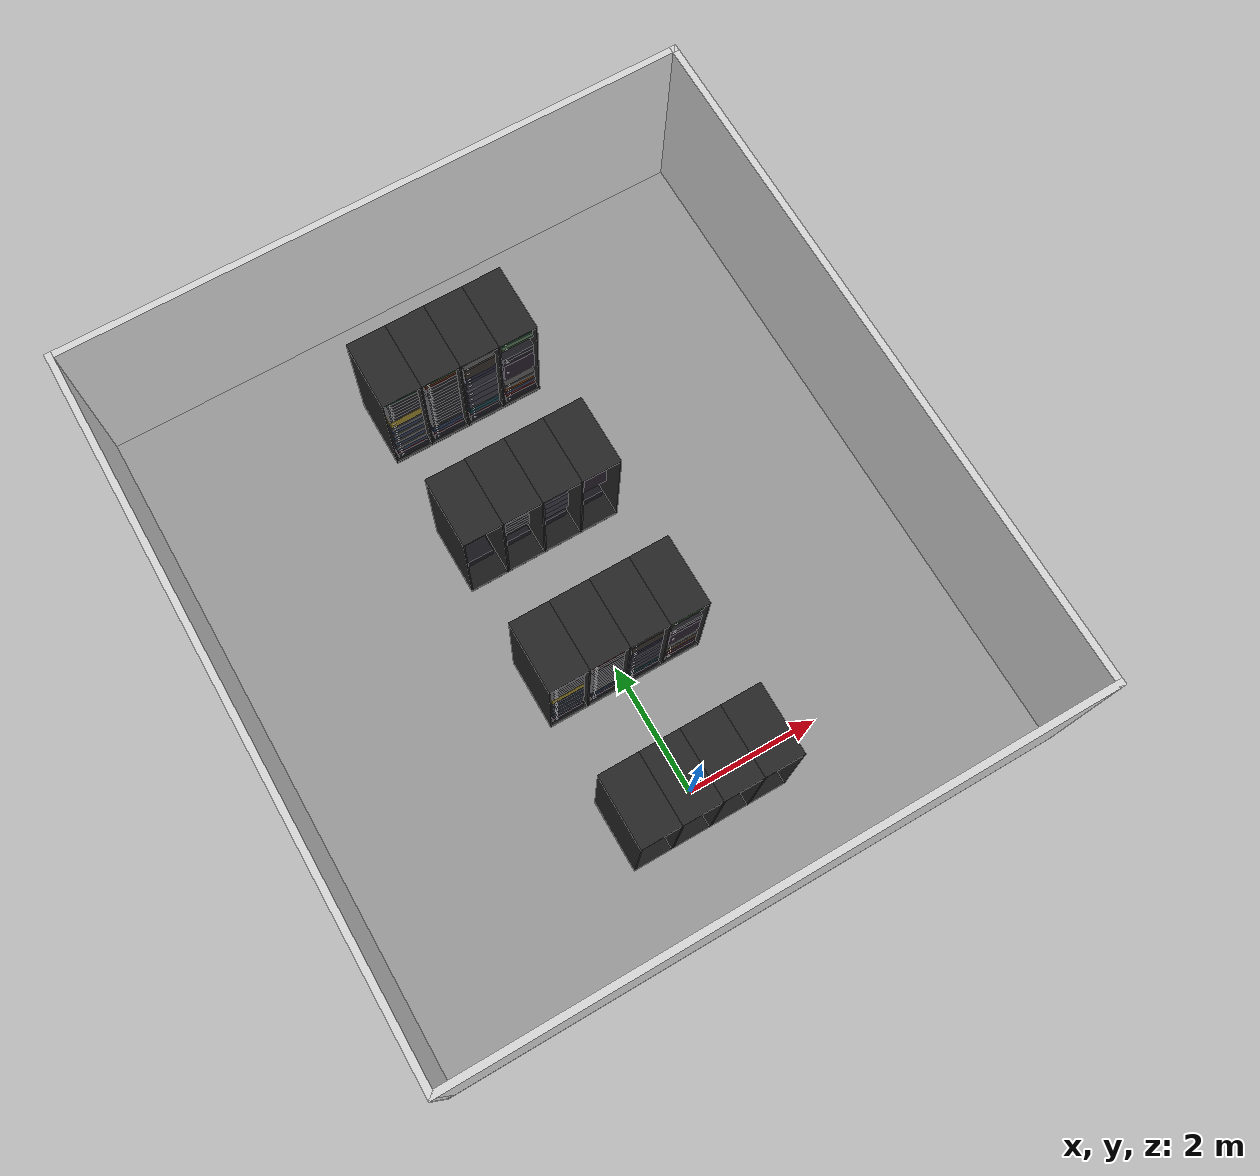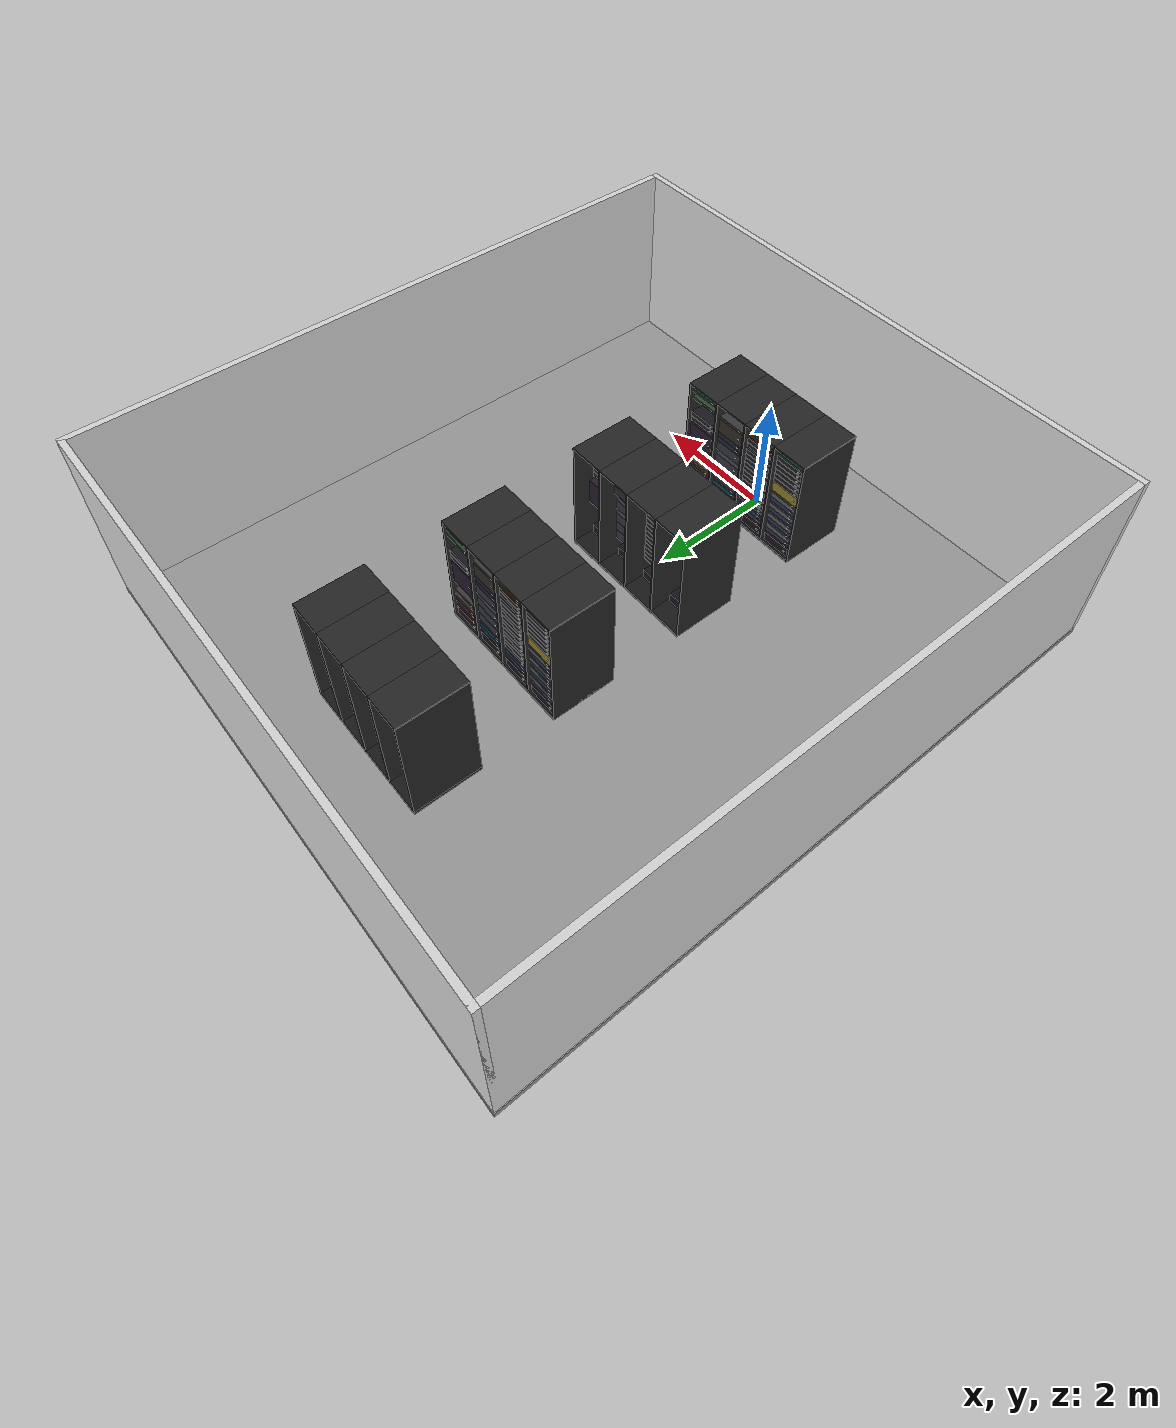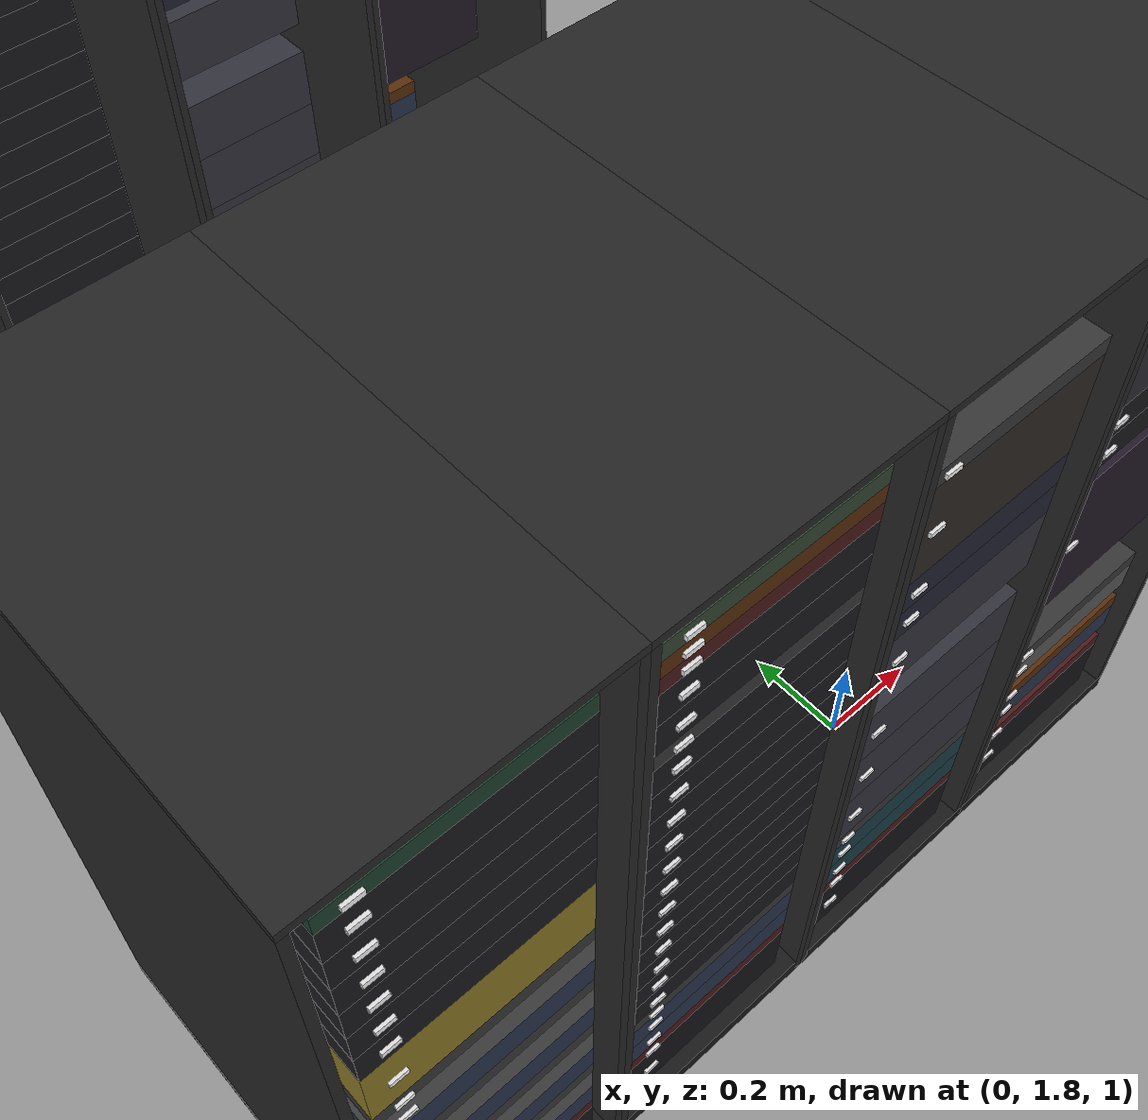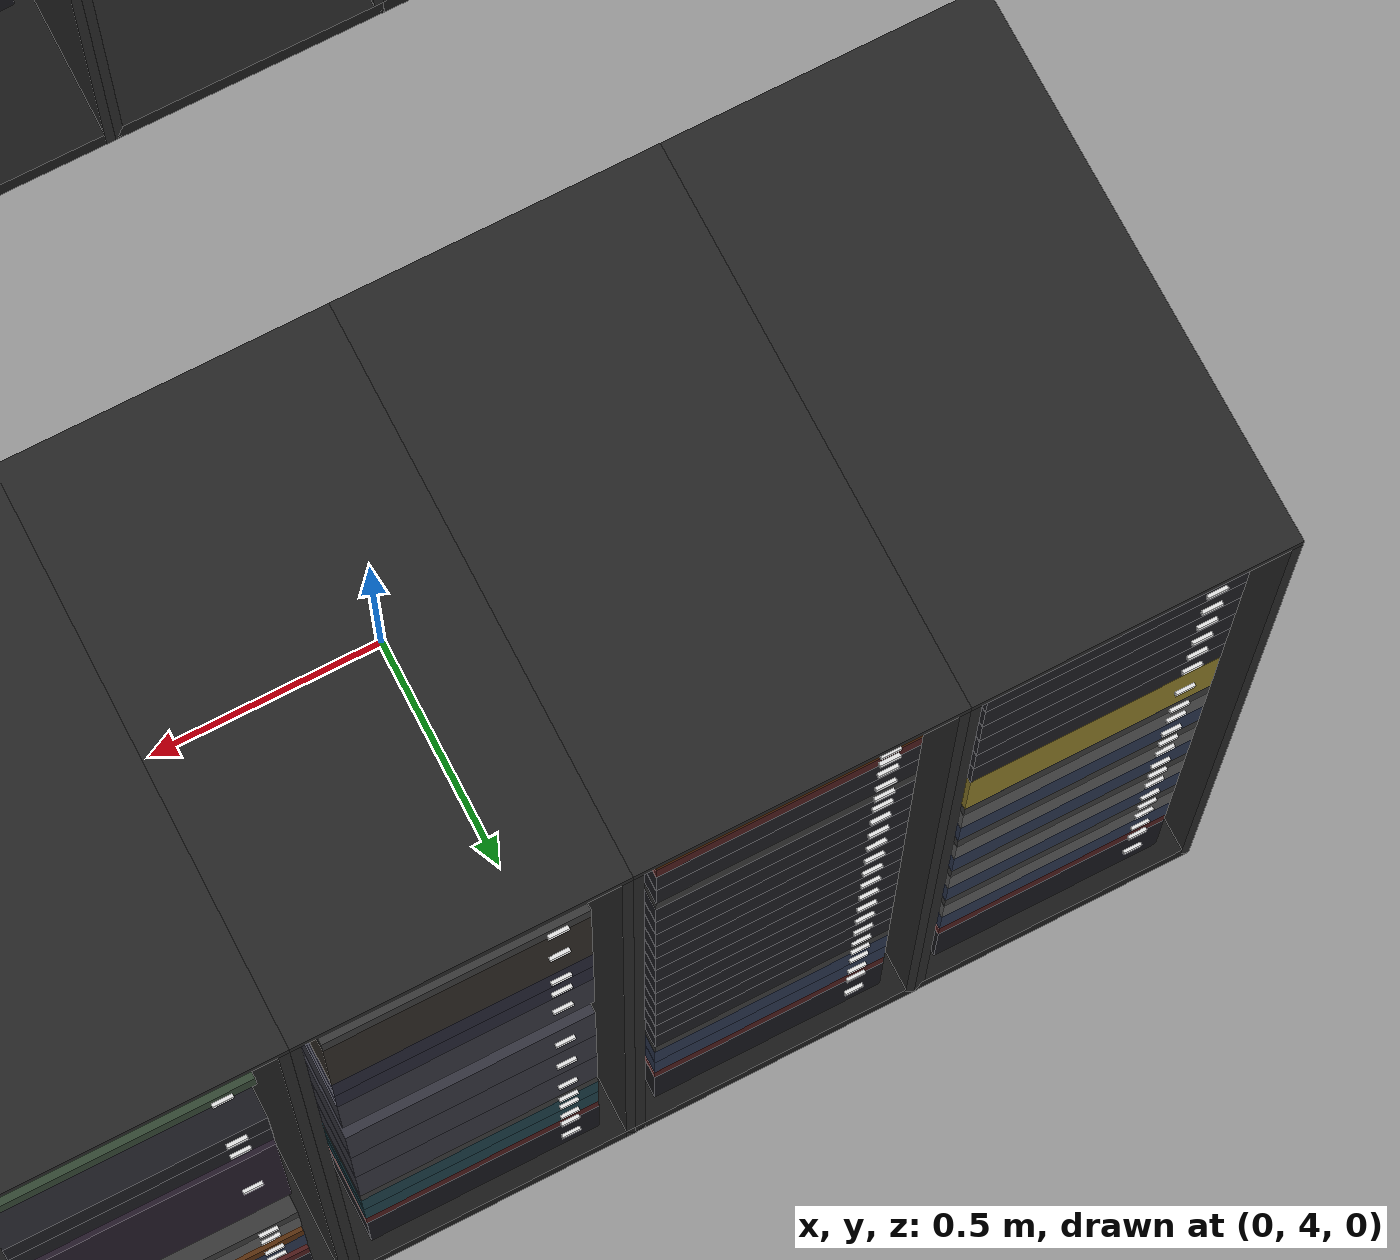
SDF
<sdf version="1.9">
 <world name="server_room">
  <plugin filename="ignition-gazebo-physics-system" name="ignition::gazebo::systems::Physics"/>
  <plugin filename="ignition-gazebo-sensors-system" name="ignition::gazebo::systems::Sensors">
   <render_engine>ogre2</render_engine>
  </plugin>
  <plugin filename="ignition-gazebo-contact-system" name="ignition::gazebo::systems::Contact"/>
  <plugin filename="ignition-gazebo-scene-broadcaster-system" name="ignition::gazebo::systems::SceneBroadcaster"/>
  <plugin filename="ignition-gazebo-user-commands-system" name="ignition::gazebo::systems::UserCommands"/>
  <physics name="1ms" type="ode">
   <max_step_size>0.001</max_step_size>
   <real_time_factor>1.0</real_time_factor>
  </physics>
  <scene>
   <ambient>0.4 0.4 0.4 1.0</ambient>
   <background>0.7 0.7 0.7 1.0</background>
   <grid>true</grid>
   <origin_visual>true</origin_visual>
  </scene>
  <atmosphere type="adiabatic">
   <temperature>288</temperature>
   <temperature_gradient>0.2</temperature_gradient>
  </atmosphere>
  <light type="directional" name="sun">
   <pose>0 0 10 0 0 0</pose>
   <diffuse>0.8 0.8 0.8 1</diffuse>
   <specular>0.2 0.2 0.2 1</specular>
   <direction>-0.5 0.1 -0.9</direction>
  </light>
  <model name="room_floor">
   <static>true</static>
   <pose>0 3.405 -0.1 0 0 0</pose>
   <link name="link">
    <collision name="collision"><geometry><box><size>9.51 10.48 0.1</size></box></geometry></collision>
    <visual name="visual">
     <geometry><box><size>9.51 10.48 0.1</size></box></geometry>
     <material><ambient>0.6 0.6 0.6 1</ambient><diffuse>0.6 0.6 0.6 1</diffuse></material>
    </visual>
   </link>
  </model>
  <model name="room_wall_front">
   <static>true</static>
   <pose>0 -1.785 1.5 0 0 0</pose>
   <link name="link">
    <collision name="collision"><geometry><box><size>9.51 0.1 3</size></box></geometry></collision>
    <visual name="visual">
     <geometry><box><size>9.51 0.1 3</size></box></geometry>
     <material><ambient>0.85 0.85 0.85 1</ambient><diffuse>0.85 0.85 0.85 1</diffuse></material>
    </visual>
   </link>
  </model>
  <model name="room_wall_back">
   <static>true</static>
   <pose>0 8.595 1.5 0 0 0</pose>
   <link name="link">
    <collision name="collision"><geometry><box><size>9.51 0.1 3</size></box></geometry></collision>
    <visual name="visual">
     <geometry><box><size>9.51 0.1 3</size></box></geometry>
     <material><ambient>0.85 0.85 0.85 1</ambient><diffuse>0.85 0.85 0.85 1</diffuse></material>
    </visual>
   </link>
  </model>
  <model name="room_wall_left">
   <static>true</static>
   <pose>-4.705 3.405 1.5 0 0 0</pose>
   <link name="link">
    <collision name="collision"><geometry><box><size>0.1 10.48 3</size></box></geometry></collision>
    <visual name="visual">
     <geometry><box><size>0.1 10.48 3</size></box></geometry>
     <material><ambient>0.85 0.85 0.85 1</ambient><diffuse>0.85 0.85 0.85 1</diffuse></material>
    </visual>
   </link>
  </model>
  <model name="room_wall_right">
   <static>true</static>
   <pose>4.705 3.405 1.5 0 0 0</pose>
   <link name="link">
    <collision name="collision"><geometry><box><size>0.1 10.48 3</size></box></geometry></collision>
    <visual name="visual">
     <geometry><box><size>0.1 10.48 3</size></box></geometry>
     <material><ambient>0.85 0.85 0.85 1</ambient><diffuse>0.85 0.85 0.85 1</diffuse></material>
    </visual>
   </link>
  </model>
  <include>
   <name>rack_r0_c0</name>
   <uri>model://server_rack_1</uri>
   <pose>-0.90 0 -0.05 0 0 3.14159265</pose>
  </include>
  <include>
   <name>rack_r0_c1</name>
   <uri>model://server_rack_2</uri>
   <pose>-0.30 0 -0.05 0 0 3.14159265</pose>
  </include>
  <include>
   <name>rack_r0_c2</name>
   <uri>model://server_rack_3</uri>
   <pose>0.30 0 -0.05 0 0 3.14159265</pose>
  </include>
  <include>
   <name>rack_r0_c3</name>
   <uri>model://server_rack_4</uri>
   <pose>0.90 0 -0.05 0 0 3.14159265</pose>
  </include>
  <include><name>rack_r1_c0</name><uri>model://server_rack_5</uri><pose>-0.90 2.27 -0.05 0 0 0</pose></include>
  <include><name>rack_r1_c1</name><uri>model://server_rack_6</uri><pose>-0.30 2.27 -0.05 0 0 0</pose></include>
  <include><name>rack_r1_c2</name><uri>model://server_rack_7</uri><pose>0.30 2.27 -0.05 0 0 0</pose></include>
  <include><name>rack_r1_c3</name><uri>model://server_rack_8</uri><pose>0.90 2.27 -0.05 0 0 0</pose></include>
  <include>
   <name>rack_r2_c0</name>
   <uri>model://server_rack_1</uri>
   <pose>-0.90 4.54 -0.05 0 0 3.14159265</pose>
  </include>
  <include>
   <name>rack_r2_c1</name>
   <uri>model://server_rack_2</uri>
   <pose>-0.30 4.54 -0.05 0 0 3.14159265</pose>
  </include>
  <include>
   <name>rack_r2_c2</name>
   <uri>model://server_rack_3</uri>
   <pose>0.30 4.54 -0.05 0 0 3.14159265</pose>
  </include>
  <include>
   <name>rack_r2_c3</name>
   <uri>model://server_rack_4</uri>
   <pose>0.90 4.54 -0.05 0 0 3.14159265</pose>
  </include>
  <include><name>rack_r3_c0</name><uri>model://server_rack_5</uri><pose>-0.90 6.81 -0.05 0 0 0</pose></include>
  <include><name>rack_r3_c1</name><uri>model://server_rack_6</uri><pose>-0.30 6.81 -0.05 0 0 0</pose></include>
  <include><name>rack_r3_c2</name><uri>model://server_rack_7</uri><pose>0.30 6.81 -0.05 0 0 0</pose></include>
  <include><name>rack_r3_c3</name><uri>model://server_rack_8</uri><pose>0.90 6.81 -0.05 0 0 0</pose></include>
 </world>
</sdf>

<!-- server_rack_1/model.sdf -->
<sdf version="1.9">
  <model name="server_rack_1">
    <static>true</static>

    <!-- ===================== FRAME ===================== -->

    <link name="frame_side_left">
      <pose>-0.29 0 1.0 0 0 0</pose>
      <collision name="collision">
        <geometry><box><size>0.02 1.07 2.0</size></box></geometry>
      </collision>
      <visual name="visual">
        <geometry><box><size>0.02 1.07 2.0</size></box></geometry>
        <material>
          <ambient>0.15 0.15 0.15 1</ambient>
          <diffuse>0.15 0.15 0.15 1</diffuse>
        </material>
      </visual>
    </link>

    <link name="frame_side_right">
      <pose>0.29 0 1.0 0 0 0</pose>
      <collision name="collision">
        <geometry><box><size>0.02 1.07 2.0</size></box></geometry>
      </collision>
      <visual name="visual">
        <geometry><box><size>0.02 1.07 2.0</size></box></geometry>
        <material>
          <ambient>0.15 0.15 0.15 1</ambient>
          <diffuse>0.15 0.15 0.15 1</diffuse>
        </material>
      </visual>
    </link>

    <link name="frame_top">
      <pose>0 0 2.01 0 0 0</pose>
      <collision name="collision">
        <geometry><box><size>0.60 1.07 0.02</size></box></geometry>
      </collision>
      <visual name="visual">
        <geometry><box><size>0.60 1.07 0.02</size></box></geometry>
        <material>
          <ambient>0.15 0.15 0.15 1</ambient>
          <diffuse>0.15 0.15 0.15 1</diffuse>
        </material>
      </visual>
    </link>

    <link name="frame_plinth">
      <pose>0 0 0.025 0 0 0</pose>
      <collision name="collision">
        <geometry><box><size>0.60 1.07 0.05</size></box></geometry>
      </collision>
      <visual name="visual">
        <geometry><box><size>0.60 1.07 0.05</size></box></geometry>
        <material>
          <ambient>0.10 0.10 0.10 1</ambient>
          <diffuse>0.10 0.10 0.10 1</diffuse>
        </material>
      </visual>
    </link>

    <!-- ===================== EQUIPMENT ===================== -->

    <!-- 4RU UPS, U1-U4 -->
    <link name="ups">
      <pose>0 -0.15 0.1389 0 0 0</pose>
      <collision name="collision">
        <geometry><box><size>0.483 0.70 0.1778</size></box></geometry>
      </collision>
      <visual name="visual">
        <geometry><box><size>0.483 0.70 0.1778</size></box></geometry>
        <material>
          <ambient>0.08 0.08 0.10 1</ambient>
          <diffuse>0.08 0.08 0.10 1</diffuse>
        </material>
      </visual>
    </link>

    <!-- 1RU PDU, U5 -->
    <link name="pdu">
      <pose>0 -0.29 0.2500 0 0 0</pose>
      <collision name="collision">
        <geometry><box><size>0.483 0.42 0.0444</size></box></geometry>
      </collision>
      <visual name="visual">
        <geometry><box><size>0.483 0.42 0.0444</size></box></geometry>
        <material>
          <ambient>0.30 0.10 0.10 1</ambient>
          <diffuse>0.30 0.10 0.10 1</diffuse>
        </material>
      </visual>
    </link>

    <!-- 2RU network switch 1, U6-U7 -->
    <link name="switch_1">
      <pose>0 -0.29 0.3167 0 0 0</pose>
      <collision name="collision">
        <geometry><box><size>0.483 0.42 0.0889</size></box></geometry>
      </collision>
      <visual name="visual">
        <geometry><box><size>0.483 0.42 0.0889</size></box></geometry>
        <material>
          <ambient>0.16 0.20 0.30 1</ambient>
          <diffuse>0.16 0.20 0.30 1</diffuse>
        </material>
      </visual>
    </link>

    <!-- 2RU patch panel 1, U8-U9 -->
    <link name="patch_panel_1">
      <pose>0 -0.425 0.4056 0 0 0</pose>
      <collision name="collision">
        <geometry><box><size>0.483 0.15 0.0889</size></box></geometry>
      </collision>
      <visual name="visual">
        <geometry><box><size>0.483 0.15 0.0889</size></box></geometry>
        <material>
          <ambient>0.35 0.35 0.35 1</ambient>
          <diffuse>0.35 0.35 0.35 1</diffuse>
        </material>
      </visual>
    </link>

    <!-- 1RU cable manager 1, U10 -->
    <link name="cable_manager_1">
      <pose>0 -0.425 0.4723 0 0 0</pose>
      <collision name="collision">
        <geometry><box><size>0.483 0.15 0.0444</size></box></geometry>
      </collision>
      <visual name="visual">
        <geometry><box><size>0.483 0.15 0.0444</size></box></geometry>
        <material>
          <ambient>0.22 0.22 0.22 1</ambient>
          <diffuse>0.22 0.22 0.22 1</diffuse>
        </material>
      </visual>
    </link>

    <!-- 2RU network switch 2, U11-U12 -->
    <link name="switch_2">
      <pose>0 -0.29 0.5390 0 0 0</pose>
      <collision name="collision">
        <geometry><box><size>0.483 0.42 0.0889</size></box></geometry>
      </collision>
      <visual name="visual">
        <geometry><box><size>0.483 0.42 0.0889</size></box></geometry>
        <material>
          <ambient>0.16 0.20 0.30 1</ambient>
          <diffuse>0.16 0.20 0.30 1</diffuse>
        </material>
      </visual>
    </link>

    <!-- 2RU patch panel 2, U13-U14 -->
    <link name="patch_panel_2">
      <pose>0 -0.425 0.6279 0 0 0</pose>
      <collision name="collision">
        <geometry><box><size>0.483 0.15 0.0889</size></box></geometry>
      </collision>
      <visual name="visual">
        <geometry><box><size>0.483 0.15 0.0889</size></box></geometry>
        <material>
          <ambient>0.35 0.35 0.35 1</ambient>
          <diffuse>0.35 0.35 0.35 1</diffuse>
        </material>
      </visual>
    </link>

    <!-- 1RU cable manager 2, U15 -->
    <link name="cable_manager_2">
      <pose>0 -0.425 0.6945 0 0 0</pose>
      <collision name="collision">
        <geometry><box><size>0.483 0.15 0.0444</size></box></geometry>
      </collision>
      <visual name="visual">
        <geometry><box><size>0.483 0.15 0.0444</size></box></geometry>
        <material>
          <ambient>0.22 0.22 0.22 1</ambient>
          <diffuse>0.22 0.22 0.22 1</diffuse>
        </material>
      </visual>
    </link>

    <!-- 2RU network switch 3, U16-U17 -->
    <link name="switch_3">
      <pose>0 -0.29 0.7612 0 0 0</pose>
      <collision name="collision">
        <geometry><box><size>0.483 0.42 0.0889</size></box></geometry>
      </collision>
      <visual name="visual">
        <geometry><box><size>0.483 0.42 0.0889</size></box></geometry>
        <material>
          <ambient>0.16 0.20 0.30 1</ambient>
          <diffuse>0.16 0.20 0.30 1</diffuse>
        </material>
      </visual>
    </link>

    <!-- 2RU patch panel 3, U18-U19 -->
    <link name="patch_panel_3">
      <pose>0 -0.425 0.8501 0 0 0</pose>
      <collision name="collision">
        <geometry><box><size>0.483 0.15 0.0889</size></box></geometry>
      </collision>
      <visual name="visual">
        <geometry><box><size>0.483 0.15 0.0889</size></box></geometry>
        <material>
          <ambient>0.35 0.35 0.35 1</ambient>
          <diffuse>0.35 0.35 0.35 1</diffuse>
        </material>
      </visual>
    </link>

    <!-- 1RU cable manager 3, U20 -->
    <link name="cable_manager_3">
      <pose>0 -0.425 0.9168 0 0 0</pose>
      <collision name="collision">
        <geometry><box><size>0.483 0.15 0.0444</size></box></geometry>
      </collision>
      <visual name="visual">
        <geometry><box><size>0.483 0.15 0.0444</size></box></geometry>
        <material>
          <ambient>0.22 0.22 0.22 1</ambient>
          <diffuse>0.22 0.22 0.22 1</diffuse>
        </material>
      </visual>
    </link>

    <!-- 2RU network switch 4, U21-U22 -->
    <link name="switch_4">
      <pose>0 -0.29 0.9835 0 0 0</pose>
      <collision name="collision">
        <geometry><box><size>0.483 0.42 0.0889</size></box></geometry>
      </collision>
      <visual name="visual">
        <geometry><box><size>0.483 0.42 0.0889</size></box></geometry>
        <material>
          <ambient>0.16 0.20 0.30 1</ambient>
          <diffuse>0.16 0.20 0.30 1</diffuse>
        </material>
      </visual>
    </link>

    <!-- 2RU patch panel 4, U23-U24 -->
    <link name="patch_panel_4">
      <pose>0 -0.425 1.0724 0 0 0</pose>
      <collision name="collision">
        <geometry><box><size>0.483 0.15 0.0889</size></box></geometry>
      </collision>
      <visual name="visual">
        <geometry><box><size>0.483 0.15 0.0889</size></box></geometry>
        <material>
          <ambient>0.35 0.35 0.35 1</ambient>
          <diffuse>0.35 0.35 0.35 1</diffuse>
        </material>
      </visual>
    </link>

    <!-- 1RU cable manager 4, U25 -->
    <link name="cable_manager_4">
      <pose>0 -0.425 1.1390 0 0 0</pose>
      <collision name="collision">
        <geometry><box><size>0.483 0.15 0.0444</size></box></geometry>
      </collision>
      <visual name="visual">
        <geometry><box><size>0.483 0.15 0.0444</size></box></geometry>
        <material>
          <ambient>0.22 0.22 0.22 1</ambient>
          <diffuse>0.22 0.22 0.22 1</diffuse>
        </material>
      </visual>
    </link>

    <!-- 4RU fiber patch panel, U26-U29 -->
    <link name="fiber_patch_panel">
      <pose>0 -0.35 1.2502 0 0 0</pose>
      <collision name="collision">
        <geometry><box><size>0.483 0.30 0.1778</size></box></geometry>
      </collision>
      <visual name="visual">
        <geometry><box><size>0.483 0.30 0.1778</size></box></geometry>
        <material>
          <ambient>0.55 0.48 0.15 1</ambient>
          <diffuse>0.55 0.48 0.15 1</diffuse>
        </material>
      </visual>
    </link>

    <!-- 2RU server 1, U30-U31 -->
    <link name="server_1">
      <pose>0 -0.15 1.3835 0 0 0</pose>
      <collision name="collision">
        <geometry><box><size>0.483 0.70 0.0889</size></box></geometry>
      </collision>
      <visual name="visual">
        <geometry><box><size>0.483 0.70 0.0889</size></box></geometry>
        <material>
          <ambient>0.10 0.10 0.12 1</ambient>
          <diffuse>0.10 0.10 0.12 1</diffuse>
        </material>
      </visual>
    </link>

    <!-- 2RU server 2, U32-U33 -->
    <link name="server_2">
      <pose>0 -0.15 1.4724 0 0 0</pose>
      <collision name="collision">
        <geometry><box><size>0.483 0.70 0.0889</size></box></geometry>
      </collision>
      <visual name="visual">
        <geometry><box><size>0.483 0.70 0.0889</size></box></geometry>
        <material>
          <ambient>0.10 0.10 0.12 1</ambient>
          <diffuse>0.10 0.10 0.12 1</diffuse>
        </material>
      </visual>
    </link>

    <!-- 2RU server 3, U34-U35 -->
    <link name="server_3">
      <pose>0 -0.15 1.5613 0 0 0</pose>
      <collision name="collision">
        <geometry><box><size>0.483 0.70 0.0889</size></box></geometry>
      </collision>
      <visual name="visual">
        <geometry><box><size>0.483 0.70 0.0889</size></box></geometry>
        <material>
          <ambient>0.10 0.10 0.12 1</ambient>
          <diffuse>0.10 0.10 0.12 1</diffuse>
        </material>
      </visual>
    </link>

    <!-- 2RU server 4, U36-U37 -->
    <link name="server_4">
      <pose>0 -0.15 1.6502 0 0 0</pose>
      <collision name="collision">
        <geometry><box><size>0.483 0.70 0.0889</size></box></geometry>
      </collision>
      <visual name="visual">
        <geometry><box><size>0.483 0.70 0.0889</size></box></geometry>
        <material>
          <ambient>0.10 0.10 0.12 1</ambient>
          <diffuse>0.10 0.10 0.12 1</diffuse>
        </material>
      </visual>
    </link>

    <!-- 2RU server 5, U38-U39 -->
    <link name="server_5">
      <pose>0 -0.15 1.7391 0 0 0</pose>
      <collision name="collision">
        <geometry><box><size>0.483 0.70 0.0889</size></box></geometry>
      </collision>
      <visual name="visual">
        <geometry><box><size>0.483 0.70 0.0889</size></box></geometry>
        <material>
          <ambient>0.10 0.10 0.12 1</ambient>
          <diffuse>0.10 0.10 0.12 1</diffuse>
        </material>
      </visual>
    </link>

    <!-- 2RU server 6, U40-U41 -->
    <link name="server_6">
      <pose>0 -0.15 1.8280 0 0 0</pose>
      <collision name="collision">
        <geometry><box><size>0.483 0.70 0.0889</size></box></geometry>
      </collision>
      <visual name="visual">
        <geometry><box><size>0.483 0.70 0.0889</size></box></geometry>
        <material>
          <ambient>0.10 0.10 0.12 1</ambient>
          <diffuse>0.10 0.10 0.12 1</diffuse>
        </material>
      </visual>
    </link>

    <!-- 1RU KVM console, U42 -->
    <link name="kvm">
      <pose>0 -0.29 1.8947 0 0 0</pose>
      <collision name="collision">
        <geometry><box><size>0.483 0.42 0.0444</size></box></geometry>
      </collision>
      <visual name="visual">
        <geometry><box><size>0.483 0.42 0.0444</size></box></geometry>
        <material>
          <ambient>0.12 0.25 0.18 1</ambient>
          <diffuse>0.12 0.25 0.18 1</diffuse>
        </material>
      </visual>
    </link>

    <!-- ===================== RFID TAGS =====================
         Local y = -0.503: 3 mm proud of the rack front plane (y = -0.50).
         Local z equals the tagged equipment's local z. -->

    <!-- ups, U1-4 -->
    <model name="barcode_label_031FB00">
      <static>true</static>
      <pose>0.18 -0.5042 0.1389 0 0 0</pose>
      <link name="label_link">
        <visual name="substrate">
          <geometry><box><size>0.03810 0.00635 0.01270</size></box></geometry>
          <material>
            <ambient>0.9 0.9 0.9 1</ambient>
            <diffuse>0.9 0.9 0.9 1</diffuse>
          </material>
        </visual>
        <visual name="print">
          <pose>0 -0.00327 0 1.5708 0 0</pose>
          <geometry><box><size>0.03810 0.01270 0.0002</size></box></geometry>
          <material>
            <ambient>1 1 1 1</ambient>
            <diffuse>1 1 1 1</diffuse>
            <pbr><metal>
              <albedo_map>model://barcode_labels/materials/textures/031FB00.png</albedo_map>
              <metalness>0.0</metalness>
              <roughness>1.0</roughness>
            </metal></pbr>
          </material>
        </visual>
      </link>
    </model>

    <!-- pdu, U5-5 -->
    <model name="barcode_label_031FB01">
      <static>true</static>
      <pose>0.18 -0.5042 0.2500 0 0 0</pose>
      <link name="label_link">
        <visual name="substrate">
          <geometry><box><size>0.03810 0.00635 0.01270</size></box></geometry>
          <material>
            <ambient>0.9 0.9 0.9 1</ambient>
            <diffuse>0.9 0.9 0.9 1</diffuse>
          </material>
        </visual>
        <visual name="print">
          <pose>0 -0.00327 0 1.5708 0 0</pose>
          <geometry><box><size>0.03810 0.01270 0.0002</size></box></geometry>
          <material>
            <ambient>1 1 1 1</ambient>
            <diffuse>1 1 1 1</diffuse>
            <pbr><metal>
              <albedo_map>model://barcode_labels/materials/textures/031FB01.png</albedo_map>
              <metalness>0.0</metalness>
              <roughness>1.0</roughness>
            </metal></pbr>
          </material>
        </visual>
      </link>
    </model>

    <!-- switch, U6-7 -->
    <model name="barcode_label_031FB02">
      <static>true</static>
      <pose>0.18 -0.5042 0.3167 0 0 0</pose>
      <link name="label_link">
        <visual name="substrate">
          <geometry><box><size>0.03810 0.00635 0.01270</size></box></geometry>
          <material>
            <ambient>0.9 0.9 0.9 1</ambient>
            <diffuse>0.9 0.9 0.9 1</diffuse>
          </material>
        </visual>
        <visual name="print">
          <pose>0 -0.00327 0 1.5708 0 0</pose>
          <geometry><box><size>0.03810 0.01270 0.0002</size></box></geometry>
          <material>
            <ambient>1 1 1 1</ambient>
            <diffuse>1 1 1 1</diffuse>
            <pbr><metal>
              <albedo_map>model://barcode_labels/materials/textures/031FB02.png</albedo_map>
              <metalness>0.0</metalness>
              <roughness>1.0</roughness>
            </metal></pbr>
          </material>
        </visual>
      </link>
    </model>

    <!-- patch_panel, U8-9 -->
    <model name="barcode_label_031FB03">
      <static>true</static>
      <pose>0.18 -0.5042 0.4056 0 0 0</pose>
      <link name="label_link">
        <visual name="substrate">
          <geometry><box><size>0.03810 0.00635 0.01270</size></box></geometry>
          <material>
            <ambient>0.9 0.9 0.9 1</ambient>
            <diffuse>0.9 0.9 0.9 1</diffuse>
          </material>
        </visual>
        <visual name="print">
          <pose>0 -0.00327 0 1.5708 0 0</pose>
          <geometry><box><size>0.03810 0.01270 0.0002</size></box></geometry>
          <material>
            <ambient>1 1 1 1</ambient>
            <diffuse>1 1 1 1</diffuse>
            <pbr><metal>
              <albedo_map>model://barcode_labels/materials/textures/031FB03.png</albedo_map>
              <metalness>0.0</metalness>
              <roughness>1.0</roughness>
            </metal></pbr>
          </material>
        </visual>
      </link>
    </model>

    <!-- cable_manager, U10-10 -->
    <model name="barcode_label_031FB04">
      <static>true</static>
      <pose>0.18 -0.5042 0.4723 0 0 0</pose>
      <link name="label_link">
        <visual name="substrate">
          <geometry><box><size>0.03810 0.00635 0.01270</size></box></geometry>
          <material>
            <ambient>0.9 0.9 0.9 1</ambient>
            <diffuse>0.9 0.9 0.9 1</diffuse>
          </material>
        </visual>
        <visual name="print">
          <pose>0 -0.00327 0 1.5708 0 0</pose>
          <geometry><box><size>0.03810 0.01270 0.0002</size></box></geometry>
          <material>
            <ambient>1 1 1 1</ambient>
            <diffuse>1 1 1 1</diffuse>
            <pbr><metal>
              <albedo_map>model://barcode_labels/materials/textures/031FB04.png</albedo_map>
              <metalness>0.0</metalness>
              <roughness>1.0</roughness>
            </metal></pbr>
          </material>
        </visual>
      </link>
    </model>

    <!-- switch, U11-12 -->
    <model name="barcode_label_031FB05">
      <static>true</static>
      <pose>0.18 -0.5042 0.5390 0 0 0</pose>
      <link name="label_link">
        <visual name="substrate">
          <geometry><box><size>0.03810 0.00635 0.01270</size></box></geometry>
          <material>
            <ambient>0.9 0.9 0.9 1</ambient>
            <diffuse>0.9 0.9 0.9 1</diffuse>
          </material>
        </visual>
        <visual name="print">
          <pose>0 -0.00327 0 1.5708 0 0</pose>
          <geometry><box><size>0.03810 0.01270 0.0002</size></box></geometry>
          <material>
            <ambient>1 1 1 1</ambient>
            <diffuse>1 1 1 1</diffuse>
            <pbr><metal>
              <albedo_map>model://barcode_labels/materials/textures/031FB05.png</albedo_map>
              <metalness>0.0</metalness>
              <roughness>1.0</roughness>
            </metal></pbr>
          </material>
        </visual>
      </link>
    </model>

    <!-- patch_panel, U13-14 -->
    <model name="barcode_label_031FB06">
      <static>true</static>
      <pose>0.18 -0.5042 0.6279 0 0 0</pose>
      <link name="label_link">
        <visual name="substrate">
          <geometry><box><size>0.03810 0.00635 0.01270</size></box></geometry>
          <material>
            <ambient>0.9 0.9 0.9 1</ambient>
            <diffuse>0.9 0.9 0.9 1</diffuse>
          </material>
        </visual>
        <visual name="print">
          <pose>0 -0.00327 0 1.5708 0 0</pose>
          <geometry><box><size>0.03810 0.01270 0.0002</size></box></geometry>
          <material>
            <ambient>1 1 1 1</ambient>
            <diffuse>1 1 1 1</diffuse>
            <pbr><metal>
              <albedo_map>model://barcode_labels/materials/textures/031FB06.png</albedo_map>
              <metalness>0.0</metalness>
              <roughness>1.0</roughness>
            </metal></pbr>
          </material>
        </visual>
      </link>
    </model>

    <!-- cable_manager, U15-15 -->
    <model name="barcode_label_031FB07">
      <static>true</static>
      <pose>0.18 -0.5042 0.6945 0 0 0</pose>
      <link name="label_link">
        <visual name="substrate">
          <geometry><box><size>0.03810 0.00635 0.01270</size></box></geometry>
          <material>
            <ambient>0.9 0.9 0.9 1</ambient>
            <diffuse>0.9 0.9 0.9 1</diffuse>
          </material>
        </visual>
        <visual name="print">
          <pose>0 -0.00327 0 1.5708 0 0</pose>
          <geometry><box><size>0.03810 0.01270 0.0002</size></box></geometry>
          <material>
            <ambient>1 1 1 1</ambient>
            <diffuse>1 1 1 1</diffuse>
            <pbr><metal>
              <albedo_map>model://barcode_labels/materials/textures/031FB07.png</albedo_map>
              <metalness>0.0</metalness>
              <roughness>1.0</roughness>
            </metal></pbr>
          </material>
        </visual>
      </link>
    </model>

    <!-- switch, U16-17 -->
    <model name="barcode_label_031FB08">
      <static>true</static>
      <pose>0.18 -0.5042 0.7612 0 0 0</pose>
      <link name="label_link">
        <visual name="substrate">
          <geometry><box><size>0.03810 0.00635 0.01270</size></box></geometry>
          <material>
            <ambient>0.9 0.9 0.9 1</ambient>
            <diffuse>0.9 0.9 0.9 1</diffuse>
          </material>
        </visual>
        <visual name="print">
          <pose>0 -0.00327 0 1.5708 0 0</pose>
          <geometry><box><size>0.03810 0.01270 0.0002</size></box></geometry>
          <material>
            <ambient>1 1 1 1</ambient>
            <diffuse>1 1 1 1</diffuse>
            <pbr><metal>
              <albedo_map>model://barcode_labels/materials/textures/031FB08.png</albedo_map>
              <metalness>0.0</metalness>
              <roughness>1.0</roughness>
            </metal></pbr>
          </material>
        </visual>
      </link>
    </model>

    <!-- patch_panel, U18-19 -->
    <model name="barcode_label_031FB09">
      <static>true</static>
      <pose>0.18 -0.5042 0.8501 0 0 0</pose>
      <link name="label_link">
        <visual name="substrate">
          <geometry><box><size>0.03810 0.00635 0.01270</size></box></geometry>
          <material>
            <ambient>0.9 0.9 0.9 1</ambient>
            <diffuse>0.9 0.9 0.9 1</diffuse>
          </material>
        </visual>
        <visual name="print">
          <pose>0 -0.00327 0 1.5708 0 0</pose>
          <geometry><box><size>0.03810 0.01270 0.0002</size></box></geometry>
          <material>
            <ambient>1 1 1 1</ambient>
            <diffuse>1 1 1 1</diffuse>
            <pbr><metal>
              <albedo_map>model://barcode_labels/materials/textures/031FB09.png</albedo_map>
              <metalness>0.0</metalness>
              <roughness>1.0</roughness>
            </metal></pbr>
          </material>
        </visual>
      </link>
    </model>

    <!-- cable_manager, U20-20 -->
    <model name="barcode_label_031FB0A">
      <static>true</static>
      <pose>0.18 -0.5042 0.9168 0 0 0</pose>
      <link name="label_link">
        <visual name="substrate">
          <geometry><box><size>0.03810 0.00635 0.01270</size></box></geometry>
          <material>
            <ambient>0.9 0.9 0.9 1</ambient>
            <diffuse>0.9 0.9 0.9 1</diffuse>
          </material>
        </visual>
        <visual name="print">
          <pose>0 -0.00327 0 1.5708 0 0</pose>
          <geometry><box><size>0.03810 0.01270 0.0002</size></box></geometry>
          <material>
            <ambient>1 1 1 1</ambient>
            <diffuse>1 1 1 1</diffuse>
            <pbr><metal>
              <albedo_map>model://barcode_labels/materials/textures/031FB0A.png</albedo_map>
              <metalness>0.0</metalness>
              <roughness>1.0</roughness>
            </metal></pbr>
          </material>
        </visual>
      </link>
    </model>

    <!-- switch, U21-22 -->
    <model name="barcode_label_031FB0B">
      <static>true</static>
      <pose>0.18 -0.5042 0.9835 0 0 0</pose>
      <link name="label_link">
        <visual name="substrate">
          <geometry><box><size>0.03810 0.00635 0.01270</size></box></geometry>
          <material>
            <ambient>0.9 0.9 0.9 1</ambient>
            <diffuse>0.9 0.9 0.9 1</diffuse>
          </material>
        </visual>
        <visual name="print">
          <pose>0 -0.00327 0 1.5708 0 0</pose>
          <geometry><box><size>0.03810 0.01270 0.0002</size></box></geometry>
          <material>
            <ambient>1 1 1 1</ambient>
            <diffuse>1 1 1 1</diffuse>
            <pbr><metal>
              <albedo_map>model://barcode_labels/materials/textures/031FB0B.png</albedo_map>
              <metalness>0.0</metalness>
              <roughness>1.0</roughness>
            </metal></pbr>
          </material>
        </visual>
      </link>
    </model>

    <!-- patch_panel, U23-24 -->
    <model name="barcode_label_031FB0C">
      <static>true</static>
      <pose>0.18 -0.5042 1.0724 0 0 0</pose>
      <link name="label_link">
        <visual name="substrate">
          <geometry><box><size>0.03810 0.00635 0.01270</size></box></geometry>
          <material>
            <ambient>0.9 0.9 0.9 1</ambient>
            <diffuse>0.9 0.9 0.9 1</diffuse>
          </material>
        </visual>
        <visual name="print">
          <pose>0 -0.00327 0 1.5708 0 0</pose>
          <geometry><box><size>0.03810 0.01270 0.0002</size></box></geometry>
          <material>
            <ambient>1 1 1 1</ambient>
            <diffuse>1 1 1 1</diffuse>
            <pbr><metal>
              <albedo_map>model://barcode_labels/materials/textures/031FB0C.png</albedo_map>
              <metalness>0.0</metalness>
              <roughness>1.0</roughness>
            </metal></pbr>
          </material>
        </visual>
      </link>
    </model>

    <!-- cable_manager, U25-25 -->
    <model name="barcode_label_031FB0D">
      <static>true</static>
      <pose>0.18 -0.5042 1.1390 0 0 0</pose>
      <link name="label_link">
        <visual name="substrate">
          <geometry><box><size>0.03810 0.00635 0.01270</size></box></geometry>
          <material>
            <ambient>0.9 0.9 0.9 1</ambient>
            <diffuse>0.9 0.9 0.9 1</diffuse>
          </material>
        </visual>
        <visual name="print">
          <pose>0 -0.00327 0 1.5708 0 0</pose>
          <geometry><box><size>0.03810 0.01270 0.0002</size></box></geometry>
          <material>
            <ambient>1 1 1 1</ambient>
            <diffuse>1 1 1 1</diffuse>
            <pbr><metal>
              <albedo_map>model://barcode_labels/materials/textures/031FB0D.png</albedo_map>
              <metalness>0.0</metalness>
              <roughness>1.0</roughness>
            </metal></pbr>
          </material>
        </visual>
      </link>
    </model>

    <!-- fiber_patch_panel, U26-29 -->
    <model name="barcode_label_031FB0E">
      <static>true</static>
      <pose>0.18 -0.5042 1.2502 0 0 0</pose>
      <link name="label_link">
        <visual name="substrate">
          <geometry><box><size>0.03810 0.00635 0.01270</size></box></geometry>
          <material>
            <ambient>0.9 0.9 0.9 1</ambient>
            <diffuse>0.9 0.9 0.9 1</diffuse>
          </material>
        </visual>
        <visual name="print">
          <pose>0 -0.00327 0 1.5708 0 0</pose>
          <geometry><box><size>0.03810 0.01270 0.0002</size></box></geometry>
          <material>
            <ambient>1 1 1 1</ambient>
            <diffuse>1 1 1 1</diffuse>
            <pbr><metal>
              <albedo_map>model://barcode_labels/materials/textures/031FB0E.png</albedo_map>
              <metalness>0.0</metalness>
              <roughness>1.0</roughness>
            </metal></pbr>
          </material>
        </visual>
      </link>
    </model>

    <!-- server, U30-31 -->
    <model name="barcode_label_031FB0F">
      <static>true</static>
      <pose>0.18 -0.5042 1.3835 0 0 0</pose>
      <link name="label_link">
        <visual name="substrate">
          <geometry><box><size>0.03810 0.00635 0.01270</size></box></geometry>
          <material>
            <ambient>0.9 0.9 0.9 1</ambient>
            <diffuse>0.9 0.9 0.9 1</diffuse>
          </material>
        </visual>
        <visual name="print">
          <pose>0 -0.00327 0 1.5708 0 0</pose>
          <geometry><box><size>0.03810 0.01270 0.0002</size></box></geometry>
          <material>
            <ambient>1 1 1 1</ambient>
            <diffuse>1 1 1 1</diffuse>
            <pbr><metal>
              <albedo_map>model://barcode_labels/materials/textures/031FB0F.png</albedo_map>
              <metalness>0.0</metalness>
              <roughness>1.0</roughness>
            </metal></pbr>
          </material>
        </visual>
      </link>
    </model>

    <!-- server, U32-33 -->
    <model name="barcode_label_031FB10">
      <static>true</static>
      <pose>0.18 -0.5042 1.4724 0 0 0</pose>
      <link name="label_link">
        <visual name="substrate">
          <geometry><box><size>0.03810 0.00635 0.01270</size></box></geometry>
          <material>
            <ambient>0.9 0.9 0.9 1</ambient>
            <diffuse>0.9 0.9 0.9 1</diffuse>
          </material>
        </visual>
        <visual name="print">
          <pose>0 -0.00327 0 1.5708 0 0</pose>
          <geometry><box><size>0.03810 0.01270 0.0002</size></box></geometry>
          <material>
            <ambient>1 1 1 1</ambient>
            <diffuse>1 1 1 1</diffuse>
            <pbr><metal>
              <albedo_map>model://barcode_labels/materials/textures/031FB10.png</albedo_map>
              <metalness>0.0</metalness>
              <roughness>1.0</roughness>
            </metal></pbr>
          </material>
        </visual>
      </link>
    </model>

    <!-- server, U34-35 -->
    <model name="barcode_label_031FB11">
      <static>true</static>
      <pose>0.18 -0.5042 1.5613 0 0 0</pose>
      <link name="label_link">
        <visual name="substrate">
          <geometry><box><size>0.03810 0.00635 0.01270</size></box></geometry>
          <material>
            <ambient>0.9 0.9 0.9 1</ambient>
            <diffuse>0.9 0.9 0.9 1</diffuse>
          </material>
        </visual>
        <visual name="print">
          <pose>0 -0.00327 0 1.5708 0 0</pose>
          <geometry><box><size>0.03810 0.01270 0.0002</size></box></geometry>
          <material>
            <ambient>1 1 1 1</ambient>
            <diffuse>1 1 1 1</diffuse>
            <pbr><metal>
              <albedo_map>model://barcode_labels/materials/textures/031FB11.png</albedo_map>
              <metalness>0.0</metalness>
              <roughness>1.0</roughness>
            </metal></pbr>
          </material>
        </visual>
      </link>
    </model>

    <!-- server, U36-37 -->
    <model name="barcode_label_031FB12">
      <static>true</static>
      <pose>0.18 -0.5042 1.6502 0 0 0</pose>
      <link name="label_link">
        <visual name="substrate">
          <geometry><box><size>0.03810 0.00635 0.01270</size></box></geometry>
          <material>
            <ambient>0.9 0.9 0.9 1</ambient>
            <diffuse>0.9 0.9 0.9 1</diffuse>
          </material>
        </visual>
        <visual name="print">
          <pose>0 -0.00327 0 1.5708 0 0</pose>
          <geometry><box><size>0.03810 0.01270 0.0002</size></box></geometry>
          <material>
            <ambient>1 1 1 1</ambient>
            <diffuse>1 1 1 1</diffuse>
            <pbr><metal>
              <albedo_map>model://barcode_labels/materials/textures/031FB12.png</albedo_map>
              <metalness>0.0</metalness>
              <roughness>1.0</roughness>
            </metal></pbr>
          </material>
        </visual>
      </link>
    </model>

    <!-- server, U38-39 -->
    <model name="barcode_label_031FB13">
      <static>true</static>
      <pose>0.18 -0.5042 1.7391 0 0 0</pose>
      <link name="label_link">
        <visual name="substrate">
          <geometry><box><size>0.03810 0.00635 0.01270</size></box></geometry>
          <material>
            <ambient>0.9 0.9 0.9 1</ambient>
            <diffuse>0.9 0.9 0.9 1</diffuse>
          </material>
        </visual>
        <visual name="print">
          <pose>0 -0.00327 0 1.5708 0 0</pose>
          <geometry><box><size>0.03810 0.01270 0.0002</size></box></geometry>
          <material>
            <ambient>1 1 1 1</ambient>
            <diffuse>1 1 1 1</diffuse>
            <pbr><metal>
              <albedo_map>model://barcode_labels/materials/textures/031FB13.png</albedo_map>
              <metalness>0.0</metalness>
              <roughness>1.0</roughness>
            </metal></pbr>
          </material>
        </visual>
      </link>
    </model>

    <!-- server, U40-41 -->
    <model name="barcode_label_031FB14">
      <static>true</static>
      <pose>0.18 -0.5042 1.8280 0 0 0</pose>
      <link name="label_link">
        <visual name="substrate">
          <geometry><box><size>0.03810 0.00635 0.01270</size></box></geometry>
          <material>
            <ambient>0.9 0.9 0.9 1</ambient>
            <diffuse>0.9 0.9 0.9 1</diffuse>
          </material>
        </visual>
        <visual name="print">
          <pose>0 -0.00327 0 1.5708 0 0</pose>
          <geometry><box><size>0.03810 0.01270 0.0002</size></box></geometry>
          <material>
            <ambient>1 1 1 1</ambient>
            <diffuse>1 1 1 1</diffuse>
            <pbr><metal>
              <albedo_map>model://barcode_labels/materials/textures/031FB14.png</albedo_map>
              <metalness>0.0</metalness>
              <roughness>1.0</roughness>
            </metal></pbr>
          </material>
        </visual>
      </link>
    </model>

    <!-- kvm, U42-42 -->
    <model name="barcode_label_031FB15">
      <static>true</static>
      <pose>0.18 -0.5042 1.8947 0 0 0</pose>
      <link name="label_link">
        <visual name="substrate">
          <geometry><box><size>0.03810 0.00635 0.01270</size></box></geometry>
          <material>
            <ambient>0.9 0.9 0.9 1</ambient>
            <diffuse>0.9 0.9 0.9 1</diffuse>
          </material>
        </visual>
        <visual name="print">
          <pose>0 -0.00327 0 1.5708 0 0</pose>
          <geometry><box><size>0.03810 0.01270 0.0002</size></box></geometry>
          <material>
            <ambient>1 1 1 1</ambient>
            <diffuse>1 1 1 1</diffuse>
            <pbr><metal>
              <albedo_map>model://barcode_labels/materials/textures/031FB15.png</albedo_map>
              <metalness>0.0</metalness>
              <roughness>1.0</roughness>
            </metal></pbr>
          </material>
        </visual>
      </link>
    </model>

  </model>
</sdf>

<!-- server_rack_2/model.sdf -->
<sdf version="1.9">
  <model name="server_rack_2">
    <static>true</static>

    <!-- ===================== FRAME ===================== -->

    <link name="frame_side_left">
      <pose>-0.29 0 1.0 0 0 0</pose>
      <collision name="collision">
        <geometry><box><size>0.02 1.07 2.0</size></box></geometry>
      </collision>
      <visual name="visual">
        <geometry><box><size>0.02 1.07 2.0</size></box></geometry>
        <material>
          <ambient>0.15 0.15 0.15 1</ambient>
          <diffuse>0.15 0.15 0.15 1</diffuse>
        </material>
      </visual>
    </link>

    <link name="frame_side_right">
      <pose>0.29 0 1.0 0 0 0</pose>
      <collision name="collision">
        <geometry><box><size>0.02 1.07 2.0</size></box></geometry>
      </collision>
      <visual name="visual">
        <geometry><box><size>0.02 1.07 2.0</size></box></geometry>
        <material>
          <ambient>0.15 0.15 0.15 1</ambient>
          <diffuse>0.15 0.15 0.15 1</diffuse>
        </material>
      </visual>
    </link>

    <link name="frame_top">
      <pose>0 0 2.01 0 0 0</pose>
      <collision name="collision">
        <geometry><box><size>0.60 1.07 0.02</size></box></geometry>
      </collision>
      <visual name="visual">
        <geometry><box><size>0.60 1.07 0.02</size></box></geometry>
        <material>
          <ambient>0.15 0.15 0.15 1</ambient>
          <diffuse>0.15 0.15 0.15 1</diffuse>
        </material>
      </visual>
    </link>

    <link name="frame_plinth">
      <pose>0 0 0.025 0 0 0</pose>
      <collision name="collision">
        <geometry><box><size>0.60 1.07 0.05</size></box></geometry>
      </collision>
      <visual name="visual">
        <geometry><box><size>0.60 1.07 0.05</size></box></geometry>
        <material>
          <ambient>0.10 0.10 0.10 1</ambient>
          <diffuse>0.10 0.10 0.10 1</diffuse>
        </material>
      </visual>
    </link>

    <!-- ===================== EQUIPMENT ===================== -->

    <!-- 4RU UPS, U1-U4 -->
    <link name="ups">
      <pose>0 -0.15 0.1389 0 0 0</pose>
      <collision name="collision">
        <geometry><box><size>0.483 0.70 0.1778</size></box></geometry>
      </collision>
      <visual name="visual">
        <geometry><box><size>0.483 0.70 0.1778</size></box></geometry>
        <material>
          <ambient>0.08 0.08 0.10 1</ambient>
          <diffuse>0.08 0.08 0.10 1</diffuse>
        </material>
      </visual>
    </link>

    <!-- 1RU PDU A feed, U5 -->
    <link name="pdu_1">
      <pose>0 -0.29 0.2500 0 0 0</pose>
      <collision name="collision">
        <geometry><box><size>0.483 0.42 0.0444</size></box></geometry>
      </collision>
      <visual name="visual">
        <geometry><box><size>0.483 0.42 0.0444</size></box></geometry>
        <material>
          <ambient>0.30 0.10 0.10 1</ambient>
          <diffuse>0.30 0.10 0.10 1</diffuse>
        </material>
      </visual>
    </link>

    <!-- 2RU ToR switch 1, U6-U7 -->
    <link name="switch_1">
      <pose>0 -0.29 0.3167 0 0 0</pose>
      <collision name="collision">
        <geometry><box><size>0.483 0.42 0.0889</size></box></geometry>
      </collision>
      <visual name="visual">
        <geometry><box><size>0.483 0.42 0.0889</size></box></geometry>
        <material>
          <ambient>0.16 0.20 0.30 1</ambient>
          <diffuse>0.16 0.20 0.30 1</diffuse>
        </material>
      </visual>
    </link>

    <!-- 2RU ToR switch 2 (redundant), U8-U9 -->
    <link name="switch_2">
      <pose>0 -0.29 0.4056 0 0 0</pose>
      <collision name="collision">
        <geometry><box><size>0.483 0.42 0.0889</size></box></geometry>
      </collision>
      <visual name="visual">
        <geometry><box><size>0.483 0.42 0.0889</size></box></geometry>
        <material>
          <ambient>0.16 0.20 0.30 1</ambient>
          <diffuse>0.16 0.20 0.30 1</diffuse>
        </material>
      </visual>
    </link>

    <!-- 1RU cable manager 1, U10 -->
    <link name="cable_manager_1">
      <pose>0 -0.425 0.4723 0 0 0</pose>
      <collision name="collision">
        <geometry><box><size>0.483 0.15 0.0444</size></box></geometry>
      </collision>
      <visual name="visual">
        <geometry><box><size>0.483 0.15 0.0444</size></box></geometry>
        <material>
          <ambient>0.22 0.22 0.22 1</ambient>
          <diffuse>0.22 0.22 0.22 1</diffuse>
        </material>
      </visual>
    </link>

    <!-- 2RU server 1, U11-U12 -->
    <link name="server_1">
      <pose>0 -0.15 0.5390 0 0 0</pose>
      <collision name="collision">
        <geometry><box><size>0.483 0.70 0.0889</size></box></geometry>
      </collision>
      <visual name="visual">
        <geometry><box><size>0.483 0.70 0.0889</size></box></geometry>
        <material>
          <ambient>0.10 0.10 0.12 1</ambient>
          <diffuse>0.10 0.10 0.12 1</diffuse>
        </material>
      </visual>
    </link>

    <!-- 2RU server 2, U13-U14 -->
    <link name="server_2">
      <pose>0 -0.15 0.6279 0 0 0</pose>
      <collision name="collision">
        <geometry><box><size>0.483 0.70 0.0889</size></box></geometry>
      </collision>
      <visual name="visual">
        <geometry><box><size>0.483 0.70 0.0889</size></box></geometry>
        <material>
          <ambient>0.10 0.10 0.12 1</ambient>
          <diffuse>0.10 0.10 0.12 1</diffuse>
        </material>
      </visual>
    </link>

    <!-- 2RU server 3, U15-U16 -->
    <link name="server_3">
      <pose>0 -0.15 0.7168 0 0 0</pose>
      <collision name="collision">
        <geometry><box><size>0.483 0.70 0.0889</size></box></geometry>
      </collision>
      <visual name="visual">
        <geometry><box><size>0.483 0.70 0.0889</size></box></geometry>
        <material>
          <ambient>0.10 0.10 0.12 1</ambient>
          <diffuse>0.10 0.10 0.12 1</diffuse>
        </material>
      </visual>
    </link>

    <!-- 2RU server 4, U17-U18 -->
    <link name="server_4">
      <pose>0 -0.15 0.8057 0 0 0</pose>
      <collision name="collision">
        <geometry><box><size>0.483 0.70 0.0889</size></box></geometry>
      </collision>
      <visual name="visual">
        <geometry><box><size>0.483 0.70 0.0889</size></box></geometry>
        <material>
          <ambient>0.10 0.10 0.12 1</ambient>
          <diffuse>0.10 0.10 0.12 1</diffuse>
        </material>
      </visual>
    </link>

    <!-- 2RU server 5, U19-U20 -->
    <link name="server_5">
      <pose>0 -0.15 0.8946 0 0 0</pose>
      <collision name="collision">
        <geometry><box><size>0.483 0.70 0.0889</size></box></geometry>
      </collision>
      <visual name="visual">
        <geometry><box><size>0.483 0.70 0.0889</size></box></geometry>
        <material>
          <ambient>0.10 0.10 0.12 1</ambient>
          <diffuse>0.10 0.10 0.12 1</diffuse>
        </material>
      </visual>
    </link>

    <!-- 2RU server 6, U21-U22 -->
    <link name="server_6">
      <pose>0 -0.15 0.9835 0 0 0</pose>
      <collision name="collision">
        <geometry><box><size>0.483 0.70 0.0889</size></box></geometry>
      </collision>
      <visual name="visual">
        <geometry><box><size>0.483 0.70 0.0889</size></box></geometry>
        <material>
          <ambient>0.10 0.10 0.12 1</ambient>
          <diffuse>0.10 0.10 0.12 1</diffuse>
        </material>
      </visual>
    </link>

    <!-- 2RU server 7, U23-U24 -->
    <link name="server_7">
      <pose>0 -0.15 1.0724 0 0 0</pose>
      <collision name="collision">
        <geometry><box><size>0.483 0.70 0.0889</size></box></geometry>
      </collision>
      <visual name="visual">
        <geometry><box><size>0.483 0.70 0.0889</size></box></geometry>
        <material>
          <ambient>0.10 0.10 0.12 1</ambient>
          <diffuse>0.10 0.10 0.12 1</diffuse>
        </material>
      </visual>
    </link>

    <!-- 2RU server 8, U25-U26 -->
    <link name="server_8">
      <pose>0 -0.15 1.1613 0 0 0</pose>
      <collision name="collision">
        <geometry><box><size>0.483 0.70 0.0889</size></box></geometry>
      </collision>
      <visual name="visual">
        <geometry><box><size>0.483 0.70 0.0889</size></box></geometry>
        <material>
          <ambient>0.10 0.10 0.12 1</ambient>
          <diffuse>0.10 0.10 0.12 1</diffuse>
        </material>
      </visual>
    </link>

    <!-- 2RU server 9, U27-U28 -->
    <link name="server_9">
      <pose>0 -0.15 1.2502 0 0 0</pose>
      <collision name="collision">
        <geometry><box><size>0.483 0.70 0.0889</size></box></geometry>
      </collision>
      <visual name="visual">
        <geometry><box><size>0.483 0.70 0.0889</size></box></geometry>
        <material>
          <ambient>0.10 0.10 0.12 1</ambient>
          <diffuse>0.10 0.10 0.12 1</diffuse>
        </material>
      </visual>
    </link>

    <!-- 2RU server 10, U29-U30 -->
    <link name="server_10">
      <pose>0 -0.15 1.3391 0 0 0</pose>
      <collision name="collision">
        <geometry><box><size>0.483 0.70 0.0889</size></box></geometry>
      </collision>
      <visual name="visual">
        <geometry><box><size>0.483 0.70 0.0889</size></box></geometry>
        <material>
          <ambient>0.10 0.10 0.12 1</ambient>
          <diffuse>0.10 0.10 0.12 1</diffuse>
        </material>
      </visual>
    </link>

    <!-- 2RU server 11, U31-U32 -->
    <link name="server_11">
      <pose>0 -0.15 1.4280 0 0 0</pose>
      <collision name="collision">
        <geometry><box><size>0.483 0.70 0.0889</size></box></geometry>
      </collision>
      <visual name="visual">
        <geometry><box><size>0.483 0.70 0.0889</size></box></geometry>
        <material>
          <ambient>0.10 0.10 0.12 1</ambient>
          <diffuse>0.10 0.10 0.12 1</diffuse>
        </material>
      </visual>
    </link>

    <!-- 2RU server 12, U33-U34 -->
    <link name="server_12">
      <pose>0 -0.15 1.5169 0 0 0</pose>
      <collision name="collision">
        <geometry><box><size>0.483 0.70 0.0889</size></box></geometry>
      </collision>
      <visual name="visual">
        <geometry><box><size>0.483 0.70 0.0889</size></box></geometry>
        <material>
          <ambient>0.10 0.10 0.12 1</ambient>
          <diffuse>0.10 0.10 0.12 1</diffuse>
        </material>
      </visual>
    </link>

    <!-- 1RU cable manager 2, U35 -->
    <link name="cable_manager_2">
      <pose>0 -0.425 1.5835 0 0 0</pose>
      <collision name="collision">
        <geometry><box><size>0.483 0.15 0.0444</size></box></geometry>
      </collision>
      <visual name="visual">
        <geometry><box><size>0.483 0.15 0.0444</size></box></geometry>
        <material>
          <ambient>0.22 0.22 0.22 1</ambient>
          <diffuse>0.22 0.22 0.22 1</diffuse>
        </material>
      </visual>
    </link>

    <!-- 2RU server 13, U36-U37 -->
    <link name="server_13">
      <pose>0 -0.15 1.6502 0 0 0</pose>
      <collision name="collision">
        <geometry><box><size>0.483 0.70 0.0889</size></box></geometry>
      </collision>
      <visual name="visual">
        <geometry><box><size>0.483 0.70 0.0889</size></box></geometry>
        <material>
          <ambient>0.10 0.10 0.12 1</ambient>
          <diffuse>0.10 0.10 0.12 1</diffuse>
        </material>
      </visual>
    </link>

    <!-- 2RU server 14, U38-U39 -->
    <link name="server_14">
      <pose>0 -0.15 1.7391 0 0 0</pose>
      <collision name="collision">
        <geometry><box><size>0.483 0.70 0.0889</size></box></geometry>
      </collision>
      <visual name="visual">
        <geometry><box><size>0.483 0.70 0.0889</size></box></geometry>
        <material>
          <ambient>0.10 0.10 0.12 1</ambient>
          <diffuse>0.10 0.10 0.12 1</diffuse>
        </material>
      </visual>
    </link>

    <!-- 1RU PDU B feed, U40 -->
    <link name="pdu_2">
      <pose>0 -0.29 1.8058 0 0 0</pose>
      <collision name="collision">
        <geometry><box><size>0.483 0.42 0.0444</size></box></geometry>
      </collision>
      <visual name="visual">
        <geometry><box><size>0.483 0.42 0.0444</size></box></geometry>
        <material>
          <ambient>0.30 0.10 0.10 1</ambient>
          <diffuse>0.30 0.10 0.10 1</diffuse>
        </material>
      </visual>
    </link>

    <!-- 1RU firewall, U41 -->
    <link name="firewall">
      <pose>0 -0.29 1.8502 0 0 0</pose>
      <collision name="collision">
        <geometry><box><size>0.483 0.42 0.0444</size></box></geometry>
      </collision>
      <visual name="visual">
        <geometry><box><size>0.483 0.42 0.0444</size></box></geometry>
        <material>
          <ambient>0.35 0.18 0.05 1</ambient>
          <diffuse>0.35 0.18 0.05 1</diffuse>
        </material>
      </visual>
    </link>

    <!-- 1RU console server, U42 -->
    <link name="console_server">
      <pose>0 -0.35 1.8947 0 0 0</pose>
      <collision name="collision">
        <geometry><box><size>0.483 0.30 0.0444</size></box></geometry>
      </collision>
      <visual name="visual">
        <geometry><box><size>0.483 0.30 0.0444</size></box></geometry>
        <material>
          <ambient>0.20 0.28 0.20 1</ambient>
          <diffuse>0.20 0.28 0.20 1</diffuse>
        </material>
      </visual>
    </link>

    <!-- ===================== RFID TAGS ===================== -->

    <!-- ups, U1-4 -->
    <model name="barcode_label_031FB16">
      <static>true</static>
      <pose>0.18 -0.5042 0.1389 0 0 0</pose>
      <link name="label_link">
        <visual name="substrate">
          <geometry><box><size>0.03810 0.00635 0.01270</size></box></geometry>
          <material>
            <ambient>0.9 0.9 0.9 1</ambient>
            <diffuse>0.9 0.9 0.9 1</diffuse>
          </material>
        </visual>
        <visual name="print">
          <pose>0 -0.00327 0 1.5708 0 0</pose>
          <geometry><box><size>0.03810 0.01270 0.0002</size></box></geometry>
          <material>
            <ambient>1 1 1 1</ambient>
            <diffuse>1 1 1 1</diffuse>
            <pbr><metal>
              <albedo_map>model://barcode_labels/materials/textures/031FB16.png</albedo_map>
              <metalness>0.0</metalness>
              <roughness>1.0</roughness>
            </metal></pbr>
          </material>
        </visual>
      </link>
    </model>

    <!-- pdu, U5-5 -->
    <model name="barcode_label_031FB17">
      <static>true</static>
      <pose>0.18 -0.5042 0.2500 0 0 0</pose>
      <link name="label_link">
        <visual name="substrate">
          <geometry><box><size>0.03810 0.00635 0.01270</size></box></geometry>
          <material>
            <ambient>0.9 0.9 0.9 1</ambient>
            <diffuse>0.9 0.9 0.9 1</diffuse>
          </material>
        </visual>
        <visual name="print">
          <pose>0 -0.00327 0 1.5708 0 0</pose>
          <geometry><box><size>0.03810 0.01270 0.0002</size></box></geometry>
          <material>
            <ambient>1 1 1 1</ambient>
            <diffuse>1 1 1 1</diffuse>
            <pbr><metal>
              <albedo_map>model://barcode_labels/materials/textures/031FB17.png</albedo_map>
              <metalness>0.0</metalness>
              <roughness>1.0</roughness>
            </metal></pbr>
          </material>
        </visual>
      </link>
    </model>

    <!-- switch, U6-7 -->
    <model name="barcode_label_031FB18">
      <static>true</static>
      <pose>0.18 -0.5042 0.3167 0 0 0</pose>
      <link name="label_link">
        <visual name="substrate">
          <geometry><box><size>0.03810 0.00635 0.01270</size></box></geometry>
          <material>
            <ambient>0.9 0.9 0.9 1</ambient>
            <diffuse>0.9 0.9 0.9 1</diffuse>
          </material>
        </visual>
        <visual name="print">
          <pose>0 -0.00327 0 1.5708 0 0</pose>
          <geometry><box><size>0.03810 0.01270 0.0002</size></box></geometry>
          <material>
            <ambient>1 1 1 1</ambient>
            <diffuse>1 1 1 1</diffuse>
            <pbr><metal>
              <albedo_map>model://barcode_labels/materials/textures/031FB18.png</albedo_map>
              <metalness>0.0</metalness>
              <roughness>1.0</roughness>
            </metal></pbr>
          </material>
        </visual>
      </link>
    </model>

    <!-- switch, U8-9 -->
    <model name="barcode_label_031FB19">
      <static>true</static>
      <pose>0.18 -0.5042 0.4056 0 0 0</pose>
      <link name="label_link">
        <visual name="substrate">
          <geometry><box><size>0.03810 0.00635 0.01270</size></box></geometry>
          <material>
            <ambient>0.9 0.9 0.9 1</ambient>
            <diffuse>0.9 0.9 0.9 1</diffuse>
          </material>
        </visual>
        <visual name="print">
          <pose>0 -0.00327 0 1.5708 0 0</pose>
          <geometry><box><size>0.03810 0.01270 0.0002</size></box></geometry>
          <material>
            <ambient>1 1 1 1</ambient>
            <diffuse>1 1 1 1</diffuse>
            <pbr><metal>
              <albedo_map>model://barcode_labels/materials/textures/031FB19.png</albedo_map>
              <metalness>0.0</metalness>
              <roughness>1.0</roughness>
            </metal></pbr>
          </material>
        </visual>
      </link>
    </model>

    <!-- cable_manager, U10-10 -->
    <model name="barcode_label_031FB1A">
      <static>true</static>
      <pose>0.18 -0.5042 0.4723 0 0 0</pose>
      <link name="label_link">
        <visual name="substrate">
          <geometry><box><size>0.03810 0.00635 0.01270</size></box></geometry>
          <material>
            <ambient>0.9 0.9 0.9 1</ambient>
            <diffuse>0.9 0.9 0.9 1</diffuse>
          </material>
        </visual>
        <visual name="print">
          <pose>0 -0.00327 0 1.5708 0 0</pose>
          <geometry><box><size>0.03810 0.01270 0.0002</size></box></geometry>
          <material>
            <ambient>1 1 1 1</ambient>
            <diffuse>1 1 1 1</diffuse>
            <pbr><metal>
              <albedo_map>model://barcode_labels/materials/textures/031FB1A.png</albedo_map>
              <metalness>0.0</metalness>
              <roughness>1.0</roughness>
            </metal></pbr>
          </material>
        </visual>
      </link>
    </model>

    <!-- server, U11-12 -->
    <model name="barcode_label_031FB1B">
      <static>true</static>
      <pose>0.18 -0.5042 0.5390 0 0 0</pose>
      <link name="label_link">
        <visual name="substrate">
          <geometry><box><size>0.03810 0.00635 0.01270</size></box></geometry>
          <material>
            <ambient>0.9 0.9 0.9 1</ambient>
            <diffuse>0.9 0.9 0.9 1</diffuse>
          </material>
        </visual>
        <visual name="print">
          <pose>0 -0.00327 0 1.5708 0 0</pose>
          <geometry><box><size>0.03810 0.01270 0.0002</size></box></geometry>
          <material>
            <ambient>1 1 1 1</ambient>
            <diffuse>1 1 1 1</diffuse>
            <pbr><metal>
              <albedo_map>model://barcode_labels/materials/textures/031FB1B.png</albedo_map>
              <metalness>0.0</metalness>
              <roughness>1.0</roughness>
            </metal></pbr>
          </material>
        </visual>
      </link>
    </model>

    <!-- server, U13-14 -->
    <model name="barcode_label_031FB1C">
      <static>true</static>
      <pose>0.18 -0.5042 0.6279 0 0 0</pose>
      <link name="label_link">
        <visual name="substrate">
          <geometry><box><size>0.03810 0.00635 0.01270</size></box></geometry>
          <material>
            <ambient>0.9 0.9 0.9 1</ambient>
            <diffuse>0.9 0.9 0.9 1</diffuse>
          </material>
        </visual>
        <visual name="print">
          <pose>0 -0.00327 0 1.5708 0 0</pose>
          <geometry><box><size>0.03810 0.01270 0.0002</size></box></geometry>
          <material>
            <ambient>1 1 1 1</ambient>
            <diffuse>1 1 1 1</diffuse>
            <pbr><metal>
              <albedo_map>model://barcode_labels/materials/textures/031FB1C.png</albedo_map>
              <metalness>0.0</metalness>
              <roughness>1.0</roughness>
            </metal></pbr>
          </material>
        </visual>
      </link>
    </model>

    <!-- server, U15-16 -->
    <model name="barcode_label_031FB1D">
      <static>true</static>
      <pose>0.18 -0.5042 0.7168 0 0 0</pose>
      <link name="label_link">
        <visual name="substrate">
          <geometry><box><size>0.03810 0.00635 0.01270</size></box></geometry>
          <material>
            <ambient>0.9 0.9 0.9 1</ambient>
            <diffuse>0.9 0.9 0.9 1</diffuse>
          </material>
        </visual>
        <visual name="print">
          <pose>0 -0.00327 0 1.5708 0 0</pose>
          <geometry><box><size>0.03810 0.01270 0.0002</size></box></geometry>
          <material>
            <ambient>1 1 1 1</ambient>
            <diffuse>1 1 1 1</diffuse>
            <pbr><metal>
              <albedo_map>model://barcode_labels/materials/textures/031FB1D.png</albedo_map>
              <metalness>0.0</metalness>
              <roughness>1.0</roughness>
            </metal></pbr>
          </material>
        </visual>
      </link>
    </model>

    <!-- server, U17-18 -->
    <model name="barcode_label_031FB1E">
      <static>true</static>
      <pose>0.18 -0.5042 0.8057 0 0 0</pose>
      <link name="label_link">
        <visual name="substrate">
          <geometry><box><size>0.03810 0.00635 0.01270</size></box></geometry>
          <material>
            <ambient>0.9 0.9 0.9 1</ambient>
            <diffuse>0.9 0.9 0.9 1</diffuse>
          </material>
        </visual>
        <visual name="print">
          <pose>0 -0.00327 0 1.5708 0 0</pose>
          <geometry><box><size>0.03810 0.01270 0.0002</size></box></geometry>
          <material>
            <ambient>1 1 1 1</ambient>
            <diffuse>1 1 1 1</diffuse>
            <pbr><metal>
              <albedo_map>model://barcode_labels/materials/textures/031FB1E.png</albedo_map>
              <metalness>0.0</metalness>
              <roughness>1.0</roughness>
            </metal></pbr>
          </material>
        </visual>
      </link>
    </model>

    <!-- server, U19-20 -->
    <model name="barcode_label_031FB1F">
      <static>true</static>
      <pose>0.18 -0.5042 0.8946 0 0 0</pose>
      <link name="label_link">
        <visual name="substrate">
          <geometry><box><size>0.03810 0.00635 0.01270</size></box></geometry>
          <material>
            <ambient>0.9 0.9 0.9 1</ambient>
            <diffuse>0.9 0.9 0.9 1</diffuse>
          </material>
        </visual>
        <visual name="print">
          <pose>0 -0.00327 0 1.5708 0 0</pose>
          <geometry><box><size>0.03810 0.01270 0.0002</size></box></geometry>
          <material>
            <ambient>1 1 1 1</ambient>
            <diffuse>1 1 1 1</diffuse>
            <pbr><metal>
              <albedo_map>model://barcode_labels/materials/textures/031FB1F.png</albedo_map>
              <metalness>0.0</metalness>
              <roughness>1.0</roughness>
            </metal></pbr>
          </material>
        </visual>
      </link>
    </model>

    <!-- server, U21-22 -->
    <model name="barcode_label_031FB20">
      <static>true</static>
      <pose>0.18 -0.5042 0.9835 0 0 0</pose>
      <link name="label_link">
        <visual name="substrate">
          <geometry><box><size>0.03810 0.00635 0.01270</size></box></geometry>
          <material>
            <ambient>0.9 0.9 0.9 1</ambient>
            <diffuse>0.9 0.9 0.9 1</diffuse>
          </material>
        </visual>
        <visual name="print">
          <pose>0 -0.00327 0 1.5708 0 0</pose>
          <geometry><box><size>0.03810 0.01270 0.0002</size></box></geometry>
          <material>
            <ambient>1 1 1 1</ambient>
            <diffuse>1 1 1 1</diffuse>
            <pbr><metal>
              <albedo_map>model://barcode_labels/materials/textures/031FB20.png</albedo_map>
              <metalness>0.0</metalness>
              <roughness>1.0</roughness>
            </metal></pbr>
          </material>
        </visual>
      </link>
    </model>

    <!-- server, U23-24 -->
    <model name="barcode_label_031FB21">
      <static>true</static>
      <pose>0.18 -0.5042 1.0724 0 0 0</pose>
      <link name="label_link">
        <visual name="substrate">
          <geometry><box><size>0.03810 0.00635 0.01270</size></box></geometry>
          <material>
            <ambient>0.9 0.9 0.9 1</ambient>
            <diffuse>0.9 0.9 0.9 1</diffuse>
          </material>
        </visual>
        <visual name="print">
          <pose>0 -0.00327 0 1.5708 0 0</pose>
          <geometry><box><size>0.03810 0.01270 0.0002</size></box></geometry>
          <material>
            <ambient>1 1 1 1</ambient>
            <diffuse>1 1 1 1</diffuse>
            <pbr><metal>
              <albedo_map>model://barcode_labels/materials/textures/031FB21.png</albedo_map>
              <metalness>0.0</metalness>
              <roughness>1.0</roughness>
            </metal></pbr>
          </material>
        </visual>
      </link>
    </model>

    <!-- server, U25-26 -->
    <model name="barcode_label_031FB22">
      <static>true</static>
      <pose>0.18 -0.5042 1.1613 0 0 0</pose>
      <link name="label_link">
        <visual name="substrate">
          <geometry><box><size>0.03810 0.00635 0.01270</size></box></geometry>
          <material>
            <ambient>0.9 0.9 0.9 1</ambient>
            <diffuse>0.9 0.9 0.9 1</diffuse>
          </material>
        </visual>
        <visual name="print">
          <pose>0 -0.00327 0 1.5708 0 0</pose>
          <geometry><box><size>0.03810 0.01270 0.0002</size></box></geometry>
          <material>
            <ambient>1 1 1 1</ambient>
            <diffuse>1 1 1 1</diffuse>
            <pbr><metal>
              <albedo_map>model://barcode_labels/materials/textures/031FB22.png</albedo_map>
              <metalness>0.0</metalness>
              <roughness>1.0</roughness>
            </metal></pbr>
          </material>
        </visual>
      </link>
    </model>

    <!-- server, U27-28 -->
    <model name="barcode_label_031FB23">
      <static>true</static>
      <pose>0.18 -0.5042 1.2502 0 0 0</pose>
      <link name="label_link">
        <visual name="substrate">
          <geometry><box><size>0.03810 0.00635 0.01270</size></box></geometry>
          <material>
            <ambient>0.9 0.9 0.9 1</ambient>
            <diffuse>0.9 0.9 0.9 1</diffuse>
          </material>
        </visual>
        <visual name="print">
          <pose>0 -0.00327 0 1.5708 0 0</pose>
          <geometry><box><size>0.03810 0.01270 0.0002</size></box></geometry>
          <material>
            <ambient>1 1 1 1</ambient>
            <diffuse>1 1 1 1</diffuse>
            <pbr><metal>
              <albedo_map>model://barcode_labels/materials/textures/031FB23.png</albedo_map>
              <metalness>0.0</metalness>
              <roughness>1.0</roughness>
            </metal></pbr>
          </material>
        </visual>
      </link>
    </model>

    <!-- server, U29-30 -->
    <model name="barcode_label_031FB24">
      <static>true</static>
      <pose>0.18 -0.5042 1.3391 0 0 0</pose>
      <link name="label_link">
        <visual name="substrate">
          <geometry><box><size>0.03810 0.00635 0.01270</size></box></geometry>
          <material>
            <ambient>0.9 0.9 0.9 1</ambient>
            <diffuse>0.9 0.9 0.9 1</diffuse>
          </material>
        </visual>
        <visual name="print">
          <pose>0 -0.00327 0 1.5708 0 0</pose>
          <geometry><box><size>0.03810 0.01270 0.0002</size></box></geometry>
          <material>
            <ambient>1 1 1 1</ambient>
            <diffuse>1 1 1 1</diffuse>
            <pbr><metal>
              <albedo_map>model://barcode_labels/materials/textures/031FB24.png</albedo_map>
              <metalness>0.0</metalness>
              <roughness>1.0</roughness>
            </metal></pbr>
          </material>
        </visual>
      </link>
    </model>

    <!-- server, U31-32 -->
    <model name="barcode_label_031FB25">
      <static>true</static>
      <pose>0.18 -0.5042 1.4280 0 0 0</pose>
      <link name="label_link">
        <visual name="substrate">
          <geometry><box><size>0.03810 0.00635 0.01270</size></box></geometry>
          <material>
            <ambient>0.9 0.9 0.9 1</ambient>
            <diffuse>0.9 0.9 0.9 1</diffuse>
          </material>
        </visual>
        <visual name="print">
          <pose>0 -0.00327 0 1.5708 0 0</pose>
          <geometry><box><size>0.03810 0.01270 0.0002</size></box></geometry>
          <material>
            <ambient>1 1 1 1</ambient>
            <diffuse>1 1 1 1</diffuse>
            <pbr><metal>
              <albedo_map>model://barcode_labels/materials/textures/031FB25.png</albedo_map>
              <metalness>0.0</metalness>
              <roughness>1.0</roughness>
            </metal></pbr>
          </material>
        </visual>
      </link>
    </model>

    <!-- server, U33-34 -->
    <model name="barcode_label_031FB26">
      <static>true</static>
      <pose>0.18 -0.5042 1.5169 0 0 0</pose>
      <link name="label_link">
        <visual name="substrate">
          <geometry><box><size>0.03810 0.00635 0.01270</size></box></geometry>
          <material>
            <ambient>0.9 0.9 0.9 1</ambient>
            <diffuse>0.9 0.9 0.9 1</diffuse>
          </material>
        </visual>
        <visual name="print">
          <pose>0 -0.00327 0 1.5708 0 0</pose>
          <geometry><box><size>0.03810 0.01270 0.0002</size></box></geometry>
          <material>
            <ambient>1 1 1 1</ambient>
            <diffuse>1 1 1 1</diffuse>
            <pbr><metal>
              <albedo_map>model://barcode_labels/materials/textures/031FB26.png</albedo_map>
              <metalness>0.0</metalness>
              <roughness>1.0</roughness>
            </metal></pbr>
          </material>
        </visual>
      </link>
    </model>

    <!-- cable_manager, U35-35 -->
    <model name="barcode_label_031FB27">
      <static>true</static>
      <pose>0.18 -0.5042 1.5835 0 0 0</pose>
      <link name="label_link">
        <visual name="substrate">
          <geometry><box><size>0.03810 0.00635 0.01270</size></box></geometry>
          <material>
            <ambient>0.9 0.9 0.9 1</ambient>
            <diffuse>0.9 0.9 0.9 1</diffuse>
          </material>
        </visual>
        <visual name="print">
          <pose>0 -0.00327 0 1.5708 0 0</pose>
          <geometry><box><size>0.03810 0.01270 0.0002</size></box></geometry>
          <material>
            <ambient>1 1 1 1</ambient>
            <diffuse>1 1 1 1</diffuse>
            <pbr><metal>
              <albedo_map>model://barcode_labels/materials/textures/031FB27.png</albedo_map>
              <metalness>0.0</metalness>
              <roughness>1.0</roughness>
            </metal></pbr>
          </material>
        </visual>
      </link>
    </model>

    <!-- server, U36-37 -->
    <model name="barcode_label_031FB28">
      <static>true</static>
      <pose>0.18 -0.5042 1.6502 0 0 0</pose>
      <link name="label_link">
        <visual name="substrate">
          <geometry><box><size>0.03810 0.00635 0.01270</size></box></geometry>
          <material>
            <ambient>0.9 0.9 0.9 1</ambient>
            <diffuse>0.9 0.9 0.9 1</diffuse>
          </material>
        </visual>
        <visual name="print">
          <pose>0 -0.00327 0 1.5708 0 0</pose>
          <geometry><box><size>0.03810 0.01270 0.0002</size></box></geometry>
          <material>
            <ambient>1 1 1 1</ambient>
            <diffuse>1 1 1 1</diffuse>
            <pbr><metal>
              <albedo_map>model://barcode_labels/materials/textures/031FB28.png</albedo_map>
              <metalness>0.0</metalness>
              <roughness>1.0</roughness>
            </metal></pbr>
          </material>
        </visual>
      </link>
    </model>

    <!-- server, U38-39 -->
    <model name="barcode_label_031FB29">
      <static>true</static>
      <pose>0.18 -0.5042 1.7391 0 0 0</pose>
      <link name="label_link">
        <visual name="substrate">
          <geometry><box><size>0.03810 0.00635 0.01270</size></box></geometry>
          <material>
            <ambient>0.9 0.9 0.9 1</ambient>
            <diffuse>0.9 0.9 0.9 1</diffuse>
          </material>
        </visual>
        <visual name="print">
          <pose>0 -0.00327 0 1.5708 0 0</pose>
          <geometry><box><size>0.03810 0.01270 0.0002</size></box></geometry>
          <material>
            <ambient>1 1 1 1</ambient>
            <diffuse>1 1 1 1</diffuse>
            <pbr><metal>
              <albedo_map>model://barcode_labels/materials/textures/031FB29.png</albedo_map>
              <metalness>0.0</metalness>
              <roughness>1.0</roughness>
            </metal></pbr>
          </material>
        </visual>
      </link>
    </model>

    <!-- pdu, U40-40 -->
    <model name="barcode_label_031FB2A">
      <static>true</static>
      <pose>0.18 -0.5042 1.8058 0 0 0</pose>
      <link name="label_link">
        <visual name="substrate">
          <geometry><box><size>0.03810 0.00635 0.01270</size></box></geometry>
          <material>
            <ambient>0.9 0.9 0.9 1</ambient>
            <diffuse>0.9 0.9 0.9 1</diffuse>
          </material>
        </visual>
        <visual name="print">
          <pose>0 -0.00327 0 1.5708 0 0</pose>
          <geometry><box><size>0.03810 0.01270 0.0002</size></box></geometry>
          <material>
            <ambient>1 1 1 1</ambient>
            <diffuse>1 1 1 1</diffuse>
            <pbr><metal>
              <albedo_map>model://barcode_labels/materials/textures/031FB2A.png</albedo_map>
              <metalness>0.0</metalness>
              <roughness>1.0</roughness>
            </metal></pbr>
          </material>
        </visual>
      </link>
    </model>

    <!-- firewall, U41-41 -->
    <model name="barcode_label_031FB2B">
      <static>true</static>
      <pose>0.18 -0.5042 1.8502 0 0 0</pose>
      <link name="label_link">
        <visual name="substrate">
          <geometry><box><size>0.03810 0.00635 0.01270</size></box></geometry>
          <material>
            <ambient>0.9 0.9 0.9 1</ambient>
            <diffuse>0.9 0.9 0.9 1</diffuse>
          </material>
        </visual>
        <visual name="print">
          <pose>0 -0.00327 0 1.5708 0 0</pose>
          <geometry><box><size>0.03810 0.01270 0.0002</size></box></geometry>
          <material>
            <ambient>1 1 1 1</ambient>
            <diffuse>1 1 1 1</diffuse>
            <pbr><metal>
              <albedo_map>model://barcode_labels/materials/textures/031FB2B.png</albedo_map>
              <metalness>0.0</metalness>
              <roughness>1.0</roughness>
            </metal></pbr>
          </material>
        </visual>
      </link>
    </model>

    <!-- console_server, U42-42 -->
    <model name="barcode_label_031FB2C">
      <static>true</static>
      <pose>0.18 -0.5042 1.8947 0 0 0</pose>
      <link name="label_link">
        <visual name="substrate">
          <geometry><box><size>0.03810 0.00635 0.01270</size></box></geometry>
          <material>
            <ambient>0.9 0.9 0.9 1</ambient>
            <diffuse>0.9 0.9 0.9 1</diffuse>
          </material>
        </visual>
        <visual name="print">
          <pose>0 -0.00327 0 1.5708 0 0</pose>
          <geometry><box><size>0.03810 0.01270 0.0002</size></box></geometry>
          <material>
            <ambient>1 1 1 1</ambient>
            <diffuse>1 1 1 1</diffuse>
            <pbr><metal>
              <albedo_map>model://barcode_labels/materials/textures/031FB2C.png</albedo_map>
              <metalness>0.0</metalness>
              <roughness>1.0</roughness>
            </metal></pbr>
          </material>
        </visual>
      </link>
    </model>

  </model>
</sdf>

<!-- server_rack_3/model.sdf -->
<sdf version="1.9">
  <model name="server_rack_3">
    <static>true</static>

    <!-- ===================== FRAME ===================== -->

    <link name="frame_side_left">
      <pose>-0.29 0 1.0 0 0 0</pose>
      <collision name="collision">
        <geometry><box><size>0.02 1.07 2.0</size></box></geometry>
      </collision>
      <visual name="visual">
        <geometry><box><size>0.02 1.07 2.0</size></box></geometry>
        <material>
          <ambient>0.15 0.15 0.15 1</ambient>
          <diffuse>0.15 0.15 0.15 1</diffuse>
        </material>
      </visual>
    </link>

    <link name="frame_side_right">
      <pose>0.29 0 1.0 0 0 0</pose>
      <collision name="collision">
        <geometry><box><size>0.02 1.07 2.0</size></box></geometry>
      </collision>
      <visual name="visual">
        <geometry><box><size>0.02 1.07 2.0</size></box></geometry>
        <material>
          <ambient>0.15 0.15 0.15 1</ambient>
          <diffuse>0.15 0.15 0.15 1</diffuse>
        </material>
      </visual>
    </link>

    <link name="frame_top">
      <pose>0 0 2.01 0 0 0</pose>
      <collision name="collision">
        <geometry><box><size>0.60 1.07 0.02</size></box></geometry>
      </collision>
      <visual name="visual">
        <geometry><box><size>0.60 1.07 0.02</size></box></geometry>
        <material>
          <ambient>0.15 0.15 0.15 1</ambient>
          <diffuse>0.15 0.15 0.15 1</diffuse>
        </material>
      </visual>
    </link>

    <link name="frame_plinth">
      <pose>0 0 0.025 0 0 0</pose>
      <collision name="collision">
        <geometry><box><size>0.60 1.07 0.05</size></box></geometry>
      </collision>
      <visual name="visual">
        <geometry><box><size>0.60 1.07 0.05</size></box></geometry>
        <material>
          <ambient>0.10 0.10 0.10 1</ambient>
          <diffuse>0.10 0.10 0.10 1</diffuse>
        </material>
      </visual>
    </link>

    <!-- ===================== EQUIPMENT ===================== -->

    <!-- 4RU UPS, U1-U4 -->
    <link name="ups">
      <pose>0 -0.15 0.1389 0 0 0</pose>
      <collision name="collision">
        <geometry><box><size>0.483 0.70 0.1778</size></box></geometry>
      </collision>
      <visual name="visual">
        <geometry><box><size>0.483 0.70 0.1778</size></box></geometry>
        <material>
          <ambient>0.08 0.08 0.10 1</ambient>
          <diffuse>0.08 0.08 0.10 1</diffuse>
        </material>
      </visual>
    </link>

    <!-- 1RU PDU, U5 -->
    <link name="pdu">
      <pose>0 -0.29 0.2500 0 0 0</pose>
      <collision name="collision">
        <geometry><box><size>0.483 0.42 0.0444</size></box></geometry>
      </collision>
      <visual name="visual">
        <geometry><box><size>0.483 0.42 0.0444</size></box></geometry>
        <material>
          <ambient>0.30 0.10 0.10 1</ambient>
          <diffuse>0.30 0.10 0.10 1</diffuse>
        </material>
      </visual>
    </link>

    <!-- 2RU SAN switch 1, U6-U7 -->
    <link name="san_switch_1">
      <pose>0 -0.29 0.3167 0 0 0</pose>
      <collision name="collision">
        <geometry><box><size>0.483 0.42 0.0889</size></box></geometry>
      </collision>
      <visual name="visual">
        <geometry><box><size>0.483 0.42 0.0889</size></box></geometry>
        <material>
          <ambient>0.10 0.24 0.28 1</ambient>
          <diffuse>0.10 0.24 0.28 1</diffuse>
        </material>
      </visual>
    </link>

    <!-- 2RU SAN switch 2 (redundant), U8-U9 -->
    <link name="san_switch_2">
      <pose>0 -0.29 0.4056 0 0 0</pose>
      <collision name="collision">
        <geometry><box><size>0.483 0.42 0.0889</size></box></geometry>
      </collision>
      <visual name="visual">
        <geometry><box><size>0.483 0.42 0.0889</size></box></geometry>
        <material>
          <ambient>0.10 0.24 0.28 1</ambient>
          <diffuse>0.10 0.24 0.28 1</diffuse>
        </material>
      </visual>
    </link>

    <!-- 1RU cable manager 1, U10 -->
    <link name="cable_manager_1">
      <pose>0 -0.425 0.4723 0 0 0</pose>
      <collision name="collision">
        <geometry><box><size>0.483 0.15 0.0444</size></box></geometry>
      </collision>
      <visual name="visual">
        <geometry><box><size>0.483 0.15 0.0444</size></box></geometry>
        <material>
          <ambient>0.22 0.22 0.22 1</ambient>
          <diffuse>0.22 0.22 0.22 1</diffuse>
        </material>
      </visual>
    </link>

    <!-- 4RU disk shelf 1, U11-U14 -->
    <link name="disk_shelf_1">
      <pose>0 -0.125 0.5834 0 0 0</pose>
      <collision name="collision">
        <geometry><box><size>0.483 0.75 0.1778</size></box></geometry>
      </collision>
      <visual name="visual">
        <geometry><box><size>0.483 0.75 0.1778</size></box></geometry>
        <material>
          <ambient>0.20 0.20 0.24 1</ambient>
          <diffuse>0.20 0.20 0.24 1</diffuse>
        </material>
      </visual>
    </link>

    <!-- 4RU disk shelf 2, U15-U18 -->
    <link name="disk_shelf_2">
      <pose>0 -0.125 0.7612 0 0 0</pose>
      <collision name="collision">
        <geometry><box><size>0.483 0.75 0.1778</size></box></geometry>
      </collision>
      <visual name="visual">
        <geometry><box><size>0.483 0.75 0.1778</size></box></geometry>
        <material>
          <ambient>0.20 0.20 0.24 1</ambient>
          <diffuse>0.20 0.20 0.24 1</diffuse>
        </material>
      </visual>
    </link>

    <!-- 4RU disk shelf 3, U19-U22 -->
    <link name="disk_shelf_3">
      <pose>0 -0.125 0.9390 0 0 0</pose>
      <collision name="collision">
        <geometry><box><size>0.483 0.75 0.1778</size></box></geometry>
      </collision>
      <visual name="visual">
        <geometry><box><size>0.483 0.75 0.1778</size></box></geometry>
        <material>
          <ambient>0.20 0.20 0.24 1</ambient>
          <diffuse>0.20 0.20 0.24 1</diffuse>
        </material>
      </visual>
    </link>

    <!-- U23-U24 intentionally EMPTY (decommissioned shelf) -->

    <!-- 4RU disk shelf 4, U25-U28 -->
    <link name="disk_shelf_4">
      <pose>0 -0.125 1.2057 0 0 0</pose>
      <collision name="collision">
        <geometry><box><size>0.483 0.75 0.1778</size></box></geometry>
      </collision>
      <visual name="visual">
        <geometry><box><size>0.483 0.75 0.1778</size></box></geometry>
        <material>
          <ambient>0.20 0.20 0.24 1</ambient>
          <diffuse>0.20 0.20 0.24 1</diffuse>
        </material>
      </visual>
    </link>

    <!-- 2RU storage controller 1, U29-U30 -->
    <link name="storage_controller_1">
      <pose>0 -0.15 1.3391 0 0 0</pose>
      <collision name="collision">
        <geometry><box><size>0.483 0.70 0.0889</size></box></geometry>
      </collision>
      <visual name="visual">
        <geometry><box><size>0.483 0.70 0.0889</size></box></geometry>
        <material>
          <ambient>0.14 0.14 0.20 1</ambient>
          <diffuse>0.14 0.14 0.20 1</diffuse>
        </material>
      </visual>
    </link>

    <!-- 2RU storage controller 2, U31-U32 -->
    <link name="storage_controller_2">
      <pose>0 -0.15 1.4280 0 0 0</pose>
      <collision name="collision">
        <geometry><box><size>0.483 0.70 0.0889</size></box></geometry>
      </collision>
      <visual name="visual">
        <geometry><box><size>0.483 0.70 0.0889</size></box></geometry>
        <material>
          <ambient>0.14 0.14 0.20 1</ambient>
          <diffuse>0.14 0.14 0.20 1</diffuse>
        </material>
      </visual>
    </link>

    <!-- 6RU tape library, U33-U38 -->
    <link name="tape_library">
      <pose>0 -0.10 1.6058 0 0 0</pose>
      <collision name="collision">
        <geometry><box><size>0.483 0.80 0.2667</size></box></geometry>
      </collision>
      <visual name="visual">
        <geometry><box><size>0.483 0.80 0.2667</size></box></geometry>
        <material>
          <ambient>0.18 0.16 0.14 1</ambient>
          <diffuse>0.18 0.16 0.14 1</diffuse>
        </material>
      </visual>
    </link>

    <!-- 1RU cable manager 2, U39 -->
    <link name="cable_manager_2">
      <pose>0 -0.425 1.7613 0 0 0</pose>
      <collision name="collision">
        <geometry><box><size>0.483 0.15 0.0444</size></box></geometry>
      </collision>
      <visual name="visual">
        <geometry><box><size>0.483 0.15 0.0444</size></box></geometry>
        <material>
          <ambient>0.22 0.22 0.22 1</ambient>
          <diffuse>0.22 0.22 0.22 1</diffuse>
        </material>
      </visual>
    </link>

    <!-- U40-U42 intentionally EMPTY (reserved) -->

    <!-- ===================== RFID TAGS ===================== -->

    <!-- ups, U1-4 -->
    <model name="barcode_label_031FB2D">
      <static>true</static>
      <pose>0.18 -0.5042 0.1389 0 0 0</pose>
      <link name="label_link">
        <visual name="substrate">
          <geometry><box><size>0.03810 0.00635 0.01270</size></box></geometry>
          <material>
            <ambient>0.9 0.9 0.9 1</ambient>
            <diffuse>0.9 0.9 0.9 1</diffuse>
          </material>
        </visual>
        <visual name="print">
          <pose>0 -0.00327 0 1.5708 0 0</pose>
          <geometry><box><size>0.03810 0.01270 0.0002</size></box></geometry>
          <material>
            <ambient>1 1 1 1</ambient>
            <diffuse>1 1 1 1</diffuse>
            <pbr><metal>
              <albedo_map>model://barcode_labels/materials/textures/031FB2D.png</albedo_map>
              <metalness>0.0</metalness>
              <roughness>1.0</roughness>
            </metal></pbr>
          </material>
        </visual>
      </link>
    </model>

    <!-- pdu, U5-5 -->
    <model name="barcode_label_031FB2E">
      <static>true</static>
      <pose>0.18 -0.5042 0.2500 0 0 0</pose>
      <link name="label_link">
        <visual name="substrate">
          <geometry><box><size>0.03810 0.00635 0.01270</size></box></geometry>
          <material>
            <ambient>0.9 0.9 0.9 1</ambient>
            <diffuse>0.9 0.9 0.9 1</diffuse>
          </material>
        </visual>
        <visual name="print">
          <pose>0 -0.00327 0 1.5708 0 0</pose>
          <geometry><box><size>0.03810 0.01270 0.0002</size></box></geometry>
          <material>
            <ambient>1 1 1 1</ambient>
            <diffuse>1 1 1 1</diffuse>
            <pbr><metal>
              <albedo_map>model://barcode_labels/materials/textures/031FB2E.png</albedo_map>
              <metalness>0.0</metalness>
              <roughness>1.0</roughness>
            </metal></pbr>
          </material>
        </visual>
      </link>
    </model>

    <!-- san_switch, U6-7 -->
    <model name="barcode_label_031FB2F">
      <static>true</static>
      <pose>0.18 -0.5042 0.3167 0 0 0</pose>
      <link name="label_link">
        <visual name="substrate">
          <geometry><box><size>0.03810 0.00635 0.01270</size></box></geometry>
          <material>
            <ambient>0.9 0.9 0.9 1</ambient>
            <diffuse>0.9 0.9 0.9 1</diffuse>
          </material>
        </visual>
        <visual name="print">
          <pose>0 -0.00327 0 1.5708 0 0</pose>
          <geometry><box><size>0.03810 0.01270 0.0002</size></box></geometry>
          <material>
            <ambient>1 1 1 1</ambient>
            <diffuse>1 1 1 1</diffuse>
            <pbr><metal>
              <albedo_map>model://barcode_labels/materials/textures/031FB2F.png</albedo_map>
              <metalness>0.0</metalness>
              <roughness>1.0</roughness>
            </metal></pbr>
          </material>
        </visual>
      </link>
    </model>

    <!-- san_switch, U8-9 -->
    <model name="barcode_label_031FB30">
      <static>true</static>
      <pose>0.18 -0.5042 0.4056 0 0 0</pose>
      <link name="label_link">
        <visual name="substrate">
          <geometry><box><size>0.03810 0.00635 0.01270</size></box></geometry>
          <material>
            <ambient>0.9 0.9 0.9 1</ambient>
            <diffuse>0.9 0.9 0.9 1</diffuse>
          </material>
        </visual>
        <visual name="print">
          <pose>0 -0.00327 0 1.5708 0 0</pose>
          <geometry><box><size>0.03810 0.01270 0.0002</size></box></geometry>
          <material>
            <ambient>1 1 1 1</ambient>
            <diffuse>1 1 1 1</diffuse>
            <pbr><metal>
              <albedo_map>model://barcode_labels/materials/textures/031FB30.png</albedo_map>
              <metalness>0.0</metalness>
              <roughness>1.0</roughness>
            </metal></pbr>
          </material>
        </visual>
      </link>
    </model>

    <!-- cable_manager, U10-10 -->
    <model name="barcode_label_031FB31">
      <static>true</static>
      <pose>0.18 -0.5042 0.4723 0 0 0</pose>
      <link name="label_link">
        <visual name="substrate">
          <geometry><box><size>0.03810 0.00635 0.01270</size></box></geometry>
          <material>
            <ambient>0.9 0.9 0.9 1</ambient>
            <diffuse>0.9 0.9 0.9 1</diffuse>
          </material>
        </visual>
        <visual name="print">
          <pose>0 -0.00327 0 1.5708 0 0</pose>
          <geometry><box><size>0.03810 0.01270 0.0002</size></box></geometry>
          <material>
            <ambient>1 1 1 1</ambient>
            <diffuse>1 1 1 1</diffuse>
            <pbr><metal>
              <albedo_map>model://barcode_labels/materials/textures/031FB31.png</albedo_map>
              <metalness>0.0</metalness>
              <roughness>1.0</roughness>
            </metal></pbr>
          </material>
        </visual>
      </link>
    </model>

    <!-- disk_shelf, U11-14 -->
    <model name="barcode_label_031FB32">
      <static>true</static>
      <pose>0.18 -0.5042 0.5834 0 0 0</pose>
      <link name="label_link">
        <visual name="substrate">
          <geometry><box><size>0.03810 0.00635 0.01270</size></box></geometry>
          <material>
            <ambient>0.9 0.9 0.9 1</ambient>
            <diffuse>0.9 0.9 0.9 1</diffuse>
          </material>
        </visual>
        <visual name="print">
          <pose>0 -0.00327 0 1.5708 0 0</pose>
          <geometry><box><size>0.03810 0.01270 0.0002</size></box></geometry>
          <material>
            <ambient>1 1 1 1</ambient>
            <diffuse>1 1 1 1</diffuse>
            <pbr><metal>
              <albedo_map>model://barcode_labels/materials/textures/031FB32.png</albedo_map>
              <metalness>0.0</metalness>
              <roughness>1.0</roughness>
            </metal></pbr>
          </material>
        </visual>
      </link>
    </model>

    <!-- disk_shelf, U15-18 -->
    <model name="barcode_label_031FB33">
      <static>true</static>
      <pose>0.18 -0.5042 0.7612 0 0 0</pose>
      <link name="label_link">
        <visual name="substrate">
          <geometry><box><size>0.03810 0.00635 0.01270</size></box></geometry>
          <material>
            <ambient>0.9 0.9 0.9 1</ambient>
            <diffuse>0.9 0.9 0.9 1</diffuse>
          </material>
        </visual>
        <visual name="print">
          <pose>0 -0.00327 0 1.5708 0 0</pose>
          <geometry><box><size>0.03810 0.01270 0.0002</size></box></geometry>
          <material>
            <ambient>1 1 1 1</ambient>
            <diffuse>1 1 1 1</diffuse>
            <pbr><metal>
              <albedo_map>model://barcode_labels/materials/textures/031FB33.png</albedo_map>
              <metalness>0.0</metalness>
              <roughness>1.0</roughness>
            </metal></pbr>
          </material>
        </visual>
      </link>
    </model>

    <!-- disk_shelf, U19-22 -->
    <model name="barcode_label_031FB34">
      <static>true</static>
      <pose>0.18 -0.5042 0.9390 0 0 0</pose>
      <link name="label_link">
        <visual name="substrate">
          <geometry><box><size>0.03810 0.00635 0.01270</size></box></geometry>
          <material>
            <ambient>0.9 0.9 0.9 1</ambient>
            <diffuse>0.9 0.9 0.9 1</diffuse>
          </material>
        </visual>
        <visual name="print">
          <pose>0 -0.00327 0 1.5708 0 0</pose>
          <geometry><box><size>0.03810 0.01270 0.0002</size></box></geometry>
          <material>
            <ambient>1 1 1 1</ambient>
            <diffuse>1 1 1 1</diffuse>
            <pbr><metal>
              <albedo_map>model://barcode_labels/materials/textures/031FB34.png</albedo_map>
              <metalness>0.0</metalness>
              <roughness>1.0</roughness>
            </metal></pbr>
          </material>
        </visual>
      </link>
    </model>

    <!-- disk_shelf, U25-28 -->
    <model name="barcode_label_031FB35">
      <static>true</static>
      <pose>0.18 -0.5042 1.2057 0 0 0</pose>
      <link name="label_link">
        <visual name="substrate">
          <geometry><box><size>0.03810 0.00635 0.01270</size></box></geometry>
          <material>
            <ambient>0.9 0.9 0.9 1</ambient>
            <diffuse>0.9 0.9 0.9 1</diffuse>
          </material>
        </visual>
        <visual name="print">
          <pose>0 -0.00327 0 1.5708 0 0</pose>
          <geometry><box><size>0.03810 0.01270 0.0002</size></box></geometry>
          <material>
            <ambient>1 1 1 1</ambient>
            <diffuse>1 1 1 1</diffuse>
            <pbr><metal>
              <albedo_map>model://barcode_labels/materials/textures/031FB35.png</albedo_map>
              <metalness>0.0</metalness>
              <roughness>1.0</roughness>
            </metal></pbr>
          </material>
        </visual>
      </link>
    </model>

    <!-- storage_controller, U29-30 -->
    <model name="barcode_label_031FB36">
      <static>true</static>
      <pose>0.18 -0.5042 1.3391 0 0 0</pose>
      <link name="label_link">
        <visual name="substrate">
          <geometry><box><size>0.03810 0.00635 0.01270</size></box></geometry>
          <material>
            <ambient>0.9 0.9 0.9 1</ambient>
            <diffuse>0.9 0.9 0.9 1</diffuse>
          </material>
        </visual>
        <visual name="print">
          <pose>0 -0.00327 0 1.5708 0 0</pose>
          <geometry><box><size>0.03810 0.01270 0.0002</size></box></geometry>
          <material>
            <ambient>1 1 1 1</ambient>
            <diffuse>1 1 1 1</diffuse>
            <pbr><metal>
              <albedo_map>model://barcode_labels/materials/textures/031FB36.png</albedo_map>
              <metalness>0.0</metalness>
              <roughness>1.0</roughness>
            </metal></pbr>
          </material>
        </visual>
      </link>
    </model>

    <!-- storage_controller, U31-32 -->
    <model name="barcode_label_031FB37">
      <static>true</static>
      <pose>0.18 -0.5042 1.4280 0 0 0</pose>
      <link name="label_link">
        <visual name="substrate">
          <geometry><box><size>0.03810 0.00635 0.01270</size></box></geometry>
          <material>
            <ambient>0.9 0.9 0.9 1</ambient>
            <diffuse>0.9 0.9 0.9 1</diffuse>
          </material>
        </visual>
        <visual name="print">
          <pose>0 -0.00327 0 1.5708 0 0</pose>
          <geometry><box><size>0.03810 0.01270 0.0002</size></box></geometry>
          <material>
            <ambient>1 1 1 1</ambient>
            <diffuse>1 1 1 1</diffuse>
            <pbr><metal>
              <albedo_map>model://barcode_labels/materials/textures/031FB37.png</albedo_map>
              <metalness>0.0</metalness>
              <roughness>1.0</roughness>
            </metal></pbr>
          </material>
        </visual>
      </link>
    </model>

    <!-- tape_library, U33-38 -->
    <model name="barcode_label_031FB38">
      <static>true</static>
      <pose>0.18 -0.5042 1.6058 0 0 0</pose>
      <link name="label_link">
        <visual name="substrate">
          <geometry><box><size>0.03810 0.00635 0.01270</size></box></geometry>
          <material>
            <ambient>0.9 0.9 0.9 1</ambient>
            <diffuse>0.9 0.9 0.9 1</diffuse>
          </material>
        </visual>
        <visual name="print">
          <pose>0 -0.00327 0 1.5708 0 0</pose>
          <geometry><box><size>0.03810 0.01270 0.0002</size></box></geometry>
          <material>
            <ambient>1 1 1 1</ambient>
            <diffuse>1 1 1 1</diffuse>
            <pbr><metal>
              <albedo_map>model://barcode_labels/materials/textures/031FB38.png</albedo_map>
              <metalness>0.0</metalness>
              <roughness>1.0</roughness>
            </metal></pbr>
          </material>
        </visual>
      </link>
    </model>

    <!-- cable_manager, U39-39 -->
    <model name="barcode_label_031FB39">
      <static>true</static>
      <pose>0.18 -0.5042 1.7613 0 0 0</pose>
      <link name="label_link">
        <visual name="substrate">
          <geometry><box><size>0.03810 0.00635 0.01270</size></box></geometry>
          <material>
            <ambient>0.9 0.9 0.9 1</ambient>
            <diffuse>0.9 0.9 0.9 1</diffuse>
          </material>
        </visual>
        <visual name="print">
          <pose>0 -0.00327 0 1.5708 0 0</pose>
          <geometry><box><size>0.03810 0.01270 0.0002</size></box></geometry>
          <material>
            <ambient>1 1 1 1</ambient>
            <diffuse>1 1 1 1</diffuse>
            <pbr><metal>
              <albedo_map>model://barcode_labels/materials/textures/031FB39.png</albedo_map>
              <metalness>0.0</metalness>
              <roughness>1.0</roughness>
            </metal></pbr>
          </material>
        </visual>
      </link>
    </model>

  </model>
</sdf>

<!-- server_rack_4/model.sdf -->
<sdf version="1.9">
  <model name="server_rack_4">
    <static>true</static>

    <!-- ===================== FRAME ===================== -->

    <link name="frame_side_left">
      <pose>-0.29 0 1.0 0 0 0</pose>
      <collision name="collision">
        <geometry><box><size>0.02 1.07 2.0</size></box></geometry>
      </collision>
      <visual name="visual">
        <geometry><box><size>0.02 1.07 2.0</size></box></geometry>
        <material>
          <ambient>0.15 0.15 0.15 1</ambient>
          <diffuse>0.15 0.15 0.15 1</diffuse>
        </material>
      </visual>
    </link>

    <link name="frame_side_right">
      <pose>0.29 0 1.0 0 0 0</pose>
      <collision name="collision">
        <geometry><box><size>0.02 1.07 2.0</size></box></geometry>
      </collision>
      <visual name="visual">
        <geometry><box><size>0.02 1.07 2.0</size></box></geometry>
        <material>
          <ambient>0.15 0.15 0.15 1</ambient>
          <diffuse>0.15 0.15 0.15 1</diffuse>
        </material>
      </visual>
    </link>

    <link name="frame_top">
      <pose>0 0 2.01 0 0 0</pose>
      <collision name="collision">
        <geometry><box><size>0.60 1.07 0.02</size></box></geometry>
      </collision>
      <visual name="visual">
        <geometry><box><size>0.60 1.07 0.02</size></box></geometry>
        <material>
          <ambient>0.15 0.15 0.15 1</ambient>
          <diffuse>0.15 0.15 0.15 1</diffuse>
        </material>
      </visual>
    </link>

    <link name="frame_plinth">
      <pose>0 0 0.025 0 0 0</pose>
      <collision name="collision">
        <geometry><box><size>0.60 1.07 0.05</size></box></geometry>
      </collision>
      <visual name="visual">
        <geometry><box><size>0.60 1.07 0.05</size></box></geometry>
        <material>
          <ambient>0.10 0.10 0.10 1</ambient>
          <diffuse>0.10 0.10 0.10 1</diffuse>
        </material>
      </visual>
    </link>

    <!-- ===================== EQUIPMENT ===================== -->

    <!-- 4RU UPS, U1-U4 -->
    <link name="ups">
      <pose>0 -0.15 0.1389 0 0 0</pose>
      <collision name="collision">
        <geometry><box><size>0.483 0.70 0.1778</size></box></geometry>
      </collision>
      <visual name="visual">
        <geometry><box><size>0.483 0.70 0.1778</size></box></geometry>
        <material>
          <ambient>0.08 0.08 0.10 1</ambient>
          <diffuse>0.08 0.08 0.10 1</diffuse>
        </material>
      </visual>
    </link>

    <!-- 1RU PDU, U5 -->
    <link name="pdu">
      <pose>0 -0.29 0.2500 0 0 0</pose>
      <collision name="collision">
        <geometry><box><size>0.483 0.42 0.0444</size></box></geometry>
      </collision>
      <visual name="visual">
        <geometry><box><size>0.483 0.42 0.0444</size></box></geometry>
        <material>
          <ambient>0.30 0.10 0.10 1</ambient>
          <diffuse>0.30 0.10 0.10 1</diffuse>
        </material>
      </visual>
    </link>

    <!-- U6 intentionally EMPTY -->

    <!-- 2RU network switch 1, U7-U8 -->
    <link name="switch_1">
      <pose>0 -0.29 0.3612 0 0 0</pose>
      <collision name="collision">
        <geometry><box><size>0.483 0.42 0.0889</size></box></geometry>
      </collision>
      <visual name="visual">
        <geometry><box><size>0.483 0.42 0.0889</size></box></geometry>
        <material>
          <ambient>0.16 0.20 0.30 1</ambient>
          <diffuse>0.16 0.20 0.30 1</diffuse>
        </material>
      </visual>
    </link>

    <!-- 1RU firewall, U9 -->
    <link name="firewall">
      <pose>0 -0.29 0.4278 0 0 0</pose>
      <collision name="collision">
        <geometry><box><size>0.483 0.42 0.0444</size></box></geometry>
      </collision>
      <visual name="visual">
        <geometry><box><size>0.483 0.42 0.0444</size></box></geometry>
        <material>
          <ambient>0.35 0.18 0.05 1</ambient>
          <diffuse>0.35 0.18 0.05 1</diffuse>
        </material>
      </visual>
    </link>

    <!-- U10 intentionally EMPTY -->

    <!-- 2RU patch panel 1, U11-U12 -->
    <link name="patch_panel_1">
      <pose>0 -0.425 0.5390 0 0 0</pose>
      <collision name="collision">
        <geometry><box><size>0.483 0.15 0.0889</size></box></geometry>
      </collision>
      <visual name="visual">
        <geometry><box><size>0.483 0.15 0.0889</size></box></geometry>
        <material>
          <ambient>0.35 0.35 0.35 1</ambient>
          <diffuse>0.35 0.35 0.35 1</diffuse>
        </material>
      </visual>
    </link>

    <!-- 1RU cable manager 1, U13 -->
    <link name="cable_manager_1">
      <pose>0 -0.425 0.6056 0 0 0</pose>
      <collision name="collision">
        <geometry><box><size>0.483 0.15 0.0444</size></box></geometry>
      </collision>
      <visual name="visual">
        <geometry><box><size>0.483 0.15 0.0444</size></box></geometry>
        <material>
          <ambient>0.22 0.22 0.22 1</ambient>
          <diffuse>0.22 0.22 0.22 1</diffuse>
        </material>
      </visual>
    </link>

    <!-- U14-U17 intentionally EMPTY -->

    <!-- 10RU blade chassis, U18-U27 -->
    <link name="blade_chassis">
      <pose>0 -0.11 1.0279 0 0 0</pose>
      <collision name="collision">
        <geometry><box><size>0.483 0.78 0.4445</size></box></geometry>
      </collision>
      <visual name="visual">
        <geometry><box><size>0.483 0.78 0.4445</size></box></geometry>
        <material>
          <ambient>0.14 0.10 0.16 1</ambient>
          <diffuse>0.14 0.10 0.16 1</diffuse>
        </material>
      </visual>
    </link>

    <!-- U28 intentionally EMPTY -->

    <!-- 2RU server 1, U29-U30 -->
    <link name="server_1">
      <pose>0 -0.15 1.3391 0 0 0</pose>
      <collision name="collision">
        <geometry><box><size>0.483 0.70 0.0889</size></box></geometry>
      </collision>
      <visual name="visual">
        <geometry><box><size>0.483 0.70 0.0889</size></box></geometry>
        <material>
          <ambient>0.10 0.10 0.12 1</ambient>
          <diffuse>0.10 0.10 0.12 1</diffuse>
        </material>
      </visual>
    </link>

    <!-- 2RU server 2, U31-U32 -->
    <link name="server_2">
      <pose>0 -0.15 1.4280 0 0 0</pose>
      <collision name="collision">
        <geometry><box><size>0.483 0.70 0.0889</size></box></geometry>
      </collision>
      <visual name="visual">
        <geometry><box><size>0.483 0.70 0.0889</size></box></geometry>
        <material>
          <ambient>0.10 0.10 0.12 1</ambient>
          <diffuse>0.10 0.10 0.12 1</diffuse>
        </material>
      </visual>
    </link>

    <!-- U33-U38 intentionally EMPTY -->

    <!-- 1RU console server, U39 -->
    <link name="console_server">
      <pose>0 -0.35 1.7613 0 0 0</pose>
      <collision name="collision">
        <geometry><box><size>0.483 0.30 0.0444</size></box></geometry>
      </collision>
      <visual name="visual">
        <geometry><box><size>0.483 0.30 0.0444</size></box></geometry>
        <material>
          <ambient>0.20 0.28 0.20 1</ambient>
          <diffuse>0.20 0.28 0.20 1</diffuse>
        </material>
      </visual>
    </link>

    <!-- U40-U41 intentionally EMPTY -->

    <!-- 1RU KVM console, U42 -->
    <link name="kvm">
      <pose>0 -0.29 1.8947 0 0 0</pose>
      <collision name="collision">
        <geometry><box><size>0.483 0.42 0.0444</size></box></geometry>
      </collision>
      <visual name="visual">
        <geometry><box><size>0.483 0.42 0.0444</size></box></geometry>
        <material>
          <ambient>0.12 0.25 0.18 1</ambient>
          <diffuse>0.12 0.25 0.18 1</diffuse>
        </material>
      </visual>
    </link>

    <!-- ===================== RFID TAGS ===================== -->

    <!-- ups, U1-4 -->
    <model name="barcode_label_031FB3A">
      <static>true</static>
      <pose>0.18 -0.5042 0.1389 0 0 0</pose>
      <link name="label_link">
        <visual name="substrate">
          <geometry><box><size>0.03810 0.00635 0.01270</size></box></geometry>
          <material>
            <ambient>0.9 0.9 0.9 1</ambient>
            <diffuse>0.9 0.9 0.9 1</diffuse>
          </material>
        </visual>
        <visual name="print">
          <pose>0 -0.00327 0 1.5708 0 0</pose>
          <geometry><box><size>0.03810 0.01270 0.0002</size></box></geometry>
          <material>
            <ambient>1 1 1 1</ambient>
            <diffuse>1 1 1 1</diffuse>
            <pbr><metal>
              <albedo_map>model://barcode_labels/materials/textures/031FB3A.png</albedo_map>
              <metalness>0.0</metalness>
              <roughness>1.0</roughness>
            </metal></pbr>
          </material>
        </visual>
      </link>
    </model>

    <!-- pdu, U5-5 -->
    <model name="barcode_label_031FB3B">
      <static>true</static>
      <pose>0.18 -0.5042 0.2500 0 0 0</pose>
      <link name="label_link">
        <visual name="substrate">
          <geometry><box><size>0.03810 0.00635 0.01270</size></box></geometry>
          <material>
            <ambient>0.9 0.9 0.9 1</ambient>
            <diffuse>0.9 0.9 0.9 1</diffuse>
          </material>
        </visual>
        <visual name="print">
          <pose>0 -0.00327 0 1.5708 0 0</pose>
          <geometry><box><size>0.03810 0.01270 0.0002</size></box></geometry>
          <material>
            <ambient>1 1 1 1</ambient>
            <diffuse>1 1 1 1</diffuse>
            <pbr><metal>
              <albedo_map>model://barcode_labels/materials/textures/031FB3B.png</albedo_map>
              <metalness>0.0</metalness>
              <roughness>1.0</roughness>
            </metal></pbr>
          </material>
        </visual>
      </link>
    </model>

    <!-- switch, U7-8 -->
    <model name="barcode_label_031FB3C">
      <static>true</static>
      <pose>0.18 -0.5042 0.3612 0 0 0</pose>
      <link name="label_link">
        <visual name="substrate">
          <geometry><box><size>0.03810 0.00635 0.01270</size></box></geometry>
          <material>
            <ambient>0.9 0.9 0.9 1</ambient>
            <diffuse>0.9 0.9 0.9 1</diffuse>
          </material>
        </visual>
        <visual name="print">
          <pose>0 -0.00327 0 1.5708 0 0</pose>
          <geometry><box><size>0.03810 0.01270 0.0002</size></box></geometry>
          <material>
            <ambient>1 1 1 1</ambient>
            <diffuse>1 1 1 1</diffuse>
            <pbr><metal>
              <albedo_map>model://barcode_labels/materials/textures/031FB3C.png</albedo_map>
              <metalness>0.0</metalness>
              <roughness>1.0</roughness>
            </metal></pbr>
          </material>
        </visual>
      </link>
    </model>

    <!-- firewall, U9-9 -->
    <model name="barcode_label_031FB3D">
      <static>true</static>
      <pose>0.18 -0.5042 0.4278 0 0 0</pose>
      <link name="label_link">
        <visual name="substrate">
          <geometry><box><size>0.03810 0.00635 0.01270</size></box></geometry>
          <material>
            <ambient>0.9 0.9 0.9 1</ambient>
            <diffuse>0.9 0.9 0.9 1</diffuse>
          </material>
        </visual>
        <visual name="print">
          <pose>0 -0.00327 0 1.5708 0 0</pose>
          <geometry><box><size>0.03810 0.01270 0.0002</size></box></geometry>
          <material>
            <ambient>1 1 1 1</ambient>
            <diffuse>1 1 1 1</diffuse>
            <pbr><metal>
              <albedo_map>model://barcode_labels/materials/textures/031FB3D.png</albedo_map>
              <metalness>0.0</metalness>
              <roughness>1.0</roughness>
            </metal></pbr>
          </material>
        </visual>
      </link>
    </model>

    <!-- patch_panel, U11-12 -->
    <model name="barcode_label_031FB3E">
      <static>true</static>
      <pose>0.18 -0.5042 0.5390 0 0 0</pose>
      <link name="label_link">
        <visual name="substrate">
          <geometry><box><size>0.03810 0.00635 0.01270</size></box></geometry>
          <material>
            <ambient>0.9 0.9 0.9 1</ambient>
            <diffuse>0.9 0.9 0.9 1</diffuse>
          </material>
        </visual>
        <visual name="print">
          <pose>0 -0.00327 0 1.5708 0 0</pose>
          <geometry><box><size>0.03810 0.01270 0.0002</size></box></geometry>
          <material>
            <ambient>1 1 1 1</ambient>
            <diffuse>1 1 1 1</diffuse>
            <pbr><metal>
              <albedo_map>model://barcode_labels/materials/textures/031FB3E.png</albedo_map>
              <metalness>0.0</metalness>
              <roughness>1.0</roughness>
            </metal></pbr>
          </material>
        </visual>
      </link>
    </model>

    <!-- cable_manager, U13-13 -->
    <model name="barcode_label_031FB3F">
      <static>true</static>
      <pose>0.18 -0.5042 0.6056 0 0 0</pose>
      <link name="label_link">
        <visual name="substrate">
          <geometry><box><size>0.03810 0.00635 0.01270</size></box></geometry>
          <material>
            <ambient>0.9 0.9 0.9 1</ambient>
            <diffuse>0.9 0.9 0.9 1</diffuse>
          </material>
        </visual>
        <visual name="print">
          <pose>0 -0.00327 0 1.5708 0 0</pose>
          <geometry><box><size>0.03810 0.01270 0.0002</size></box></geometry>
          <material>
            <ambient>1 1 1 1</ambient>
            <diffuse>1 1 1 1</diffuse>
            <pbr><metal>
              <albedo_map>model://barcode_labels/materials/textures/031FB3F.png</albedo_map>
              <metalness>0.0</metalness>
              <roughness>1.0</roughness>
            </metal></pbr>
          </material>
        </visual>
      </link>
    </model>

    <!-- blade_chassis, U18-27 -->
    <model name="barcode_label_031FB40">
      <static>true</static>
      <pose>0.18 -0.5042 1.0279 0 0 0</pose>
      <link name="label_link">
        <visual name="substrate">
          <geometry><box><size>0.03810 0.00635 0.01270</size></box></geometry>
          <material>
            <ambient>0.9 0.9 0.9 1</ambient>
            <diffuse>0.9 0.9 0.9 1</diffuse>
          </material>
        </visual>
        <visual name="print">
          <pose>0 -0.00327 0 1.5708 0 0</pose>
          <geometry><box><size>0.03810 0.01270 0.0002</size></box></geometry>
          <material>
            <ambient>1 1 1 1</ambient>
            <diffuse>1 1 1 1</diffuse>
            <pbr><metal>
              <albedo_map>model://barcode_labels/materials/textures/031FB40.png</albedo_map>
              <metalness>0.0</metalness>
              <roughness>1.0</roughness>
            </metal></pbr>
          </material>
        </visual>
      </link>
    </model>

    <!-- server, U29-30 -->
    <model name="barcode_label_031FB41">
      <static>true</static>
      <pose>0.18 -0.5042 1.3391 0 0 0</pose>
      <link name="label_link">
        <visual name="substrate">
          <geometry><box><size>0.03810 0.00635 0.01270</size></box></geometry>
          <material>
            <ambient>0.9 0.9 0.9 1</ambient>
            <diffuse>0.9 0.9 0.9 1</diffuse>
          </material>
        </visual>
        <visual name="print">
          <pose>0 -0.00327 0 1.5708 0 0</pose>
          <geometry><box><size>0.03810 0.01270 0.0002</size></box></geometry>
          <material>
            <ambient>1 1 1 1</ambient>
            <diffuse>1 1 1 1</diffuse>
            <pbr><metal>
              <albedo_map>model://barcode_labels/materials/textures/031FB41.png</albedo_map>
              <metalness>0.0</metalness>
              <roughness>1.0</roughness>
            </metal></pbr>
          </material>
        </visual>
      </link>
    </model>

    <!-- server, U31-32 -->
    <model name="barcode_label_031FB42">
      <static>true</static>
      <pose>0.18 -0.5042 1.4280 0 0 0</pose>
      <link name="label_link">
        <visual name="substrate">
          <geometry><box><size>0.03810 0.00635 0.01270</size></box></geometry>
          <material>
            <ambient>0.9 0.9 0.9 1</ambient>
            <diffuse>0.9 0.9 0.9 1</diffuse>
          </material>
        </visual>
        <visual name="print">
          <pose>0 -0.00327 0 1.5708 0 0</pose>
          <geometry><box><size>0.03810 0.01270 0.0002</size></box></geometry>
          <material>
            <ambient>1 1 1 1</ambient>
            <diffuse>1 1 1 1</diffuse>
            <pbr><metal>
              <albedo_map>model://barcode_labels/materials/textures/031FB42.png</albedo_map>
              <metalness>0.0</metalness>
              <roughness>1.0</roughness>
            </metal></pbr>
          </material>
        </visual>
      </link>
    </model>

    <!-- console_server, U39-39 -->
    <model name="barcode_label_031FB43">
      <static>true</static>
      <pose>0.18 -0.5042 1.7613 0 0 0</pose>
      <link name="label_link">
        <visual name="substrate">
          <geometry><box><size>0.03810 0.00635 0.01270</size></box></geometry>
          <material>
            <ambient>0.9 0.9 0.9 1</ambient>
            <diffuse>0.9 0.9 0.9 1</diffuse>
          </material>
        </visual>
        <visual name="print">
          <pose>0 -0.00327 0 1.5708 0 0</pose>
          <geometry><box><size>0.03810 0.01270 0.0002</size></box></geometry>
          <material>
            <ambient>1 1 1 1</ambient>
            <diffuse>1 1 1 1</diffuse>
            <pbr><metal>
              <albedo_map>model://barcode_labels/materials/textures/031FB43.png</albedo_map>
              <metalness>0.0</metalness>
              <roughness>1.0</roughness>
            </metal></pbr>
          </material>
        </visual>
      </link>
    </model>

    <!-- kvm, U42-42 -->
    <model name="barcode_label_031FB44">
      <static>true</static>
      <pose>0.18 -0.5042 1.8947 0 0 0</pose>
      <link name="label_link">
        <visual name="substrate">
          <geometry><box><size>0.03810 0.00635 0.01270</size></box></geometry>
          <material>
            <ambient>0.9 0.9 0.9 1</ambient>
            <diffuse>0.9 0.9 0.9 1</diffuse>
          </material>
        </visual>
        <visual name="print">
          <pose>0 -0.00327 0 1.5708 0 0</pose>
          <geometry><box><size>0.03810 0.01270 0.0002</size></box></geometry>
          <material>
            <ambient>1 1 1 1</ambient>
            <diffuse>1 1 1 1</diffuse>
            <pbr><metal>
              <albedo_map>model://barcode_labels/materials/textures/031FB44.png</albedo_map>
              <metalness>0.0</metalness>
              <roughness>1.0</roughness>
            </metal></pbr>
          </material>
        </visual>
      </link>
    </model>

  </model>
</sdf>

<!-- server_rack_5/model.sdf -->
<sdf version="1.9">
  <model name="server_rack_5">
    <static>true</static>

    <!-- ===================== FRAME ===================== -->

    <link name="frame_side_left">
      <pose>-0.29 0 1.0 0 0 0</pose>
      <collision name="collision">
        <geometry><box><size>0.02 1.07 2.0</size></box></geometry>
      </collision>
      <visual name="visual">
        <geometry><box><size>0.02 1.07 2.0</size></box></geometry>
        <material>
          <ambient>0.15 0.15 0.15 1</ambient>
          <diffuse>0.15 0.15 0.15 1</diffuse>
        </material>
      </visual>
    </link>

    <link name="frame_side_right">
      <pose>0.29 0 1.0 0 0 0</pose>
      <collision name="collision">
        <geometry><box><size>0.02 1.07 2.0</size></box></geometry>
      </collision>
      <visual name="visual">
        <geometry><box><size>0.02 1.07 2.0</size></box></geometry>
        <material>
          <ambient>0.15 0.15 0.15 1</ambient>
          <diffuse>0.15 0.15 0.15 1</diffuse>
        </material>
      </visual>
    </link>

    <link name="frame_top">
      <pose>0 0 2.01 0 0 0</pose>
      <collision name="collision">
        <geometry><box><size>0.60 1.07 0.02</size></box></geometry>
      </collision>
      <visual name="visual">
        <geometry><box><size>0.60 1.07 0.02</size></box></geometry>
        <material>
          <ambient>0.15 0.15 0.15 1</ambient>
          <diffuse>0.15 0.15 0.15 1</diffuse>
        </material>
      </visual>
    </link>

    <link name="frame_plinth">
      <pose>0 0 0.025 0 0 0</pose>
      <collision name="collision">
        <geometry><box><size>0.60 1.07 0.05</size></box></geometry>
      </collision>
      <visual name="visual">
        <geometry><box><size>0.60 1.07 0.05</size></box></geometry>
        <material>
          <ambient>0.10 0.10 0.10 1</ambient>
          <diffuse>0.10 0.10 0.10 1</diffuse>
        </material>
      </visual>
    </link>

    <!-- ===================== EQUIPMENT ===================== -->

    <!-- 4RU UPS, U1-U4 -->
    <link name="ups">
      <pose>0 -0.15 0.1389 0 0 0</pose>
      <collision name="collision">
        <geometry><box><size>0.483 0.70 0.1778</size></box></geometry>
      </collision>
      <visual name="visual">
        <geometry><box><size>0.483 0.70 0.1778</size></box></geometry>
        <material>
          <ambient>0.08 0.08 0.10 1</ambient>
          <diffuse>0.08 0.08 0.10 1</diffuse>
        </material>
      </visual>
    </link>

    <!-- 1RU PDU, U5 -->
    <link name="pdu">
      <pose>0 -0.29 0.2500 0 0 0</pose>
      <collision name="collision">
        <geometry><box><size>0.483 0.42 0.0444</size></box></geometry>
      </collision>
      <visual name="visual">
        <geometry><box><size>0.483 0.42 0.0444</size></box></geometry>
        <material>
          <ambient>0.30 0.10 0.10 1</ambient>
          <diffuse>0.30 0.10 0.10 1</diffuse>
        </material>
      </visual>
    </link>

    <!-- 2RU network switch 1, U6-U7 -->
    <link name="switch_1">
      <pose>0 -0.29 0.3167 0 0 0</pose>
      <collision name="collision">
        <geometry><box><size>0.483 0.42 0.0889</size></box></geometry>
      </collision>
      <visual name="visual">
        <geometry><box><size>0.483 0.42 0.0889</size></box></geometry>
        <material>
          <ambient>0.16 0.20 0.30 1</ambient>
          <diffuse>0.16 0.20 0.30 1</diffuse>
        </material>
      </visual>
    </link>

    <!-- 2RU patch panel 1, U8-U9 -->
    <link name="patch_panel_1">
      <pose>0 -0.425 0.4056 0 0 0</pose>
      <collision name="collision">
        <geometry><box><size>0.483 0.15 0.0889</size></box></geometry>
      </collision>
      <visual name="visual">
        <geometry><box><size>0.483 0.15 0.0889</size></box></geometry>
        <material>
          <ambient>0.35 0.35 0.35 1</ambient>
          <diffuse>0.35 0.35 0.35 1</diffuse>
        </material>
      </visual>
    </link>

    <!-- 1RU cable manager 1, U10 -->
    <link name="cable_manager_1">
      <pose>0 -0.425 0.4723 0 0 0</pose>
      <collision name="collision">
        <geometry><box><size>0.483 0.15 0.0444</size></box></geometry>
      </collision>
      <visual name="visual">
        <geometry><box><size>0.483 0.15 0.0444</size></box></geometry>
        <material>
          <ambient>0.22 0.22 0.22 1</ambient>
          <diffuse>0.22 0.22 0.22 1</diffuse>
        </material>
      </visual>
    </link>

    <!-- 2RU network switch 2, U11-U12 -->
    <link name="switch_2">
      <pose>0 -0.29 0.5390 0 0 0</pose>
      <collision name="collision">
        <geometry><box><size>0.483 0.42 0.0889</size></box></geometry>
      </collision>
      <visual name="visual">
        <geometry><box><size>0.483 0.42 0.0889</size></box></geometry>
        <material>
          <ambient>0.16 0.20 0.30 1</ambient>
          <diffuse>0.16 0.20 0.30 1</diffuse>
        </material>
      </visual>
    </link>

    <!-- 2RU patch panel 2, U13-U14 -->
    <link name="patch_panel_2">
      <pose>0 -0.425 0.6279 0 0 0</pose>
      <collision name="collision">
        <geometry><box><size>0.483 0.15 0.0889</size></box></geometry>
      </collision>
      <visual name="visual">
        <geometry><box><size>0.483 0.15 0.0889</size></box></geometry>
        <material>
          <ambient>0.35 0.35 0.35 1</ambient>
          <diffuse>0.35 0.35 0.35 1</diffuse>
        </material>
      </visual>
    </link>

    <!-- 1RU cable manager 2, U15 -->
    <link name="cable_manager_2">
      <pose>0 -0.425 0.6945 0 0 0</pose>
      <collision name="collision">
        <geometry><box><size>0.483 0.15 0.0444</size></box></geometry>
      </collision>
      <visual name="visual">
        <geometry><box><size>0.483 0.15 0.0444</size></box></geometry>
        <material>
          <ambient>0.22 0.22 0.22 1</ambient>
          <diffuse>0.22 0.22 0.22 1</diffuse>
        </material>
      </visual>
    </link>

    <!-- 2RU network switch 3, U16-U17 -->
    <link name="switch_3">
      <pose>0 -0.29 0.7612 0 0 0</pose>
      <collision name="collision">
        <geometry><box><size>0.483 0.42 0.0889</size></box></geometry>
      </collision>
      <visual name="visual">
        <geometry><box><size>0.483 0.42 0.0889</size></box></geometry>
        <material>
          <ambient>0.16 0.20 0.30 1</ambient>
          <diffuse>0.16 0.20 0.30 1</diffuse>
        </material>
      </visual>
    </link>

    <!-- 2RU patch panel 3, U18-U19 -->
    <link name="patch_panel_3">
      <pose>0 -0.425 0.8501 0 0 0</pose>
      <collision name="collision">
        <geometry><box><size>0.483 0.15 0.0889</size></box></geometry>
      </collision>
      <visual name="visual">
        <geometry><box><size>0.483 0.15 0.0889</size></box></geometry>
        <material>
          <ambient>0.35 0.35 0.35 1</ambient>
          <diffuse>0.35 0.35 0.35 1</diffuse>
        </material>
      </visual>
    </link>

    <!-- 1RU cable manager 3, U20 -->
    <link name="cable_manager_3">
      <pose>0 -0.425 0.9168 0 0 0</pose>
      <collision name="collision">
        <geometry><box><size>0.483 0.15 0.0444</size></box></geometry>
      </collision>
      <visual name="visual">
        <geometry><box><size>0.483 0.15 0.0444</size></box></geometry>
        <material>
          <ambient>0.22 0.22 0.22 1</ambient>
          <diffuse>0.22 0.22 0.22 1</diffuse>
        </material>
      </visual>
    </link>

    <!-- 2RU network switch 4, U21-U22 -->
    <link name="switch_4">
      <pose>0 -0.29 0.9835 0 0 0</pose>
      <collision name="collision">
        <geometry><box><size>0.483 0.42 0.0889</size></box></geometry>
      </collision>
      <visual name="visual">
        <geometry><box><size>0.483 0.42 0.0889</size></box></geometry>
        <material>
          <ambient>0.16 0.20 0.30 1</ambient>
          <diffuse>0.16 0.20 0.30 1</diffuse>
        </material>
      </visual>
    </link>

    <!-- 2RU patch panel 4, U23-U24 -->
    <link name="patch_panel_4">
      <pose>0 -0.425 1.0724 0 0 0</pose>
      <collision name="collision">
        <geometry><box><size>0.483 0.15 0.0889</size></box></geometry>
      </collision>
      <visual name="visual">
        <geometry><box><size>0.483 0.15 0.0889</size></box></geometry>
        <material>
          <ambient>0.35 0.35 0.35 1</ambient>
          <diffuse>0.35 0.35 0.35 1</diffuse>
        </material>
      </visual>
    </link>

    <!-- 1RU cable manager 4, U25 -->
    <link name="cable_manager_4">
      <pose>0 -0.425 1.1390 0 0 0</pose>
      <collision name="collision">
        <geometry><box><size>0.483 0.15 0.0444</size></box></geometry>
      </collision>
      <visual name="visual">
        <geometry><box><size>0.483 0.15 0.0444</size></box></geometry>
        <material>
          <ambient>0.22 0.22 0.22 1</ambient>
          <diffuse>0.22 0.22 0.22 1</diffuse>
        </material>
      </visual>
    </link>

    <!-- 4RU fiber patch panel, U26-U29 -->
    <link name="fiber_patch_panel">
      <pose>0 -0.35 1.2502 0 0 0</pose>
      <collision name="collision">
        <geometry><box><size>0.483 0.30 0.1778</size></box></geometry>
      </collision>
      <visual name="visual">
        <geometry><box><size>0.483 0.30 0.1778</size></box></geometry>
        <material>
          <ambient>0.55 0.48 0.15 1</ambient>
          <diffuse>0.55 0.48 0.15 1</diffuse>
        </material>
      </visual>
    </link>

    <!-- 2RU server 1, U30-U31 -->
    <link name="server_1">
      <pose>0 -0.15 1.3835 0 0 0</pose>
      <collision name="collision">
        <geometry><box><size>0.483 0.70 0.0889</size></box></geometry>
      </collision>
      <visual name="visual">
        <geometry><box><size>0.483 0.70 0.0889</size></box></geometry>
        <material>
          <ambient>0.10 0.10 0.12 1</ambient>
          <diffuse>0.10 0.10 0.12 1</diffuse>
        </material>
      </visual>
    </link>

    <!-- 2RU server 2, U32-U33 -->
    <link name="server_2">
      <pose>0 -0.15 1.4724 0 0 0</pose>
      <collision name="collision">
        <geometry><box><size>0.483 0.70 0.0889</size></box></geometry>
      </collision>
      <visual name="visual">
        <geometry><box><size>0.483 0.70 0.0889</size></box></geometry>
        <material>
          <ambient>0.10 0.10 0.12 1</ambient>
          <diffuse>0.10 0.10 0.12 1</diffuse>
        </material>
      </visual>
    </link>

    <!-- 2RU server 3, U34-U35 -->
    <link name="server_3">
      <pose>0 -0.15 1.5613 0 0 0</pose>
      <collision name="collision">
        <geometry><box><size>0.483 0.70 0.0889</size></box></geometry>
      </collision>
      <visual name="visual">
        <geometry><box><size>0.483 0.70 0.0889</size></box></geometry>
        <material>
          <ambient>0.10 0.10 0.12 1</ambient>
          <diffuse>0.10 0.10 0.12 1</diffuse>
        </material>
      </visual>
    </link>

    <!-- 2RU server 4, U36-U37 -->
    <link name="server_4">
      <pose>0 -0.15 1.6502 0 0 0</pose>
      <collision name="collision">
        <geometry><box><size>0.483 0.70 0.0889</size></box></geometry>
      </collision>
      <visual name="visual">
        <geometry><box><size>0.483 0.70 0.0889</size></box></geometry>
        <material>
          <ambient>0.10 0.10 0.12 1</ambient>
          <diffuse>0.10 0.10 0.12 1</diffuse>
        </material>
      </visual>
    </link>

    <!-- 2RU server 5, U38-U39 -->
    <link name="server_5">
      <pose>0 -0.15 1.7391 0 0 0</pose>
      <collision name="collision">
        <geometry><box><size>0.483 0.70 0.0889</size></box></geometry>
      </collision>
      <visual name="visual">
        <geometry><box><size>0.483 0.70 0.0889</size></box></geometry>
        <material>
          <ambient>0.10 0.10 0.12 1</ambient>
          <diffuse>0.10 0.10 0.12 1</diffuse>
        </material>
      </visual>
    </link>

    <!-- 2RU server 6, U40-U41 -->
    <link name="server_6">
      <pose>0 -0.15 1.8280 0 0 0</pose>
      <collision name="collision">
        <geometry><box><size>0.483 0.70 0.0889</size></box></geometry>
      </collision>
      <visual name="visual">
        <geometry><box><size>0.483 0.70 0.0889</size></box></geometry>
        <material>
          <ambient>0.10 0.10 0.12 1</ambient>
          <diffuse>0.10 0.10 0.12 1</diffuse>
        </material>
      </visual>
    </link>

    <!-- 1RU KVM console, U42 -->
    <link name="kvm">
      <pose>0 -0.29 1.8947 0 0 0</pose>
      <collision name="collision">
        <geometry><box><size>0.483 0.42 0.0444</size></box></geometry>
      </collision>
      <visual name="visual">
        <geometry><box><size>0.483 0.42 0.0444</size></box></geometry>
        <material>
          <ambient>0.12 0.25 0.18 1</ambient>
          <diffuse>0.12 0.25 0.18 1</diffuse>
        </material>
      </visual>
    </link>

    <!-- ===================== RFID TAGS =====================
         Local y = -0.503: 3 mm proud of the rack front plane (y = -0.50).
         Local z equals the tagged equipment's local z. -->

    <!-- ups, U1-4 -->
    <model name="barcode_label_031FB45">
      <static>true</static>
      <pose>-0.18 -0.5042 0.1389 0 0 0</pose>
      <link name="label_link">
        <visual name="substrate">
          <geometry><box><size>0.03810 0.00635 0.01270</size></box></geometry>
          <material>
            <ambient>0.9 0.9 0.9 1</ambient>
            <diffuse>0.9 0.9 0.9 1</diffuse>
          </material>
        </visual>
        <visual name="print">
          <pose>0 -0.00327 0 1.5708 0 0</pose>
          <geometry><box><size>0.03810 0.01270 0.0002</size></box></geometry>
          <material>
            <ambient>1 1 1 1</ambient>
            <diffuse>1 1 1 1</diffuse>
            <pbr><metal>
              <albedo_map>model://barcode_labels/materials/textures/031FB45.png</albedo_map>
              <metalness>0.0</metalness>
              <roughness>1.0</roughness>
            </metal></pbr>
          </material>
        </visual>
      </link>
    </model>

    <!-- pdu, U5-5 -->
    <model name="barcode_label_031FB46">
      <static>true</static>
      <pose>-0.18 -0.5042 0.2500 0 0 0</pose>
      <link name="label_link">
        <visual name="substrate">
          <geometry><box><size>0.03810 0.00635 0.01270</size></box></geometry>
          <material>
            <ambient>0.9 0.9 0.9 1</ambient>
            <diffuse>0.9 0.9 0.9 1</diffuse>
          </material>
        </visual>
        <visual name="print">
          <pose>0 -0.00327 0 1.5708 0 0</pose>
          <geometry><box><size>0.03810 0.01270 0.0002</size></box></geometry>
          <material>
            <ambient>1 1 1 1</ambient>
            <diffuse>1 1 1 1</diffuse>
            <pbr><metal>
              <albedo_map>model://barcode_labels/materials/textures/031FB46.png</albedo_map>
              <metalness>0.0</metalness>
              <roughness>1.0</roughness>
            </metal></pbr>
          </material>
        </visual>
      </link>
    </model>

    <!-- switch, U6-7 -->
    <model name="barcode_label_031FB47">
      <static>true</static>
      <pose>-0.18 -0.5042 0.3167 0 0 0</pose>
      <link name="label_link">
        <visual name="substrate">
          <geometry><box><size>0.03810 0.00635 0.01270</size></box></geometry>
          <material>
            <ambient>0.9 0.9 0.9 1</ambient>
            <diffuse>0.9 0.9 0.9 1</diffuse>
          </material>
        </visual>
        <visual name="print">
          <pose>0 -0.00327 0 1.5708 0 0</pose>
          <geometry><box><size>0.03810 0.01270 0.0002</size></box></geometry>
          <material>
            <ambient>1 1 1 1</ambient>
            <diffuse>1 1 1 1</diffuse>
            <pbr><metal>
              <albedo_map>model://barcode_labels/materials/textures/031FB47.png</albedo_map>
              <metalness>0.0</metalness>
              <roughness>1.0</roughness>
            </metal></pbr>
          </material>
        </visual>
      </link>
    </model>

    <!-- patch_panel, U8-9 -->
    <model name="barcode_label_031FB48">
      <static>true</static>
      <pose>-0.18 -0.5042 0.4056 0 0 0</pose>
      <link name="label_link">
        <visual name="substrate">
          <geometry><box><size>0.03810 0.00635 0.01270</size></box></geometry>
          <material>
            <ambient>0.9 0.9 0.9 1</ambient>
            <diffuse>0.9 0.9 0.9 1</diffuse>
          </material>
        </visual>
        <visual name="print">
          <pose>0 -0.00327 0 1.5708 0 0</pose>
          <geometry><box><size>0.03810 0.01270 0.0002</size></box></geometry>
          <material>
            <ambient>1 1 1 1</ambient>
            <diffuse>1 1 1 1</diffuse>
            <pbr><metal>
              <albedo_map>model://barcode_labels/materials/textures/031FB48.png</albedo_map>
              <metalness>0.0</metalness>
              <roughness>1.0</roughness>
            </metal></pbr>
          </material>
        </visual>
      </link>
    </model>

    <!-- cable_manager, U10-10 -->
    <model name="barcode_label_031FB49">
      <static>true</static>
      <pose>-0.18 -0.5042 0.4723 0 0 0</pose>
      <link name="label_link">
        <visual name="substrate">
          <geometry><box><size>0.03810 0.00635 0.01270</size></box></geometry>
          <material>
            <ambient>0.9 0.9 0.9 1</ambient>
            <diffuse>0.9 0.9 0.9 1</diffuse>
          </material>
        </visual>
        <visual name="print">
          <pose>0 -0.00327 0 1.5708 0 0</pose>
          <geometry><box><size>0.03810 0.01270 0.0002</size></box></geometry>
          <material>
            <ambient>1 1 1 1</ambient>
            <diffuse>1 1 1 1</diffuse>
            <pbr><metal>
              <albedo_map>model://barcode_labels/materials/textures/031FB49.png</albedo_map>
              <metalness>0.0</metalness>
              <roughness>1.0</roughness>
            </metal></pbr>
          </material>
        </visual>
      </link>
    </model>

    <!-- switch, U11-12 -->
    <model name="barcode_label_031FB4A">
      <static>true</static>
      <pose>-0.18 -0.5042 0.5390 0 0 0</pose>
      <link name="label_link">
        <visual name="substrate">
          <geometry><box><size>0.03810 0.00635 0.01270</size></box></geometry>
          <material>
            <ambient>0.9 0.9 0.9 1</ambient>
            <diffuse>0.9 0.9 0.9 1</diffuse>
          </material>
        </visual>
        <visual name="print">
          <pose>0 -0.00327 0 1.5708 0 0</pose>
          <geometry><box><size>0.03810 0.01270 0.0002</size></box></geometry>
          <material>
            <ambient>1 1 1 1</ambient>
            <diffuse>1 1 1 1</diffuse>
            <pbr><metal>
              <albedo_map>model://barcode_labels/materials/textures/031FB4A.png</albedo_map>
              <metalness>0.0</metalness>
              <roughness>1.0</roughness>
            </metal></pbr>
          </material>
        </visual>
      </link>
    </model>

    <!-- patch_panel, U13-14 -->
    <model name="barcode_label_031FB4B">
      <static>true</static>
      <pose>-0.18 -0.5042 0.6279 0 0 0</pose>
      <link name="label_link">
        <visual name="substrate">
          <geometry><box><size>0.03810 0.00635 0.01270</size></box></geometry>
          <material>
            <ambient>0.9 0.9 0.9 1</ambient>
            <diffuse>0.9 0.9 0.9 1</diffuse>
          </material>
        </visual>
        <visual name="print">
          <pose>0 -0.00327 0 1.5708 0 0</pose>
          <geometry><box><size>0.03810 0.01270 0.0002</size></box></geometry>
          <material>
            <ambient>1 1 1 1</ambient>
            <diffuse>1 1 1 1</diffuse>
            <pbr><metal>
              <albedo_map>model://barcode_labels/materials/textures/031FB4B.png</albedo_map>
              <metalness>0.0</metalness>
              <roughness>1.0</roughness>
            </metal></pbr>
          </material>
        </visual>
      </link>
    </model>

    <!-- cable_manager, U15-15 -->
    <model name="barcode_label_031FB4C">
      <static>true</static>
      <pose>-0.18 -0.5042 0.6945 0 0 0</pose>
      <link name="label_link">
        <visual name="substrate">
          <geometry><box><size>0.03810 0.00635 0.01270</size></box></geometry>
          <material>
            <ambient>0.9 0.9 0.9 1</ambient>
            <diffuse>0.9 0.9 0.9 1</diffuse>
          </material>
        </visual>
        <visual name="print">
          <pose>0 -0.00327 0 1.5708 0 0</pose>
          <geometry><box><size>0.03810 0.01270 0.0002</size></box></geometry>
          <material>
            <ambient>1 1 1 1</ambient>
            <diffuse>1 1 1 1</diffuse>
            <pbr><metal>
              <albedo_map>model://barcode_labels/materials/textures/031FB4C.png</albedo_map>
              <metalness>0.0</metalness>
              <roughness>1.0</roughness>
            </metal></pbr>
          </material>
        </visual>
      </link>
    </model>

    <!-- switch, U16-17 -->
    <model name="barcode_label_031FB4D">
      <static>true</static>
      <pose>-0.18 -0.5042 0.7612 0 0 0</pose>
      <link name="label_link">
        <visual name="substrate">
          <geometry><box><size>0.03810 0.00635 0.01270</size></box></geometry>
          <material>
            <ambient>0.9 0.9 0.9 1</ambient>
            <diffuse>0.9 0.9 0.9 1</diffuse>
          </material>
        </visual>
        <visual name="print">
          <pose>0 -0.00327 0 1.5708 0 0</pose>
          <geometry><box><size>0.03810 0.01270 0.0002</size></box></geometry>
          <material>
            <ambient>1 1 1 1</ambient>
            <diffuse>1 1 1 1</diffuse>
            <pbr><metal>
              <albedo_map>model://barcode_labels/materials/textures/031FB4D.png</albedo_map>
              <metalness>0.0</metalness>
              <roughness>1.0</roughness>
            </metal></pbr>
          </material>
        </visual>
      </link>
    </model>

    <!-- patch_panel, U18-19 -->
    <model name="barcode_label_031FB4E">
      <static>true</static>
      <pose>-0.18 -0.5042 0.8501 0 0 0</pose>
      <link name="label_link">
        <visual name="substrate">
          <geometry><box><size>0.03810 0.00635 0.01270</size></box></geometry>
          <material>
            <ambient>0.9 0.9 0.9 1</ambient>
            <diffuse>0.9 0.9 0.9 1</diffuse>
          </material>
        </visual>
        <visual name="print">
          <pose>0 -0.00327 0 1.5708 0 0</pose>
          <geometry><box><size>0.03810 0.01270 0.0002</size></box></geometry>
          <material>
            <ambient>1 1 1 1</ambient>
            <diffuse>1 1 1 1</diffuse>
            <pbr><metal>
              <albedo_map>model://barcode_labels/materials/textures/031FB4E.png</albedo_map>
              <metalness>0.0</metalness>
              <roughness>1.0</roughness>
            </metal></pbr>
          </material>
        </visual>
      </link>
    </model>

    <!-- cable_manager, U20-20 -->
    <model name="barcode_label_031FB4F">
      <static>true</static>
      <pose>-0.18 -0.5042 0.9168 0 0 0</pose>
      <link name="label_link">
        <visual name="substrate">
          <geometry><box><size>0.03810 0.00635 0.01270</size></box></geometry>
          <material>
            <ambient>0.9 0.9 0.9 1</ambient>
            <diffuse>0.9 0.9 0.9 1</diffuse>
          </material>
        </visual>
        <visual name="print">
          <pose>0 -0.00327 0 1.5708 0 0</pose>
          <geometry><box><size>0.03810 0.01270 0.0002</size></box></geometry>
          <material>
            <ambient>1 1 1 1</ambient>
            <diffuse>1 1 1 1</diffuse>
            <pbr><metal>
              <albedo_map>model://barcode_labels/materials/textures/031FB4F.png</albedo_map>
              <metalness>0.0</metalness>
              <roughness>1.0</roughness>
            </metal></pbr>
          </material>
        </visual>
      </link>
    </model>

    <!-- switch, U21-22 -->
    <model name="barcode_label_031FB50">
      <static>true</static>
      <pose>-0.18 -0.5042 0.9835 0 0 0</pose>
      <link name="label_link">
        <visual name="substrate">
          <geometry><box><size>0.03810 0.00635 0.01270</size></box></geometry>
          <material>
            <ambient>0.9 0.9 0.9 1</ambient>
            <diffuse>0.9 0.9 0.9 1</diffuse>
          </material>
        </visual>
        <visual name="print">
          <pose>0 -0.00327 0 1.5708 0 0</pose>
          <geometry><box><size>0.03810 0.01270 0.0002</size></box></geometry>
          <material>
            <ambient>1 1 1 1</ambient>
            <diffuse>1 1 1 1</diffuse>
            <pbr><metal>
              <albedo_map>model://barcode_labels/materials/textures/031FB50.png</albedo_map>
              <metalness>0.0</metalness>
              <roughness>1.0</roughness>
            </metal></pbr>
          </material>
        </visual>
      </link>
    </model>

    <!-- patch_panel, U23-24 -->
    <model name="barcode_label_031FB51">
      <static>true</static>
      <pose>-0.18 -0.5042 1.0724 0 0 0</pose>
      <link name="label_link">
        <visual name="substrate">
          <geometry><box><size>0.03810 0.00635 0.01270</size></box></geometry>
          <material>
            <ambient>0.9 0.9 0.9 1</ambient>
            <diffuse>0.9 0.9 0.9 1</diffuse>
          </material>
        </visual>
        <visual name="print">
          <pose>0 -0.00327 0 1.5708 0 0</pose>
          <geometry><box><size>0.03810 0.01270 0.0002</size></box></geometry>
          <material>
            <ambient>1 1 1 1</ambient>
            <diffuse>1 1 1 1</diffuse>
            <pbr><metal>
              <albedo_map>model://barcode_labels/materials/textures/031FB51.png</albedo_map>
              <metalness>0.0</metalness>
              <roughness>1.0</roughness>
            </metal></pbr>
          </material>
        </visual>
      </link>
    </model>

    <!-- cable_manager, U25-25 -->
    <model name="barcode_label_031FB52">
      <static>true</static>
      <pose>-0.18 -0.5042 1.1390 0 0 0</pose>
      <link name="label_link">
        <visual name="substrate">
          <geometry><box><size>0.03810 0.00635 0.01270</size></box></geometry>
          <material>
            <ambient>0.9 0.9 0.9 1</ambient>
            <diffuse>0.9 0.9 0.9 1</diffuse>
          </material>
        </visual>
        <visual name="print">
          <pose>0 -0.00327 0 1.5708 0 0</pose>
          <geometry><box><size>0.03810 0.01270 0.0002</size></box></geometry>
          <material>
            <ambient>1 1 1 1</ambient>
            <diffuse>1 1 1 1</diffuse>
            <pbr><metal>
              <albedo_map>model://barcode_labels/materials/textures/031FB52.png</albedo_map>
              <metalness>0.0</metalness>
              <roughness>1.0</roughness>
            </metal></pbr>
          </material>
        </visual>
      </link>
    </model>

    <!-- fiber_patch_panel, U26-29 -->
    <model name="barcode_label_031FB53">
      <static>true</static>
      <pose>-0.18 -0.5042 1.2502 0 0 0</pose>
      <link name="label_link">
        <visual name="substrate">
          <geometry><box><size>0.03810 0.00635 0.01270</size></box></geometry>
          <material>
            <ambient>0.9 0.9 0.9 1</ambient>
            <diffuse>0.9 0.9 0.9 1</diffuse>
          </material>
        </visual>
        <visual name="print">
          <pose>0 -0.00327 0 1.5708 0 0</pose>
          <geometry><box><size>0.03810 0.01270 0.0002</size></box></geometry>
          <material>
            <ambient>1 1 1 1</ambient>
            <diffuse>1 1 1 1</diffuse>
            <pbr><metal>
              <albedo_map>model://barcode_labels/materials/textures/031FB53.png</albedo_map>
              <metalness>0.0</metalness>
              <roughness>1.0</roughness>
            </metal></pbr>
          </material>
        </visual>
      </link>
    </model>

    <!-- server, U30-31 -->
    <model name="barcode_label_031FB54">
      <static>true</static>
      <pose>-0.18 -0.5042 1.3835 0 0 0</pose>
      <link name="label_link">
        <visual name="substrate">
          <geometry><box><size>0.03810 0.00635 0.01270</size></box></geometry>
          <material>
            <ambient>0.9 0.9 0.9 1</ambient>
            <diffuse>0.9 0.9 0.9 1</diffuse>
          </material>
        </visual>
        <visual name="print">
          <pose>0 -0.00327 0 1.5708 0 0</pose>
          <geometry><box><size>0.03810 0.01270 0.0002</size></box></geometry>
          <material>
            <ambient>1 1 1 1</ambient>
            <diffuse>1 1 1 1</diffuse>
            <pbr><metal>
              <albedo_map>model://barcode_labels/materials/textures/031FB54.png</albedo_map>
              <metalness>0.0</metalness>
              <roughness>1.0</roughness>
            </metal></pbr>
          </material>
        </visual>
      </link>
    </model>

    <!-- server, U32-33 -->
    <model name="barcode_label_031FB55">
      <static>true</static>
      <pose>-0.18 -0.5042 1.4724 0 0 0</pose>
      <link name="label_link">
        <visual name="substrate">
          <geometry><box><size>0.03810 0.00635 0.01270</size></box></geometry>
          <material>
            <ambient>0.9 0.9 0.9 1</ambient>
            <diffuse>0.9 0.9 0.9 1</diffuse>
          </material>
        </visual>
        <visual name="print">
          <pose>0 -0.00327 0 1.5708 0 0</pose>
          <geometry><box><size>0.03810 0.01270 0.0002</size></box></geometry>
          <material>
            <ambient>1 1 1 1</ambient>
            <diffuse>1 1 1 1</diffuse>
            <pbr><metal>
              <albedo_map>model://barcode_labels/materials/textures/031FB55.png</albedo_map>
              <metalness>0.0</metalness>
              <roughness>1.0</roughness>
            </metal></pbr>
          </material>
        </visual>
      </link>
    </model>

    <!-- server, U34-35 -->
    <model name="barcode_label_031FB56">
      <static>true</static>
      <pose>-0.18 -0.5042 1.5613 0 0 0</pose>
      <link name="label_link">
        <visual name="substrate">
          <geometry><box><size>0.03810 0.00635 0.01270</size></box></geometry>
          <material>
            <ambient>0.9 0.9 0.9 1</ambient>
            <diffuse>0.9 0.9 0.9 1</diffuse>
          </material>
        </visual>
        <visual name="print">
          <pose>0 -0.00327 0 1.5708 0 0</pose>
          <geometry><box><size>0.03810 0.01270 0.0002</size></box></geometry>
          <material>
            <ambient>1 1 1 1</ambient>
            <diffuse>1 1 1 1</diffuse>
            <pbr><metal>
              <albedo_map>model://barcode_labels/materials/textures/031FB56.png</albedo_map>
              <metalness>0.0</metalness>
              <roughness>1.0</roughness>
            </metal></pbr>
          </material>
        </visual>
      </link>
    </model>

    <!-- server, U36-37 -->
    <model name="barcode_label_031FB57">
      <static>true</static>
      <pose>-0.18 -0.5042 1.6502 0 0 0</pose>
      <link name="label_link">
        <visual name="substrate">
          <geometry><box><size>0.03810 0.00635 0.01270</size></box></geometry>
          <material>
            <ambient>0.9 0.9 0.9 1</ambient>
            <diffuse>0.9 0.9 0.9 1</diffuse>
          </material>
        </visual>
        <visual name="print">
          <pose>0 -0.00327 0 1.5708 0 0</pose>
          <geometry><box><size>0.03810 0.01270 0.0002</size></box></geometry>
          <material>
            <ambient>1 1 1 1</ambient>
            <diffuse>1 1 1 1</diffuse>
            <pbr><metal>
              <albedo_map>model://barcode_labels/materials/textures/031FB57.png</albedo_map>
              <metalness>0.0</metalness>
              <roughness>1.0</roughness>
            </metal></pbr>
          </material>
        </visual>
      </link>
    </model>

    <!-- server, U38-39 -->
    <model name="barcode_label_031FB58">
      <static>true</static>
      <pose>-0.18 -0.5042 1.7391 0 0 0</pose>
      <link name="label_link">
        <visual name="substrate">
          <geometry><box><size>0.03810 0.00635 0.01270</size></box></geometry>
          <material>
            <ambient>0.9 0.9 0.9 1</ambient>
            <diffuse>0.9 0.9 0.9 1</diffuse>
          </material>
        </visual>
        <visual name="print">
          <pose>0 -0.00327 0 1.5708 0 0</pose>
          <geometry><box><size>0.03810 0.01270 0.0002</size></box></geometry>
          <material>
            <ambient>1 1 1 1</ambient>
            <diffuse>1 1 1 1</diffuse>
            <pbr><metal>
              <albedo_map>model://barcode_labels/materials/textures/031FB58.png</albedo_map>
              <metalness>0.0</metalness>
              <roughness>1.0</roughness>
            </metal></pbr>
          </material>
        </visual>
      </link>
    </model>

    <!-- server, U40-41 -->
    <model name="barcode_label_031FB59">
      <static>true</static>
      <pose>-0.18 -0.5042 1.8280 0 0 0</pose>
      <link name="label_link">
        <visual name="substrate">
          <geometry><box><size>0.03810 0.00635 0.01270</size></box></geometry>
          <material>
            <ambient>0.9 0.9 0.9 1</ambient>
            <diffuse>0.9 0.9 0.9 1</diffuse>
          </material>
        </visual>
        <visual name="print">
          <pose>0 -0.00327 0 1.5708 0 0</pose>
          <geometry><box><size>0.03810 0.01270 0.0002</size></box></geometry>
          <material>
            <ambient>1 1 1 1</ambient>
            <diffuse>1 1 1 1</diffuse>
            <pbr><metal>
              <albedo_map>model://barcode_labels/materials/textures/031FB59.png</albedo_map>
              <metalness>0.0</metalness>
              <roughness>1.0</roughness>
            </metal></pbr>
          </material>
        </visual>
      </link>
    </model>

    <!-- kvm, U42-42 -->
    <model name="barcode_label_031FB5A">
      <static>true</static>
      <pose>-0.18 -0.5042 1.8947 0 0 0</pose>
      <link name="label_link">
        <visual name="substrate">
          <geometry><box><size>0.03810 0.00635 0.01270</size></box></geometry>
          <material>
            <ambient>0.9 0.9 0.9 1</ambient>
            <diffuse>0.9 0.9 0.9 1</diffuse>
          </material>
        </visual>
        <visual name="print">
          <pose>0 -0.00327 0 1.5708 0 0</pose>
          <geometry><box><size>0.03810 0.01270 0.0002</size></box></geometry>
          <material>
            <ambient>1 1 1 1</ambient>
            <diffuse>1 1 1 1</diffuse>
            <pbr><metal>
              <albedo_map>model://barcode_labels/materials/textures/031FB5A.png</albedo_map>
              <metalness>0.0</metalness>
              <roughness>1.0</roughness>
            </metal></pbr>
          </material>
        </visual>
      </link>
    </model>

  </model>
</sdf>

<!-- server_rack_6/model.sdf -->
<sdf version="1.9">
  <model name="server_rack_6">
    <static>true</static>

    <!-- ===================== FRAME ===================== -->

    <link name="frame_side_left">
      <pose>-0.29 0 1.0 0 0 0</pose>
      <collision name="collision">
        <geometry><box><size>0.02 1.07 2.0</size></box></geometry>
      </collision>
      <visual name="visual">
        <geometry><box><size>0.02 1.07 2.0</size></box></geometry>
        <material>
          <ambient>0.15 0.15 0.15 1</ambient>
          <diffuse>0.15 0.15 0.15 1</diffuse>
        </material>
      </visual>
    </link>

    <link name="frame_side_right">
      <pose>0.29 0 1.0 0 0 0</pose>
      <collision name="collision">
        <geometry><box><size>0.02 1.07 2.0</size></box></geometry>
      </collision>
      <visual name="visual">
        <geometry><box><size>0.02 1.07 2.0</size></box></geometry>
        <material>
          <ambient>0.15 0.15 0.15 1</ambient>
          <diffuse>0.15 0.15 0.15 1</diffuse>
        </material>
      </visual>
    </link>

    <link name="frame_top">
      <pose>0 0 2.01 0 0 0</pose>
      <collision name="collision">
        <geometry><box><size>0.60 1.07 0.02</size></box></geometry>
      </collision>
      <visual name="visual">
        <geometry><box><size>0.60 1.07 0.02</size></box></geometry>
        <material>
          <ambient>0.15 0.15 0.15 1</ambient>
          <diffuse>0.15 0.15 0.15 1</diffuse>
        </material>
      </visual>
    </link>

    <link name="frame_plinth">
      <pose>0 0 0.025 0 0 0</pose>
      <collision name="collision">
        <geometry><box><size>0.60 1.07 0.05</size></box></geometry>
      </collision>
      <visual name="visual">
        <geometry><box><size>0.60 1.07 0.05</size></box></geometry>
        <material>
          <ambient>0.10 0.10 0.10 1</ambient>
          <diffuse>0.10 0.10 0.10 1</diffuse>
        </material>
      </visual>
    </link>

    <!-- ===================== EQUIPMENT ===================== -->

    <!-- 4RU UPS, U1-U4 -->
    <link name="ups">
      <pose>0 -0.15 0.1389 0 0 0</pose>
      <collision name="collision">
        <geometry><box><size>0.483 0.70 0.1778</size></box></geometry>
      </collision>
      <visual name="visual">
        <geometry><box><size>0.483 0.70 0.1778</size></box></geometry>
        <material>
          <ambient>0.08 0.08 0.10 1</ambient>
          <diffuse>0.08 0.08 0.10 1</diffuse>
        </material>
      </visual>
    </link>

    <!-- 1RU PDU A feed, U5 -->
    <link name="pdu_1">
      <pose>0 -0.29 0.2500 0 0 0</pose>
      <collision name="collision">
        <geometry><box><size>0.483 0.42 0.0444</size></box></geometry>
      </collision>
      <visual name="visual">
        <geometry><box><size>0.483 0.42 0.0444</size></box></geometry>
        <material>
          <ambient>0.30 0.10 0.10 1</ambient>
          <diffuse>0.30 0.10 0.10 1</diffuse>
        </material>
      </visual>
    </link>

    <!-- 2RU ToR switch 1, U6-U7 -->
    <link name="switch_1">
      <pose>0 -0.29 0.3167 0 0 0</pose>
      <collision name="collision">
        <geometry><box><size>0.483 0.42 0.0889</size></box></geometry>
      </collision>
      <visual name="visual">
        <geometry><box><size>0.483 0.42 0.0889</size></box></geometry>
        <material>
          <ambient>0.16 0.20 0.30 1</ambient>
          <diffuse>0.16 0.20 0.30 1</diffuse>
        </material>
      </visual>
    </link>

    <!-- 2RU ToR switch 2 (redundant), U8-U9 -->
    <link name="switch_2">
      <pose>0 -0.29 0.4056 0 0 0</pose>
      <collision name="collision">
        <geometry><box><size>0.483 0.42 0.0889</size></box></geometry>
      </collision>
      <visual name="visual">
        <geometry><box><size>0.483 0.42 0.0889</size></box></geometry>
        <material>
          <ambient>0.16 0.20 0.30 1</ambient>
          <diffuse>0.16 0.20 0.30 1</diffuse>
        </material>
      </visual>
    </link>

    <!-- 1RU cable manager 1, U10 -->
    <link name="cable_manager_1">
      <pose>0 -0.425 0.4723 0 0 0</pose>
      <collision name="collision">
        <geometry><box><size>0.483 0.15 0.0444</size></box></geometry>
      </collision>
      <visual name="visual">
        <geometry><box><size>0.483 0.15 0.0444</size></box></geometry>
        <material>
          <ambient>0.22 0.22 0.22 1</ambient>
          <diffuse>0.22 0.22 0.22 1</diffuse>
        </material>
      </visual>
    </link>

    <!-- 2RU server 1, U11-U12 -->
    <link name="server_1">
      <pose>0 -0.15 0.5390 0 0 0</pose>
      <collision name="collision">
        <geometry><box><size>0.483 0.70 0.0889</size></box></geometry>
      </collision>
      <visual name="visual">
        <geometry><box><size>0.483 0.70 0.0889</size></box></geometry>
        <material>
          <ambient>0.10 0.10 0.12 1</ambient>
          <diffuse>0.10 0.10 0.12 1</diffuse>
        </material>
      </visual>
    </link>

    <!-- 2RU server 2, U13-U14 -->
    <link name="server_2">
      <pose>0 -0.15 0.6279 0 0 0</pose>
      <collision name="collision">
        <geometry><box><size>0.483 0.70 0.0889</size></box></geometry>
      </collision>
      <visual name="visual">
        <geometry><box><size>0.483 0.70 0.0889</size></box></geometry>
        <material>
          <ambient>0.10 0.10 0.12 1</ambient>
          <diffuse>0.10 0.10 0.12 1</diffuse>
        </material>
      </visual>
    </link>

    <!-- 2RU server 3, U15-U16 -->
    <link name="server_3">
      <pose>0 -0.15 0.7168 0 0 0</pose>
      <collision name="collision">
        <geometry><box><size>0.483 0.70 0.0889</size></box></geometry>
      </collision>
      <visual name="visual">
        <geometry><box><size>0.483 0.70 0.0889</size></box></geometry>
        <material>
          <ambient>0.10 0.10 0.12 1</ambient>
          <diffuse>0.10 0.10 0.12 1</diffuse>
        </material>
      </visual>
    </link>

    <!-- 2RU server 4, U17-U18 -->
    <link name="server_4">
      <pose>0 -0.15 0.8057 0 0 0</pose>
      <collision name="collision">
        <geometry><box><size>0.483 0.70 0.0889</size></box></geometry>
      </collision>
      <visual name="visual">
        <geometry><box><size>0.483 0.70 0.0889</size></box></geometry>
        <material>
          <ambient>0.10 0.10 0.12 1</ambient>
          <diffuse>0.10 0.10 0.12 1</diffuse>
        </material>
      </visual>
    </link>

    <!-- 2RU server 5, U19-U20 -->
    <link name="server_5">
      <pose>0 -0.15 0.8946 0 0 0</pose>
      <collision name="collision">
        <geometry><box><size>0.483 0.70 0.0889</size></box></geometry>
      </collision>
      <visual name="visual">
        <geometry><box><size>0.483 0.70 0.0889</size></box></geometry>
        <material>
          <ambient>0.10 0.10 0.12 1</ambient>
          <diffuse>0.10 0.10 0.12 1</diffuse>
        </material>
      </visual>
    </link>

    <!-- 2RU server 6, U21-U22 -->
    <link name="server_6">
      <pose>0 -0.15 0.9835 0 0 0</pose>
      <collision name="collision">
        <geometry><box><size>0.483 0.70 0.0889</size></box></geometry>
      </collision>
      <visual name="visual">
        <geometry><box><size>0.483 0.70 0.0889</size></box></geometry>
        <material>
          <ambient>0.10 0.10 0.12 1</ambient>
          <diffuse>0.10 0.10 0.12 1</diffuse>
        </material>
      </visual>
    </link>

    <!-- 2RU server 7, U23-U24 -->
    <link name="server_7">
      <pose>0 -0.15 1.0724 0 0 0</pose>
      <collision name="collision">
        <geometry><box><size>0.483 0.70 0.0889</size></box></geometry>
      </collision>
      <visual name="visual">
        <geometry><box><size>0.483 0.70 0.0889</size></box></geometry>
        <material>
          <ambient>0.10 0.10 0.12 1</ambient>
          <diffuse>0.10 0.10 0.12 1</diffuse>
        </material>
      </visual>
    </link>

    <!-- 2RU server 8, U25-U26 -->
    <link name="server_8">
      <pose>0 -0.15 1.1613 0 0 0</pose>
      <collision name="collision">
        <geometry><box><size>0.483 0.70 0.0889</size></box></geometry>
      </collision>
      <visual name="visual">
        <geometry><box><size>0.483 0.70 0.0889</size></box></geometry>
        <material>
          <ambient>0.10 0.10 0.12 1</ambient>
          <diffuse>0.10 0.10 0.12 1</diffuse>
        </material>
      </visual>
    </link>

    <!-- 2RU server 9, U27-U28 -->
    <link name="server_9">
      <pose>0 -0.15 1.2502 0 0 0</pose>
      <collision name="collision">
        <geometry><box><size>0.483 0.70 0.0889</size></box></geometry>
      </collision>
      <visual name="visual">
        <geometry><box><size>0.483 0.70 0.0889</size></box></geometry>
        <material>
          <ambient>0.10 0.10 0.12 1</ambient>
          <diffuse>0.10 0.10 0.12 1</diffuse>
        </material>
      </visual>
    </link>

    <!-- 2RU server 10, U29-U30 -->
    <link name="server_10">
      <pose>0 -0.15 1.3391 0 0 0</pose>
      <collision name="collision">
        <geometry><box><size>0.483 0.70 0.0889</size></box></geometry>
      </collision>
      <visual name="visual">
        <geometry><box><size>0.483 0.70 0.0889</size></box></geometry>
        <material>
          <ambient>0.10 0.10 0.12 1</ambient>
          <diffuse>0.10 0.10 0.12 1</diffuse>
        </material>
      </visual>
    </link>

    <!-- 2RU server 11, U31-U32 -->
    <link name="server_11">
      <pose>0 -0.15 1.4280 0 0 0</pose>
      <collision name="collision">
        <geometry><box><size>0.483 0.70 0.0889</size></box></geometry>
      </collision>
      <visual name="visual">
        <geometry><box><size>0.483 0.70 0.0889</size></box></geometry>
        <material>
          <ambient>0.10 0.10 0.12 1</ambient>
          <diffuse>0.10 0.10 0.12 1</diffuse>
        </material>
      </visual>
    </link>

    <!-- 2RU server 12, U33-U34 -->
    <link name="server_12">
      <pose>0 -0.15 1.5169 0 0 0</pose>
      <collision name="collision">
        <geometry><box><size>0.483 0.70 0.0889</size></box></geometry>
      </collision>
      <visual name="visual">
        <geometry><box><size>0.483 0.70 0.0889</size></box></geometry>
        <material>
          <ambient>0.10 0.10 0.12 1</ambient>
          <diffuse>0.10 0.10 0.12 1</diffuse>
        </material>
      </visual>
    </link>

    <!-- 1RU cable manager 2, U35 -->
    <link name="cable_manager_2">
      <pose>0 -0.425 1.5835 0 0 0</pose>
      <collision name="collision">
        <geometry><box><size>0.483 0.15 0.0444</size></box></geometry>
      </collision>
      <visual name="visual">
        <geometry><box><size>0.483 0.15 0.0444</size></box></geometry>
        <material>
          <ambient>0.22 0.22 0.22 1</ambient>
          <diffuse>0.22 0.22 0.22 1</diffuse>
        </material>
      </visual>
    </link>

    <!-- 2RU server 13, U36-U37 -->
    <link name="server_13">
      <pose>0 -0.15 1.6502 0 0 0</pose>
      <collision name="collision">
        <geometry><box><size>0.483 0.70 0.0889</size></box></geometry>
      </collision>
      <visual name="visual">
        <geometry><box><size>0.483 0.70 0.0889</size></box></geometry>
        <material>
          <ambient>0.10 0.10 0.12 1</ambient>
          <diffuse>0.10 0.10 0.12 1</diffuse>
        </material>
      </visual>
    </link>

    <!-- 2RU server 14, U38-U39 -->
    <link name="server_14">
      <pose>0 -0.15 1.7391 0 0 0</pose>
      <collision name="collision">
        <geometry><box><size>0.483 0.70 0.0889</size></box></geometry>
      </collision>
      <visual name="visual">
        <geometry><box><size>0.483 0.70 0.0889</size></box></geometry>
        <material>
          <ambient>0.10 0.10 0.12 1</ambient>
          <diffuse>0.10 0.10 0.12 1</diffuse>
        </material>
      </visual>
    </link>

    <!-- 1RU PDU B feed, U40 -->
    <link name="pdu_2">
      <pose>0 -0.29 1.8058 0 0 0</pose>
      <collision name="collision">
        <geometry><box><size>0.483 0.42 0.0444</size></box></geometry>
      </collision>
      <visual name="visual">
        <geometry><box><size>0.483 0.42 0.0444</size></box></geometry>
        <material>
          <ambient>0.30 0.10 0.10 1</ambient>
          <diffuse>0.30 0.10 0.10 1</diffuse>
        </material>
      </visual>
    </link>

    <!-- 1RU firewall, U41 -->
    <link name="firewall">
      <pose>0 -0.29 1.8502 0 0 0</pose>
      <collision name="collision">
        <geometry><box><size>0.483 0.42 0.0444</size></box></geometry>
      </collision>
      <visual name="visual">
        <geometry><box><size>0.483 0.42 0.0444</size></box></geometry>
        <material>
          <ambient>0.35 0.18 0.05 1</ambient>
          <diffuse>0.35 0.18 0.05 1</diffuse>
        </material>
      </visual>
    </link>

    <!-- 1RU console server, U42 -->
    <link name="console_server">
      <pose>0 -0.35 1.8947 0 0 0</pose>
      <collision name="collision">
        <geometry><box><size>0.483 0.30 0.0444</size></box></geometry>
      </collision>
      <visual name="visual">
        <geometry><box><size>0.483 0.30 0.0444</size></box></geometry>
        <material>
          <ambient>0.20 0.28 0.20 1</ambient>
          <diffuse>0.20 0.28 0.20 1</diffuse>
        </material>
      </visual>
    </link>

    <!-- ===================== RFID TAGS ===================== -->

    <!-- ups, U1-4 -->
    <model name="barcode_label_031FB5B">
      <static>true</static>
      <pose>-0.18 -0.5042 0.1389 0 0 0</pose>
      <link name="label_link">
        <visual name="substrate">
          <geometry><box><size>0.03810 0.00635 0.01270</size></box></geometry>
          <material>
            <ambient>0.9 0.9 0.9 1</ambient>
            <diffuse>0.9 0.9 0.9 1</diffuse>
          </material>
        </visual>
        <visual name="print">
          <pose>0 -0.00327 0 1.5708 0 0</pose>
          <geometry><box><size>0.03810 0.01270 0.0002</size></box></geometry>
          <material>
            <ambient>1 1 1 1</ambient>
            <diffuse>1 1 1 1</diffuse>
            <pbr><metal>
              <albedo_map>model://barcode_labels/materials/textures/031FB5B.png</albedo_map>
              <metalness>0.0</metalness>
              <roughness>1.0</roughness>
            </metal></pbr>
          </material>
        </visual>
      </link>
    </model>

    <!-- pdu, U5-5 -->
    <model name="barcode_label_031FB5C">
      <static>true</static>
      <pose>-0.18 -0.5042 0.2500 0 0 0</pose>
      <link name="label_link">
        <visual name="substrate">
          <geometry><box><size>0.03810 0.00635 0.01270</size></box></geometry>
          <material>
            <ambient>0.9 0.9 0.9 1</ambient>
            <diffuse>0.9 0.9 0.9 1</diffuse>
          </material>
        </visual>
        <visual name="print">
          <pose>0 -0.00327 0 1.5708 0 0</pose>
          <geometry><box><size>0.03810 0.01270 0.0002</size></box></geometry>
          <material>
            <ambient>1 1 1 1</ambient>
            <diffuse>1 1 1 1</diffuse>
            <pbr><metal>
              <albedo_map>model://barcode_labels/materials/textures/031FB5C.png</albedo_map>
              <metalness>0.0</metalness>
              <roughness>1.0</roughness>
            </metal></pbr>
          </material>
        </visual>
      </link>
    </model>

    <!-- switch, U6-7 -->
    <model name="barcode_label_031FB5D">
      <static>true</static>
      <pose>-0.18 -0.5042 0.3167 0 0 0</pose>
      <link name="label_link">
        <visual name="substrate">
          <geometry><box><size>0.03810 0.00635 0.01270</size></box></geometry>
          <material>
            <ambient>0.9 0.9 0.9 1</ambient>
            <diffuse>0.9 0.9 0.9 1</diffuse>
          </material>
        </visual>
        <visual name="print">
          <pose>0 -0.00327 0 1.5708 0 0</pose>
          <geometry><box><size>0.03810 0.01270 0.0002</size></box></geometry>
          <material>
            <ambient>1 1 1 1</ambient>
            <diffuse>1 1 1 1</diffuse>
            <pbr><metal>
              <albedo_map>model://barcode_labels/materials/textures/031FB5D.png</albedo_map>
              <metalness>0.0</metalness>
              <roughness>1.0</roughness>
            </metal></pbr>
          </material>
        </visual>
      </link>
    </model>

    <!-- switch, U8-9 -->
    <model name="barcode_label_031FB5E">
      <static>true</static>
      <pose>-0.18 -0.5042 0.4056 0 0 0</pose>
      <link name="label_link">
        <visual name="substrate">
          <geometry><box><size>0.03810 0.00635 0.01270</size></box></geometry>
          <material>
            <ambient>0.9 0.9 0.9 1</ambient>
            <diffuse>0.9 0.9 0.9 1</diffuse>
          </material>
        </visual>
        <visual name="print">
          <pose>0 -0.00327 0 1.5708 0 0</pose>
          <geometry><box><size>0.03810 0.01270 0.0002</size></box></geometry>
          <material>
            <ambient>1 1 1 1</ambient>
            <diffuse>1 1 1 1</diffuse>
            <pbr><metal>
              <albedo_map>model://barcode_labels/materials/textures/031FB5E.png</albedo_map>
              <metalness>0.0</metalness>
              <roughness>1.0</roughness>
            </metal></pbr>
          </material>
        </visual>
      </link>
    </model>

    <!-- cable_manager, U10-10 -->
    <model name="barcode_label_031FB5F">
      <static>true</static>
      <pose>-0.18 -0.5042 0.4723 0 0 0</pose>
      <link name="label_link">
        <visual name="substrate">
          <geometry><box><size>0.03810 0.00635 0.01270</size></box></geometry>
          <material>
            <ambient>0.9 0.9 0.9 1</ambient>
            <diffuse>0.9 0.9 0.9 1</diffuse>
          </material>
        </visual>
        <visual name="print">
          <pose>0 -0.00327 0 1.5708 0 0</pose>
          <geometry><box><size>0.03810 0.01270 0.0002</size></box></geometry>
          <material>
            <ambient>1 1 1 1</ambient>
            <diffuse>1 1 1 1</diffuse>
            <pbr><metal>
              <albedo_map>model://barcode_labels/materials/textures/031FB5F.png</albedo_map>
              <metalness>0.0</metalness>
              <roughness>1.0</roughness>
            </metal></pbr>
          </material>
        </visual>
      </link>
    </model>

    <!-- server, U11-12 -->
    <model name="barcode_label_031FB60">
      <static>true</static>
      <pose>-0.18 -0.5042 0.5390 0 0 0</pose>
      <link name="label_link">
        <visual name="substrate">
          <geometry><box><size>0.03810 0.00635 0.01270</size></box></geometry>
          <material>
            <ambient>0.9 0.9 0.9 1</ambient>
            <diffuse>0.9 0.9 0.9 1</diffuse>
          </material>
        </visual>
        <visual name="print">
          <pose>0 -0.00327 0 1.5708 0 0</pose>
          <geometry><box><size>0.03810 0.01270 0.0002</size></box></geometry>
          <material>
            <ambient>1 1 1 1</ambient>
            <diffuse>1 1 1 1</diffuse>
            <pbr><metal>
              <albedo_map>model://barcode_labels/materials/textures/031FB60.png</albedo_map>
              <metalness>0.0</metalness>
              <roughness>1.0</roughness>
            </metal></pbr>
          </material>
        </visual>
      </link>
    </model>

    <!-- server, U13-14 -->
    <model name="barcode_label_031FB61">
      <static>true</static>
      <pose>-0.18 -0.5042 0.6279 0 0 0</pose>
      <link name="label_link">
        <visual name="substrate">
          <geometry><box><size>0.03810 0.00635 0.01270</size></box></geometry>
          <material>
            <ambient>0.9 0.9 0.9 1</ambient>
            <diffuse>0.9 0.9 0.9 1</diffuse>
          </material>
        </visual>
        <visual name="print">
          <pose>0 -0.00327 0 1.5708 0 0</pose>
          <geometry><box><size>0.03810 0.01270 0.0002</size></box></geometry>
          <material>
            <ambient>1 1 1 1</ambient>
            <diffuse>1 1 1 1</diffuse>
            <pbr><metal>
              <albedo_map>model://barcode_labels/materials/textures/031FB61.png</albedo_map>
              <metalness>0.0</metalness>
              <roughness>1.0</roughness>
            </metal></pbr>
          </material>
        </visual>
      </link>
    </model>

    <!-- server, U15-16 -->
    <model name="barcode_label_031FB62">
      <static>true</static>
      <pose>-0.18 -0.5042 0.7168 0 0 0</pose>
      <link name="label_link">
        <visual name="substrate">
          <geometry><box><size>0.03810 0.00635 0.01270</size></box></geometry>
          <material>
            <ambient>0.9 0.9 0.9 1</ambient>
            <diffuse>0.9 0.9 0.9 1</diffuse>
          </material>
        </visual>
        <visual name="print">
          <pose>0 -0.00327 0 1.5708 0 0</pose>
          <geometry><box><size>0.03810 0.01270 0.0002</size></box></geometry>
          <material>
            <ambient>1 1 1 1</ambient>
            <diffuse>1 1 1 1</diffuse>
            <pbr><metal>
              <albedo_map>model://barcode_labels/materials/textures/031FB62.png</albedo_map>
              <metalness>0.0</metalness>
              <roughness>1.0</roughness>
            </metal></pbr>
          </material>
        </visual>
      </link>
    </model>

    <!-- server, U17-18 -->
    <model name="barcode_label_031FB63">
      <static>true</static>
      <pose>-0.18 -0.5042 0.8057 0 0 0</pose>
      <link name="label_link">
        <visual name="substrate">
          <geometry><box><size>0.03810 0.00635 0.01270</size></box></geometry>
          <material>
            <ambient>0.9 0.9 0.9 1</ambient>
            <diffuse>0.9 0.9 0.9 1</diffuse>
          </material>
        </visual>
        <visual name="print">
          <pose>0 -0.00327 0 1.5708 0 0</pose>
          <geometry><box><size>0.03810 0.01270 0.0002</size></box></geometry>
          <material>
            <ambient>1 1 1 1</ambient>
            <diffuse>1 1 1 1</diffuse>
            <pbr><metal>
              <albedo_map>model://barcode_labels/materials/textures/031FB63.png</albedo_map>
              <metalness>0.0</metalness>
              <roughness>1.0</roughness>
            </metal></pbr>
          </material>
        </visual>
      </link>
    </model>

    <!-- server, U19-20 -->
    <model name="barcode_label_031FB64">
      <static>true</static>
      <pose>-0.18 -0.5042 0.8946 0 0 0</pose>
      <link name="label_link">
        <visual name="substrate">
          <geometry><box><size>0.03810 0.00635 0.01270</size></box></geometry>
          <material>
            <ambient>0.9 0.9 0.9 1</ambient>
            <diffuse>0.9 0.9 0.9 1</diffuse>
          </material>
        </visual>
        <visual name="print">
          <pose>0 -0.00327 0 1.5708 0 0</pose>
          <geometry><box><size>0.03810 0.01270 0.0002</size></box></geometry>
          <material>
            <ambient>1 1 1 1</ambient>
            <diffuse>1 1 1 1</diffuse>
            <pbr><metal>
              <albedo_map>model://barcode_labels/materials/textures/031FB64.png</albedo_map>
              <metalness>0.0</metalness>
              <roughness>1.0</roughness>
            </metal></pbr>
          </material>
        </visual>
      </link>
    </model>

    <!-- server, U21-22 -->
    <model name="barcode_label_031FB65">
      <static>true</static>
      <pose>-0.18 -0.5042 0.9835 0 0 0</pose>
      <link name="label_link">
        <visual name="substrate">
          <geometry><box><size>0.03810 0.00635 0.01270</size></box></geometry>
          <material>
            <ambient>0.9 0.9 0.9 1</ambient>
            <diffuse>0.9 0.9 0.9 1</diffuse>
          </material>
        </visual>
        <visual name="print">
          <pose>0 -0.00327 0 1.5708 0 0</pose>
          <geometry><box><size>0.03810 0.01270 0.0002</size></box></geometry>
          <material>
            <ambient>1 1 1 1</ambient>
            <diffuse>1 1 1 1</diffuse>
            <pbr><metal>
              <albedo_map>model://barcode_labels/materials/textures/031FB65.png</albedo_map>
              <metalness>0.0</metalness>
              <roughness>1.0</roughness>
            </metal></pbr>
          </material>
        </visual>
      </link>
    </model>

    <!-- server, U23-24 -->
    <model name="barcode_label_031FB66">
      <static>true</static>
      <pose>-0.18 -0.5042 1.0724 0 0 0</pose>
      <link name="label_link">
        <visual name="substrate">
          <geometry><box><size>0.03810 0.00635 0.01270</size></box></geometry>
          <material>
            <ambient>0.9 0.9 0.9 1</ambient>
            <diffuse>0.9 0.9 0.9 1</diffuse>
          </material>
        </visual>
        <visual name="print">
          <pose>0 -0.00327 0 1.5708 0 0</pose>
          <geometry><box><size>0.03810 0.01270 0.0002</size></box></geometry>
          <material>
            <ambient>1 1 1 1</ambient>
            <diffuse>1 1 1 1</diffuse>
            <pbr><metal>
              <albedo_map>model://barcode_labels/materials/textures/031FB66.png</albedo_map>
              <metalness>0.0</metalness>
              <roughness>1.0</roughness>
            </metal></pbr>
          </material>
        </visual>
      </link>
    </model>

    <!-- server, U25-26 -->
    <model name="barcode_label_031FB67">
      <static>true</static>
      <pose>-0.18 -0.5042 1.1613 0 0 0</pose>
      <link name="label_link">
        <visual name="substrate">
          <geometry><box><size>0.03810 0.00635 0.01270</size></box></geometry>
          <material>
            <ambient>0.9 0.9 0.9 1</ambient>
            <diffuse>0.9 0.9 0.9 1</diffuse>
          </material>
        </visual>
        <visual name="print">
          <pose>0 -0.00327 0 1.5708 0 0</pose>
          <geometry><box><size>0.03810 0.01270 0.0002</size></box></geometry>
          <material>
            <ambient>1 1 1 1</ambient>
            <diffuse>1 1 1 1</diffuse>
            <pbr><metal>
              <albedo_map>model://barcode_labels/materials/textures/031FB67.png</albedo_map>
              <metalness>0.0</metalness>
              <roughness>1.0</roughness>
            </metal></pbr>
          </material>
        </visual>
      </link>
    </model>

    <!-- server, U27-28 -->
    <model name="barcode_label_031FB68">
      <static>true</static>
      <pose>-0.18 -0.5042 1.2502 0 0 0</pose>
      <link name="label_link">
        <visual name="substrate">
          <geometry><box><size>0.03810 0.00635 0.01270</size></box></geometry>
          <material>
            <ambient>0.9 0.9 0.9 1</ambient>
            <diffuse>0.9 0.9 0.9 1</diffuse>
          </material>
        </visual>
        <visual name="print">
          <pose>0 -0.00327 0 1.5708 0 0</pose>
          <geometry><box><size>0.03810 0.01270 0.0002</size></box></geometry>
          <material>
            <ambient>1 1 1 1</ambient>
            <diffuse>1 1 1 1</diffuse>
            <pbr><metal>
              <albedo_map>model://barcode_labels/materials/textures/031FB68.png</albedo_map>
              <metalness>0.0</metalness>
              <roughness>1.0</roughness>
            </metal></pbr>
          </material>
        </visual>
      </link>
    </model>

    <!-- server, U29-30 -->
    <model name="barcode_label_031FB69">
      <static>true</static>
      <pose>-0.18 -0.5042 1.3391 0 0 0</pose>
      <link name="label_link">
        <visual name="substrate">
          <geometry><box><size>0.03810 0.00635 0.01270</size></box></geometry>
          <material>
            <ambient>0.9 0.9 0.9 1</ambient>
            <diffuse>0.9 0.9 0.9 1</diffuse>
          </material>
        </visual>
        <visual name="print">
          <pose>0 -0.00327 0 1.5708 0 0</pose>
          <geometry><box><size>0.03810 0.01270 0.0002</size></box></geometry>
          <material>
            <ambient>1 1 1 1</ambient>
            <diffuse>1 1 1 1</diffuse>
            <pbr><metal>
              <albedo_map>model://barcode_labels/materials/textures/031FB69.png</albedo_map>
              <metalness>0.0</metalness>
              <roughness>1.0</roughness>
            </metal></pbr>
          </material>
        </visual>
      </link>
    </model>

    <!-- server, U31-32 -->
    <model name="barcode_label_031FB6A">
      <static>true</static>
      <pose>-0.18 -0.5042 1.4280 0 0 0</pose>
      <link name="label_link">
        <visual name="substrate">
          <geometry><box><size>0.03810 0.00635 0.01270</size></box></geometry>
          <material>
            <ambient>0.9 0.9 0.9 1</ambient>
            <diffuse>0.9 0.9 0.9 1</diffuse>
          </material>
        </visual>
        <visual name="print">
          <pose>0 -0.00327 0 1.5708 0 0</pose>
          <geometry><box><size>0.03810 0.01270 0.0002</size></box></geometry>
          <material>
            <ambient>1 1 1 1</ambient>
            <diffuse>1 1 1 1</diffuse>
            <pbr><metal>
              <albedo_map>model://barcode_labels/materials/textures/031FB6A.png</albedo_map>
              <metalness>0.0</metalness>
              <roughness>1.0</roughness>
            </metal></pbr>
          </material>
        </visual>
      </link>
    </model>

    <!-- server, U33-34 -->
    <model name="barcode_label_031FB6B">
      <static>true</static>
      <pose>-0.18 -0.5042 1.5169 0 0 0</pose>
      <link name="label_link">
        <visual name="substrate">
          <geometry><box><size>0.03810 0.00635 0.01270</size></box></geometry>
          <material>
            <ambient>0.9 0.9 0.9 1</ambient>
            <diffuse>0.9 0.9 0.9 1</diffuse>
          </material>
        </visual>
        <visual name="print">
          <pose>0 -0.00327 0 1.5708 0 0</pose>
          <geometry><box><size>0.03810 0.01270 0.0002</size></box></geometry>
          <material>
            <ambient>1 1 1 1</ambient>
            <diffuse>1 1 1 1</diffuse>
            <pbr><metal>
              <albedo_map>model://barcode_labels/materials/textures/031FB6B.png</albedo_map>
              <metalness>0.0</metalness>
              <roughness>1.0</roughness>
            </metal></pbr>
          </material>
        </visual>
      </link>
    </model>

    <!-- cable_manager, U35-35 -->
    <model name="barcode_label_031FB6C">
      <static>true</static>
      <pose>-0.18 -0.5042 1.5835 0 0 0</pose>
      <link name="label_link">
        <visual name="substrate">
          <geometry><box><size>0.03810 0.00635 0.01270</size></box></geometry>
          <material>
            <ambient>0.9 0.9 0.9 1</ambient>
            <diffuse>0.9 0.9 0.9 1</diffuse>
          </material>
        </visual>
        <visual name="print">
          <pose>0 -0.00327 0 1.5708 0 0</pose>
          <geometry><box><size>0.03810 0.01270 0.0002</size></box></geometry>
          <material>
            <ambient>1 1 1 1</ambient>
            <diffuse>1 1 1 1</diffuse>
            <pbr><metal>
              <albedo_map>model://barcode_labels/materials/textures/031FB6C.png</albedo_map>
              <metalness>0.0</metalness>
              <roughness>1.0</roughness>
            </metal></pbr>
          </material>
        </visual>
      </link>
    </model>

    <!-- server, U36-37 -->
    <model name="barcode_label_031FB6D">
      <static>true</static>
      <pose>-0.18 -0.5042 1.6502 0 0 0</pose>
      <link name="label_link">
        <visual name="substrate">
          <geometry><box><size>0.03810 0.00635 0.01270</size></box></geometry>
          <material>
            <ambient>0.9 0.9 0.9 1</ambient>
            <diffuse>0.9 0.9 0.9 1</diffuse>
          </material>
        </visual>
        <visual name="print">
          <pose>0 -0.00327 0 1.5708 0 0</pose>
          <geometry><box><size>0.03810 0.01270 0.0002</size></box></geometry>
          <material>
            <ambient>1 1 1 1</ambient>
            <diffuse>1 1 1 1</diffuse>
            <pbr><metal>
              <albedo_map>model://barcode_labels/materials/textures/031FB6D.png</albedo_map>
              <metalness>0.0</metalness>
              <roughness>1.0</roughness>
            </metal></pbr>
          </material>
        </visual>
      </link>
    </model>

    <!-- server, U38-39 -->
    <model name="barcode_label_031FB6E">
      <static>true</static>
      <pose>-0.18 -0.5042 1.7391 0 0 0</pose>
      <link name="label_link">
        <visual name="substrate">
          <geometry><box><size>0.03810 0.00635 0.01270</size></box></geometry>
          <material>
            <ambient>0.9 0.9 0.9 1</ambient>
            <diffuse>0.9 0.9 0.9 1</diffuse>
          </material>
        </visual>
        <visual name="print">
          <pose>0 -0.00327 0 1.5708 0 0</pose>
          <geometry><box><size>0.03810 0.01270 0.0002</size></box></geometry>
          <material>
            <ambient>1 1 1 1</ambient>
            <diffuse>1 1 1 1</diffuse>
            <pbr><metal>
              <albedo_map>model://barcode_labels/materials/textures/031FB6E.png</albedo_map>
              <metalness>0.0</metalness>
              <roughness>1.0</roughness>
            </metal></pbr>
          </material>
        </visual>
      </link>
    </model>

    <!-- pdu, U40-40 -->
    <model name="barcode_label_031FB6F">
      <static>true</static>
      <pose>-0.18 -0.5042 1.8058 0 0 0</pose>
      <link name="label_link">
        <visual name="substrate">
          <geometry><box><size>0.03810 0.00635 0.01270</size></box></geometry>
          <material>
            <ambient>0.9 0.9 0.9 1</ambient>
            <diffuse>0.9 0.9 0.9 1</diffuse>
          </material>
        </visual>
        <visual name="print">
          <pose>0 -0.00327 0 1.5708 0 0</pose>
          <geometry><box><size>0.03810 0.01270 0.0002</size></box></geometry>
          <material>
            <ambient>1 1 1 1</ambient>
            <diffuse>1 1 1 1</diffuse>
            <pbr><metal>
              <albedo_map>model://barcode_labels/materials/textures/031FB6F.png</albedo_map>
              <metalness>0.0</metalness>
              <roughness>1.0</roughness>
            </metal></pbr>
          </material>
        </visual>
      </link>
    </model>

    <!-- firewall, U41-41 -->
    <model name="barcode_label_031FB70">
      <static>true</static>
      <pose>-0.18 -0.5042 1.8502 0 0 0</pose>
      <link name="label_link">
        <visual name="substrate">
          <geometry><box><size>0.03810 0.00635 0.01270</size></box></geometry>
          <material>
            <ambient>0.9 0.9 0.9 1</ambient>
            <diffuse>0.9 0.9 0.9 1</diffuse>
          </material>
        </visual>
        <visual name="print">
          <pose>0 -0.00327 0 1.5708 0 0</pose>
          <geometry><box><size>0.03810 0.01270 0.0002</size></box></geometry>
          <material>
            <ambient>1 1 1 1</ambient>
            <diffuse>1 1 1 1</diffuse>
            <pbr><metal>
              <albedo_map>model://barcode_labels/materials/textures/031FB70.png</albedo_map>
              <metalness>0.0</metalness>
              <roughness>1.0</roughness>
            </metal></pbr>
          </material>
        </visual>
      </link>
    </model>

    <!-- console_server, U42-42 -->
    <model name="barcode_label_031FB71">
      <static>true</static>
      <pose>-0.18 -0.5042 1.8947 0 0 0</pose>
      <link name="label_link">
        <visual name="substrate">
          <geometry><box><size>0.03810 0.00635 0.01270</size></box></geometry>
          <material>
            <ambient>0.9 0.9 0.9 1</ambient>
            <diffuse>0.9 0.9 0.9 1</diffuse>
          </material>
        </visual>
        <visual name="print">
          <pose>0 -0.00327 0 1.5708 0 0</pose>
          <geometry><box><size>0.03810 0.01270 0.0002</size></box></geometry>
          <material>
            <ambient>1 1 1 1</ambient>
            <diffuse>1 1 1 1</diffuse>
            <pbr><metal>
              <albedo_map>model://barcode_labels/materials/textures/031FB71.png</albedo_map>
              <metalness>0.0</metalness>
              <roughness>1.0</roughness>
            </metal></pbr>
          </material>
        </visual>
      </link>
    </model>

  </model>
</sdf>

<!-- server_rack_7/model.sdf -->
<sdf version="1.9">
  <model name="server_rack_7">
    <static>true</static>

    <!-- ===================== FRAME ===================== -->

    <link name="frame_side_left">
      <pose>-0.29 0 1.0 0 0 0</pose>
      <collision name="collision">
        <geometry><box><size>0.02 1.07 2.0</size></box></geometry>
      </collision>
      <visual name="visual">
        <geometry><box><size>0.02 1.07 2.0</size></box></geometry>
        <material>
          <ambient>0.15 0.15 0.15 1</ambient>
          <diffuse>0.15 0.15 0.15 1</diffuse>
        </material>
      </visual>
    </link>

    <link name="frame_side_right">
      <pose>0.29 0 1.0 0 0 0</pose>
      <collision name="collision">
        <geometry><box><size>0.02 1.07 2.0</size></box></geometry>
      </collision>
      <visual name="visual">
        <geometry><box><size>0.02 1.07 2.0</size></box></geometry>
        <material>
          <ambient>0.15 0.15 0.15 1</ambient>
          <diffuse>0.15 0.15 0.15 1</diffuse>
        </material>
      </visual>
    </link>

    <link name="frame_top">
      <pose>0 0 2.01 0 0 0</pose>
      <collision name="collision">
        <geometry><box><size>0.60 1.07 0.02</size></box></geometry>
      </collision>
      <visual name="visual">
        <geometry><box><size>0.60 1.07 0.02</size></box></geometry>
        <material>
          <ambient>0.15 0.15 0.15 1</ambient>
          <diffuse>0.15 0.15 0.15 1</diffuse>
        </material>
      </visual>
    </link>

    <link name="frame_plinth">
      <pose>0 0 0.025 0 0 0</pose>
      <collision name="collision">
        <geometry><box><size>0.60 1.07 0.05</size></box></geometry>
      </collision>
      <visual name="visual">
        <geometry><box><size>0.60 1.07 0.05</size></box></geometry>
        <material>
          <ambient>0.10 0.10 0.10 1</ambient>
          <diffuse>0.10 0.10 0.10 1</diffuse>
        </material>
      </visual>
    </link>

    <!-- ===================== EQUIPMENT ===================== -->

    <!-- 4RU UPS, U1-U4 -->
    <link name="ups">
      <pose>0 -0.15 0.1389 0 0 0</pose>
      <collision name="collision">
        <geometry><box><size>0.483 0.70 0.1778</size></box></geometry>
      </collision>
      <visual name="visual">
        <geometry><box><size>0.483 0.70 0.1778</size></box></geometry>
        <material>
          <ambient>0.08 0.08 0.10 1</ambient>
          <diffuse>0.08 0.08 0.10 1</diffuse>
        </material>
      </visual>
    </link>

    <!-- 1RU PDU, U5 -->
    <link name="pdu">
      <pose>0 -0.29 0.2500 0 0 0</pose>
      <collision name="collision">
        <geometry><box><size>0.483 0.42 0.0444</size></box></geometry>
      </collision>
      <visual name="visual">
        <geometry><box><size>0.483 0.42 0.0444</size></box></geometry>
        <material>
          <ambient>0.30 0.10 0.10 1</ambient>
          <diffuse>0.30 0.10 0.10 1</diffuse>
        </material>
      </visual>
    </link>

    <!-- 2RU SAN switch 1, U6-U7 -->
    <link name="san_switch_1">
      <pose>0 -0.29 0.3167 0 0 0</pose>
      <collision name="collision">
        <geometry><box><size>0.483 0.42 0.0889</size></box></geometry>
      </collision>
      <visual name="visual">
        <geometry><box><size>0.483 0.42 0.0889</size></box></geometry>
        <material>
          <ambient>0.10 0.24 0.28 1</ambient>
          <diffuse>0.10 0.24 0.28 1</diffuse>
        </material>
      </visual>
    </link>

    <!-- 2RU SAN switch 2 (redundant), U8-U9 -->
    <link name="san_switch_2">
      <pose>0 -0.29 0.4056 0 0 0</pose>
      <collision name="collision">
        <geometry><box><size>0.483 0.42 0.0889</size></box></geometry>
      </collision>
      <visual name="visual">
        <geometry><box><size>0.483 0.42 0.0889</size></box></geometry>
        <material>
          <ambient>0.10 0.24 0.28 1</ambient>
          <diffuse>0.10 0.24 0.28 1</diffuse>
        </material>
      </visual>
    </link>

    <!-- 1RU cable manager 1, U10 -->
    <link name="cable_manager_1">
      <pose>0 -0.425 0.4723 0 0 0</pose>
      <collision name="collision">
        <geometry><box><size>0.483 0.15 0.0444</size></box></geometry>
      </collision>
      <visual name="visual">
        <geometry><box><size>0.483 0.15 0.0444</size></box></geometry>
        <material>
          <ambient>0.22 0.22 0.22 1</ambient>
          <diffuse>0.22 0.22 0.22 1</diffuse>
        </material>
      </visual>
    </link>

    <!-- 4RU disk shelf 1, U11-U14 -->
    <link name="disk_shelf_1">
      <pose>0 -0.125 0.5834 0 0 0</pose>
      <collision name="collision">
        <geometry><box><size>0.483 0.75 0.1778</size></box></geometry>
      </collision>
      <visual name="visual">
        <geometry><box><size>0.483 0.75 0.1778</size></box></geometry>
        <material>
          <ambient>0.20 0.20 0.24 1</ambient>
          <diffuse>0.20 0.20 0.24 1</diffuse>
        </material>
      </visual>
    </link>

    <!-- 4RU disk shelf 2, U15-U18 -->
    <link name="disk_shelf_2">
      <pose>0 -0.125 0.7612 0 0 0</pose>
      <collision name="collision">
        <geometry><box><size>0.483 0.75 0.1778</size></box></geometry>
      </collision>
      <visual name="visual">
        <geometry><box><size>0.483 0.75 0.1778</size></box></geometry>
        <material>
          <ambient>0.20 0.20 0.24 1</ambient>
          <diffuse>0.20 0.20 0.24 1</diffuse>
        </material>
      </visual>
    </link>

    <!-- 4RU disk shelf 3, U19-U22 -->
    <link name="disk_shelf_3">
      <pose>0 -0.125 0.9390 0 0 0</pose>
      <collision name="collision">
        <geometry><box><size>0.483 0.75 0.1778</size></box></geometry>
      </collision>
      <visual name="visual">
        <geometry><box><size>0.483 0.75 0.1778</size></box></geometry>
        <material>
          <ambient>0.20 0.20 0.24 1</ambient>
          <diffuse>0.20 0.20 0.24 1</diffuse>
        </material>
      </visual>
    </link>

    <!-- U23-U24 intentionally EMPTY (decommissioned shelf) -->

    <!-- 4RU disk shelf 4, U25-U28 -->
    <link name="disk_shelf_4">
      <pose>0 -0.125 1.2057 0 0 0</pose>
      <collision name="collision">
        <geometry><box><size>0.483 0.75 0.1778</size></box></geometry>
      </collision>
      <visual name="visual">
        <geometry><box><size>0.483 0.75 0.1778</size></box></geometry>
        <material>
          <ambient>0.20 0.20 0.24 1</ambient>
          <diffuse>0.20 0.20 0.24 1</diffuse>
        </material>
      </visual>
    </link>

    <!-- 2RU storage controller 1, U29-U30 -->
    <link name="storage_controller_1">
      <pose>0 -0.15 1.3391 0 0 0</pose>
      <collision name="collision">
        <geometry><box><size>0.483 0.70 0.0889</size></box></geometry>
      </collision>
      <visual name="visual">
        <geometry><box><size>0.483 0.70 0.0889</size></box></geometry>
        <material>
          <ambient>0.14 0.14 0.20 1</ambient>
          <diffuse>0.14 0.14 0.20 1</diffuse>
        </material>
      </visual>
    </link>

    <!-- 2RU storage controller 2, U31-U32 -->
    <link name="storage_controller_2">
      <pose>0 -0.15 1.4280 0 0 0</pose>
      <collision name="collision">
        <geometry><box><size>0.483 0.70 0.0889</size></box></geometry>
      </collision>
      <visual name="visual">
        <geometry><box><size>0.483 0.70 0.0889</size></box></geometry>
        <material>
          <ambient>0.14 0.14 0.20 1</ambient>
          <diffuse>0.14 0.14 0.20 1</diffuse>
        </material>
      </visual>
    </link>

    <!-- 6RU tape library, U33-U38 -->
    <link name="tape_library">
      <pose>0 -0.10 1.6058 0 0 0</pose>
      <collision name="collision">
        <geometry><box><size>0.483 0.80 0.2667</size></box></geometry>
      </collision>
      <visual name="visual">
        <geometry><box><size>0.483 0.80 0.2667</size></box></geometry>
        <material>
          <ambient>0.18 0.16 0.14 1</ambient>
          <diffuse>0.18 0.16 0.14 1</diffuse>
        </material>
      </visual>
    </link>

    <!-- 1RU cable manager 2, U39 -->
    <link name="cable_manager_2">
      <pose>0 -0.425 1.7613 0 0 0</pose>
      <collision name="collision">
        <geometry><box><size>0.483 0.15 0.0444</size></box></geometry>
      </collision>
      <visual name="visual">
        <geometry><box><size>0.483 0.15 0.0444</size></box></geometry>
        <material>
          <ambient>0.22 0.22 0.22 1</ambient>
          <diffuse>0.22 0.22 0.22 1</diffuse>
        </material>
      </visual>
    </link>

    <!-- U40-U42 intentionally EMPTY (reserved) -->

    <!-- ===================== RFID TAGS ===================== -->

    <!-- ups, U1-4 -->
    <model name="barcode_label_031FB72">
      <static>true</static>
      <pose>-0.18 -0.5042 0.1389 0 0 0</pose>
      <link name="label_link">
        <visual name="substrate">
          <geometry><box><size>0.03810 0.00635 0.01270</size></box></geometry>
          <material>
            <ambient>0.9 0.9 0.9 1</ambient>
            <diffuse>0.9 0.9 0.9 1</diffuse>
          </material>
        </visual>
        <visual name="print">
          <pose>0 -0.00327 0 1.5708 0 0</pose>
          <geometry><box><size>0.03810 0.01270 0.0002</size></box></geometry>
          <material>
            <ambient>1 1 1 1</ambient>
            <diffuse>1 1 1 1</diffuse>
            <pbr><metal>
              <albedo_map>model://barcode_labels/materials/textures/031FB72.png</albedo_map>
              <metalness>0.0</metalness>
              <roughness>1.0</roughness>
            </metal></pbr>
          </material>
        </visual>
      </link>
    </model>

    <!-- pdu, U5-5 -->
    <model name="barcode_label_031FB73">
      <static>true</static>
      <pose>-0.18 -0.5042 0.2500 0 0 0</pose>
      <link name="label_link">
        <visual name="substrate">
          <geometry><box><size>0.03810 0.00635 0.01270</size></box></geometry>
          <material>
            <ambient>0.9 0.9 0.9 1</ambient>
            <diffuse>0.9 0.9 0.9 1</diffuse>
          </material>
        </visual>
        <visual name="print">
          <pose>0 -0.00327 0 1.5708 0 0</pose>
          <geometry><box><size>0.03810 0.01270 0.0002</size></box></geometry>
          <material>
            <ambient>1 1 1 1</ambient>
            <diffuse>1 1 1 1</diffuse>
            <pbr><metal>
              <albedo_map>model://barcode_labels/materials/textures/031FB73.png</albedo_map>
              <metalness>0.0</metalness>
              <roughness>1.0</roughness>
            </metal></pbr>
          </material>
        </visual>
      </link>
    </model>

    <!-- san_switch, U6-7 -->
    <model name="barcode_label_031FB74">
      <static>true</static>
      <pose>-0.18 -0.5042 0.3167 0 0 0</pose>
      <link name="label_link">
        <visual name="substrate">
          <geometry><box><size>0.03810 0.00635 0.01270</size></box></geometry>
          <material>
            <ambient>0.9 0.9 0.9 1</ambient>
            <diffuse>0.9 0.9 0.9 1</diffuse>
          </material>
        </visual>
        <visual name="print">
          <pose>0 -0.00327 0 1.5708 0 0</pose>
          <geometry><box><size>0.03810 0.01270 0.0002</size></box></geometry>
          <material>
            <ambient>1 1 1 1</ambient>
            <diffuse>1 1 1 1</diffuse>
            <pbr><metal>
              <albedo_map>model://barcode_labels/materials/textures/031FB74.png</albedo_map>
              <metalness>0.0</metalness>
              <roughness>1.0</roughness>
            </metal></pbr>
          </material>
        </visual>
      </link>
    </model>

    <!-- san_switch, U8-9 -->
    <model name="barcode_label_031FB75">
      <static>true</static>
      <pose>-0.18 -0.5042 0.4056 0 0 0</pose>
      <link name="label_link">
        <visual name="substrate">
          <geometry><box><size>0.03810 0.00635 0.01270</size></box></geometry>
          <material>
            <ambient>0.9 0.9 0.9 1</ambient>
            <diffuse>0.9 0.9 0.9 1</diffuse>
          </material>
        </visual>
        <visual name="print">
          <pose>0 -0.00327 0 1.5708 0 0</pose>
          <geometry><box><size>0.03810 0.01270 0.0002</size></box></geometry>
          <material>
            <ambient>1 1 1 1</ambient>
            <diffuse>1 1 1 1</diffuse>
            <pbr><metal>
              <albedo_map>model://barcode_labels/materials/textures/031FB75.png</albedo_map>
              <metalness>0.0</metalness>
              <roughness>1.0</roughness>
            </metal></pbr>
          </material>
        </visual>
      </link>
    </model>

    <!-- cable_manager, U10-10 -->
    <model name="barcode_label_031FB76">
      <static>true</static>
      <pose>-0.18 -0.5042 0.4723 0 0 0</pose>
      <link name="label_link">
        <visual name="substrate">
          <geometry><box><size>0.03810 0.00635 0.01270</size></box></geometry>
          <material>
            <ambient>0.9 0.9 0.9 1</ambient>
            <diffuse>0.9 0.9 0.9 1</diffuse>
          </material>
        </visual>
        <visual name="print">
          <pose>0 -0.00327 0 1.5708 0 0</pose>
          <geometry><box><size>0.03810 0.01270 0.0002</size></box></geometry>
          <material>
            <ambient>1 1 1 1</ambient>
            <diffuse>1 1 1 1</diffuse>
            <pbr><metal>
              <albedo_map>model://barcode_labels/materials/textures/031FB76.png</albedo_map>
              <metalness>0.0</metalness>
              <roughness>1.0</roughness>
            </metal></pbr>
          </material>
        </visual>
      </link>
    </model>

    <!-- disk_shelf, U11-14 -->
    <model name="barcode_label_031FB77">
      <static>true</static>
      <pose>-0.18 -0.5042 0.5834 0 0 0</pose>
      <link name="label_link">
        <visual name="substrate">
          <geometry><box><size>0.03810 0.00635 0.01270</size></box></geometry>
          <material>
            <ambient>0.9 0.9 0.9 1</ambient>
            <diffuse>0.9 0.9 0.9 1</diffuse>
          </material>
        </visual>
        <visual name="print">
          <pose>0 -0.00327 0 1.5708 0 0</pose>
          <geometry><box><size>0.03810 0.01270 0.0002</size></box></geometry>
          <material>
            <ambient>1 1 1 1</ambient>
            <diffuse>1 1 1 1</diffuse>
            <pbr><metal>
              <albedo_map>model://barcode_labels/materials/textures/031FB77.png</albedo_map>
              <metalness>0.0</metalness>
              <roughness>1.0</roughness>
            </metal></pbr>
          </material>
        </visual>
      </link>
    </model>

    <!-- disk_shelf, U15-18 -->
    <model name="barcode_label_031FB78">
      <static>true</static>
      <pose>-0.18 -0.5042 0.7612 0 0 0</pose>
      <link name="label_link">
        <visual name="substrate">
          <geometry><box><size>0.03810 0.00635 0.01270</size></box></geometry>
          <material>
            <ambient>0.9 0.9 0.9 1</ambient>
            <diffuse>0.9 0.9 0.9 1</diffuse>
          </material>
        </visual>
        <visual name="print">
          <pose>0 -0.00327 0 1.5708 0 0</pose>
          <geometry><box><size>0.03810 0.01270 0.0002</size></box></geometry>
          <material>
            <ambient>1 1 1 1</ambient>
            <diffuse>1 1 1 1</diffuse>
            <pbr><metal>
              <albedo_map>model://barcode_labels/materials/textures/031FB78.png</albedo_map>
              <metalness>0.0</metalness>
              <roughness>1.0</roughness>
            </metal></pbr>
          </material>
        </visual>
      </link>
    </model>

    <!-- disk_shelf, U19-22 -->
    <model name="barcode_label_031FB79">
      <static>true</static>
      <pose>-0.18 -0.5042 0.9390 0 0 0</pose>
      <link name="label_link">
        <visual name="substrate">
          <geometry><box><size>0.03810 0.00635 0.01270</size></box></geometry>
          <material>
            <ambient>0.9 0.9 0.9 1</ambient>
            <diffuse>0.9 0.9 0.9 1</diffuse>
          </material>
        </visual>
        <visual name="print">
          <pose>0 -0.00327 0 1.5708 0 0</pose>
          <geometry><box><size>0.03810 0.01270 0.0002</size></box></geometry>
          <material>
            <ambient>1 1 1 1</ambient>
            <diffuse>1 1 1 1</diffuse>
            <pbr><metal>
              <albedo_map>model://barcode_labels/materials/textures/031FB79.png</albedo_map>
              <metalness>0.0</metalness>
              <roughness>1.0</roughness>
            </metal></pbr>
          </material>
        </visual>
      </link>
    </model>

    <!-- disk_shelf, U25-28 -->
    <model name="barcode_label_031FB7A">
      <static>true</static>
      <pose>-0.18 -0.5042 1.2057 0 0 0</pose>
      <link name="label_link">
        <visual name="substrate">
          <geometry><box><size>0.03810 0.00635 0.01270</size></box></geometry>
          <material>
            <ambient>0.9 0.9 0.9 1</ambient>
            <diffuse>0.9 0.9 0.9 1</diffuse>
          </material>
        </visual>
        <visual name="print">
          <pose>0 -0.00327 0 1.5708 0 0</pose>
          <geometry><box><size>0.03810 0.01270 0.0002</size></box></geometry>
          <material>
            <ambient>1 1 1 1</ambient>
            <diffuse>1 1 1 1</diffuse>
            <pbr><metal>
              <albedo_map>model://barcode_labels/materials/textures/031FB7A.png</albedo_map>
              <metalness>0.0</metalness>
              <roughness>1.0</roughness>
            </metal></pbr>
          </material>
        </visual>
      </link>
    </model>

    <!-- storage_controller, U29-30 -->
    <model name="barcode_label_031FB7B">
      <static>true</static>
      <pose>-0.18 -0.5042 1.3391 0 0 0</pose>
      <link name="label_link">
        <visual name="substrate">
          <geometry><box><size>0.03810 0.00635 0.01270</size></box></geometry>
          <material>
            <ambient>0.9 0.9 0.9 1</ambient>
            <diffuse>0.9 0.9 0.9 1</diffuse>
          </material>
        </visual>
        <visual name="print">
          <pose>0 -0.00327 0 1.5708 0 0</pose>
          <geometry><box><size>0.03810 0.01270 0.0002</size></box></geometry>
          <material>
            <ambient>1 1 1 1</ambient>
            <diffuse>1 1 1 1</diffuse>
            <pbr><metal>
              <albedo_map>model://barcode_labels/materials/textures/031FB7B.png</albedo_map>
              <metalness>0.0</metalness>
              <roughness>1.0</roughness>
            </metal></pbr>
          </material>
        </visual>
      </link>
    </model>

    <!-- storage_controller, U31-32 -->
    <model name="barcode_label_031FB7C">
      <static>true</static>
      <pose>-0.18 -0.5042 1.4280 0 0 0</pose>
      <link name="label_link">
        <visual name="substrate">
          <geometry><box><size>0.03810 0.00635 0.01270</size></box></geometry>
          <material>
            <ambient>0.9 0.9 0.9 1</ambient>
            <diffuse>0.9 0.9 0.9 1</diffuse>
          </material>
        </visual>
        <visual name="print">
          <pose>0 -0.00327 0 1.5708 0 0</pose>
          <geometry><box><size>0.03810 0.01270 0.0002</size></box></geometry>
          <material>
            <ambient>1 1 1 1</ambient>
            <diffuse>1 1 1 1</diffuse>
            <pbr><metal>
              <albedo_map>model://barcode_labels/materials/textures/031FB7C.png</albedo_map>
              <metalness>0.0</metalness>
              <roughness>1.0</roughness>
            </metal></pbr>
          </material>
        </visual>
      </link>
    </model>

    <!-- tape_library, U33-38 -->
    <model name="barcode_label_031FB7D">
      <static>true</static>
      <pose>-0.18 -0.5042 1.6058 0 0 0</pose>
      <link name="label_link">
        <visual name="substrate">
          <geometry><box><size>0.03810 0.00635 0.01270</size></box></geometry>
          <material>
            <ambient>0.9 0.9 0.9 1</ambient>
            <diffuse>0.9 0.9 0.9 1</diffuse>
          </material>
        </visual>
        <visual name="print">
          <pose>0 -0.00327 0 1.5708 0 0</pose>
          <geometry><box><size>0.03810 0.01270 0.0002</size></box></geometry>
          <material>
            <ambient>1 1 1 1</ambient>
            <diffuse>1 1 1 1</diffuse>
            <pbr><metal>
              <albedo_map>model://barcode_labels/materials/textures/031FB7D.png</albedo_map>
              <metalness>0.0</metalness>
              <roughness>1.0</roughness>
            </metal></pbr>
          </material>
        </visual>
      </link>
    </model>

    <!-- cable_manager, U39-39 -->
    <model name="barcode_label_031FB7E">
      <static>true</static>
      <pose>-0.18 -0.5042 1.7613 0 0 0</pose>
      <link name="label_link">
        <visual name="substrate">
          <geometry><box><size>0.03810 0.00635 0.01270</size></box></geometry>
          <material>
            <ambient>0.9 0.9 0.9 1</ambient>
            <diffuse>0.9 0.9 0.9 1</diffuse>
          </material>
        </visual>
        <visual name="print">
          <pose>0 -0.00327 0 1.5708 0 0</pose>
          <geometry><box><size>0.03810 0.01270 0.0002</size></box></geometry>
          <material>
            <ambient>1 1 1 1</ambient>
            <diffuse>1 1 1 1</diffuse>
            <pbr><metal>
              <albedo_map>model://barcode_labels/materials/textures/031FB7E.png</albedo_map>
              <metalness>0.0</metalness>
              <roughness>1.0</roughness>
            </metal></pbr>
          </material>
        </visual>
      </link>
    </model>

  </model>
</sdf>

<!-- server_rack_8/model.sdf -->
<sdf version="1.9">
  <model name="server_rack_8">
    <static>true</static>

    <!-- ===================== FRAME ===================== -->

    <link name="frame_side_left">
      <pose>-0.29 0 1.0 0 0 0</pose>
      <collision name="collision">
        <geometry><box><size>0.02 1.07 2.0</size></box></geometry>
      </collision>
      <visual name="visual">
        <geometry><box><size>0.02 1.07 2.0</size></box></geometry>
        <material>
          <ambient>0.15 0.15 0.15 1</ambient>
          <diffuse>0.15 0.15 0.15 1</diffuse>
        </material>
      </visual>
    </link>

    <link name="frame_side_right">
      <pose>0.29 0 1.0 0 0 0</pose>
      <collision name="collision">
        <geometry><box><size>0.02 1.07 2.0</size></box></geometry>
      </collision>
      <visual name="visual">
        <geometry><box><size>0.02 1.07 2.0</size></box></geometry>
        <material>
          <ambient>0.15 0.15 0.15 1</ambient>
          <diffuse>0.15 0.15 0.15 1</diffuse>
        </material>
      </visual>
    </link>

    <link name="frame_top">
      <pose>0 0 2.01 0 0 0</pose>
      <collision name="collision">
        <geometry><box><size>0.60 1.07 0.02</size></box></geometry>
      </collision>
      <visual name="visual">
        <geometry><box><size>0.60 1.07 0.02</size></box></geometry>
        <material>
          <ambient>0.15 0.15 0.15 1</ambient>
          <diffuse>0.15 0.15 0.15 1</diffuse>
        </material>
      </visual>
    </link>

    <link name="frame_plinth">
      <pose>0 0 0.025 0 0 0</pose>
      <collision name="collision">
        <geometry><box><size>0.60 1.07 0.05</size></box></geometry>
      </collision>
      <visual name="visual">
        <geometry><box><size>0.60 1.07 0.05</size></box></geometry>
        <material>
          <ambient>0.10 0.10 0.10 1</ambient>
          <diffuse>0.10 0.10 0.10 1</diffuse>
        </material>
      </visual>
    </link>

    <!-- ===================== EQUIPMENT ===================== -->

    <!-- 4RU UPS, U1-U4 -->
    <link name="ups">
      <pose>0 -0.15 0.1389 0 0 0</pose>
      <collision name="collision">
        <geometry><box><size>0.483 0.70 0.1778</size></box></geometry>
      </collision>
      <visual name="visual">
        <geometry><box><size>0.483 0.70 0.1778</size></box></geometry>
        <material>
          <ambient>0.08 0.08 0.10 1</ambient>
          <diffuse>0.08 0.08 0.10 1</diffuse>
        </material>
      </visual>
    </link>

    <!-- 1RU PDU, U5 -->
    <link name="pdu">
      <pose>0 -0.29 0.2500 0 0 0</pose>
      <collision name="collision">
        <geometry><box><size>0.483 0.42 0.0444</size></box></geometry>
      </collision>
      <visual name="visual">
        <geometry><box><size>0.483 0.42 0.0444</size></box></geometry>
        <material>
          <ambient>0.30 0.10 0.10 1</ambient>
          <diffuse>0.30 0.10 0.10 1</diffuse>
        </material>
      </visual>
    </link>

    <!-- U6 intentionally EMPTY -->

    <!-- 2RU network switch 1, U7-U8 -->
    <link name="switch_1">
      <pose>0 -0.29 0.3612 0 0 0</pose>
      <collision name="collision">
        <geometry><box><size>0.483 0.42 0.0889</size></box></geometry>
      </collision>
      <visual name="visual">
        <geometry><box><size>0.483 0.42 0.0889</size></box></geometry>
        <material>
          <ambient>0.16 0.20 0.30 1</ambient>
          <diffuse>0.16 0.20 0.30 1</diffuse>
        </material>
      </visual>
    </link>

    <!-- 1RU firewall, U9 -->
    <link name="firewall">
      <pose>0 -0.29 0.4278 0 0 0</pose>
      <collision name="collision">
        <geometry><box><size>0.483 0.42 0.0444</size></box></geometry>
      </collision>
      <visual name="visual">
        <geometry><box><size>0.483 0.42 0.0444</size></box></geometry>
        <material>
          <ambient>0.35 0.18 0.05 1</ambient>
          <diffuse>0.35 0.18 0.05 1</diffuse>
        </material>
      </visual>
    </link>

    <!-- U10 intentionally EMPTY -->

    <!-- 2RU patch panel 1, U11-U12 -->
    <link name="patch_panel_1">
      <pose>0 -0.425 0.5390 0 0 0</pose>
      <collision name="collision">
        <geometry><box><size>0.483 0.15 0.0889</size></box></geometry>
      </collision>
      <visual name="visual">
        <geometry><box><size>0.483 0.15 0.0889</size></box></geometry>
        <material>
          <ambient>0.35 0.35 0.35 1</ambient>
          <diffuse>0.35 0.35 0.35 1</diffuse>
        </material>
      </visual>
    </link>

    <!-- 1RU cable manager 1, U13 -->
    <link name="cable_manager_1">
      <pose>0 -0.425 0.6056 0 0 0</pose>
      <collision name="collision">
        <geometry><box><size>0.483 0.15 0.0444</size></box></geometry>
      </collision>
      <visual name="visual">
        <geometry><box><size>0.483 0.15 0.0444</size></box></geometry>
        <material>
          <ambient>0.22 0.22 0.22 1</ambient>
          <diffuse>0.22 0.22 0.22 1</diffuse>
        </material>
      </visual>
    </link>

    <!-- U14-U17 intentionally EMPTY -->

    <!-- 10RU blade chassis, U18-U27 -->
    <link name="blade_chassis">
      <pose>0 -0.11 1.0279 0 0 0</pose>
      <collision name="collision">
        <geometry><box><size>0.483 0.78 0.4445</size></box></geometry>
      </collision>
      <visual name="visual">
        <geometry><box><size>0.483 0.78 0.4445</size></box></geometry>
        <material>
          <ambient>0.14 0.10 0.16 1</ambient>
          <diffuse>0.14 0.10 0.16 1</diffuse>
        </material>
      </visual>
    </link>

    <!-- U28 intentionally EMPTY -->

    <!-- 2RU server 1, U29-U30 -->
    <link name="server_1">
      <pose>0 -0.15 1.3391 0 0 0</pose>
      <collision name="collision">
        <geometry><box><size>0.483 0.70 0.0889</size></box></geometry>
      </collision>
      <visual name="visual">
        <geometry><box><size>0.483 0.70 0.0889</size></box></geometry>
        <material>
          <ambient>0.10 0.10 0.12 1</ambient>
          <diffuse>0.10 0.10 0.12 1</diffuse>
        </material>
      </visual>
    </link>

    <!-- 2RU server 2, U31-U32 -->
    <link name="server_2">
      <pose>0 -0.15 1.4280 0 0 0</pose>
      <collision name="collision">
        <geometry><box><size>0.483 0.70 0.0889</size></box></geometry>
      </collision>
      <visual name="visual">
        <geometry><box><size>0.483 0.70 0.0889</size></box></geometry>
        <material>
          <ambient>0.10 0.10 0.12 1</ambient>
          <diffuse>0.10 0.10 0.12 1</diffuse>
        </material>
      </visual>
    </link>

    <!-- U33-U38 intentionally EMPTY -->

    <!-- 1RU console server, U39 -->
    <link name="console_server">
      <pose>0 -0.35 1.7613 0 0 0</pose>
      <collision name="collision">
        <geometry><box><size>0.483 0.30 0.0444</size></box></geometry>
      </collision>
      <visual name="visual">
        <geometry><box><size>0.483 0.30 0.0444</size></box></geometry>
        <material>
          <ambient>0.20 0.28 0.20 1</ambient>
          <diffuse>0.20 0.28 0.20 1</diffuse>
        </material>
      </visual>
    </link>

    <!-- U40-U41 intentionally EMPTY -->

    <!-- 1RU KVM console, U42 -->
    <link name="kvm">
      <pose>0 -0.29 1.8947 0 0 0</pose>
      <collision name="collision">
        <geometry><box><size>0.483 0.42 0.0444</size></box></geometry>
      </collision>
      <visual name="visual">
        <geometry><box><size>0.483 0.42 0.0444</size></box></geometry>
        <material>
          <ambient>0.12 0.25 0.18 1</ambient>
          <diffuse>0.12 0.25 0.18 1</diffuse>
        </material>
      </visual>
    </link>

    <!-- ===================== RFID TAGS ===================== -->

    <!-- ups, U1-4 -->
    <model name="barcode_label_031FB7F">
      <static>true</static>
      <pose>-0.18 -0.5042 0.1389 0 0 0</pose>
      <link name="label_link">
        <visual name="substrate">
          <geometry><box><size>0.03810 0.00635 0.01270</size></box></geometry>
          <material>
            <ambient>0.9 0.9 0.9 1</ambient>
            <diffuse>0.9 0.9 0.9 1</diffuse>
          </material>
        </visual>
        <visual name="print">
          <pose>0 -0.00327 0 1.5708 0 0</pose>
          <geometry><box><size>0.03810 0.01270 0.0002</size></box></geometry>
          <material>
            <ambient>1 1 1 1</ambient>
            <diffuse>1 1 1 1</diffuse>
            <pbr><metal>
              <albedo_map>model://barcode_labels/materials/textures/031FB7F.png</albedo_map>
              <metalness>0.0</metalness>
              <roughness>1.0</roughness>
            </metal></pbr>
          </material>
        </visual>
      </link>
    </model>

    <!-- pdu, U5-5 -->
    <model name="barcode_label_031FB80">
      <static>true</static>
      <pose>-0.18 -0.5042 0.2500 0 0 0</pose>
      <link name="label_link">
        <visual name="substrate">
          <geometry><box><size>0.03810 0.00635 0.01270</size></box></geometry>
          <material>
            <ambient>0.9 0.9 0.9 1</ambient>
            <diffuse>0.9 0.9 0.9 1</diffuse>
          </material>
        </visual>
        <visual name="print">
          <pose>0 -0.00327 0 1.5708 0 0</pose>
          <geometry><box><size>0.03810 0.01270 0.0002</size></box></geometry>
          <material>
            <ambient>1 1 1 1</ambient>
            <diffuse>1 1 1 1</diffuse>
            <pbr><metal>
              <albedo_map>model://barcode_labels/materials/textures/031FB80.png</albedo_map>
              <metalness>0.0</metalness>
              <roughness>1.0</roughness>
            </metal></pbr>
          </material>
        </visual>
      </link>
    </model>

    <!-- switch, U7-8 -->
    <model name="barcode_label_031FB81">
      <static>true</static>
      <pose>-0.18 -0.5042 0.3612 0 0 0</pose>
      <link name="label_link">
        <visual name="substrate">
          <geometry><box><size>0.03810 0.00635 0.01270</size></box></geometry>
          <material>
            <ambient>0.9 0.9 0.9 1</ambient>
            <diffuse>0.9 0.9 0.9 1</diffuse>
          </material>
        </visual>
        <visual name="print">
          <pose>0 -0.00327 0 1.5708 0 0</pose>
          <geometry><box><size>0.03810 0.01270 0.0002</size></box></geometry>
          <material>
            <ambient>1 1 1 1</ambient>
            <diffuse>1 1 1 1</diffuse>
            <pbr><metal>
              <albedo_map>model://barcode_labels/materials/textures/031FB81.png</albedo_map>
              <metalness>0.0</metalness>
              <roughness>1.0</roughness>
            </metal></pbr>
          </material>
        </visual>
      </link>
    </model>

    <!-- firewall, U9-9 -->
    <model name="barcode_label_031FB82">
      <static>true</static>
      <pose>-0.18 -0.5042 0.4278 0 0 0</pose>
      <link name="label_link">
        <visual name="substrate">
          <geometry><box><size>0.03810 0.00635 0.01270</size></box></geometry>
          <material>
            <ambient>0.9 0.9 0.9 1</ambient>
            <diffuse>0.9 0.9 0.9 1</diffuse>
          </material>
        </visual>
        <visual name="print">
          <pose>0 -0.00327 0 1.5708 0 0</pose>
          <geometry><box><size>0.03810 0.01270 0.0002</size></box></geometry>
          <material>
            <ambient>1 1 1 1</ambient>
            <diffuse>1 1 1 1</diffuse>
            <pbr><metal>
              <albedo_map>model://barcode_labels/materials/textures/031FB82.png</albedo_map>
              <metalness>0.0</metalness>
              <roughness>1.0</roughness>
            </metal></pbr>
          </material>
        </visual>
      </link>
    </model>

    <!-- patch_panel, U11-12 -->
    <model name="barcode_label_031FB83">
      <static>true</static>
      <pose>-0.18 -0.5042 0.5390 0 0 0</pose>
      <link name="label_link">
        <visual name="substrate">
          <geometry><box><size>0.03810 0.00635 0.01270</size></box></geometry>
          <material>
            <ambient>0.9 0.9 0.9 1</ambient>
            <diffuse>0.9 0.9 0.9 1</diffuse>
          </material>
        </visual>
        <visual name="print">
          <pose>0 -0.00327 0 1.5708 0 0</pose>
          <geometry><box><size>0.03810 0.01270 0.0002</size></box></geometry>
          <material>
            <ambient>1 1 1 1</ambient>
            <diffuse>1 1 1 1</diffuse>
            <pbr><metal>
              <albedo_map>model://barcode_labels/materials/textures/031FB83.png</albedo_map>
              <metalness>0.0</metalness>
              <roughness>1.0</roughness>
            </metal></pbr>
          </material>
        </visual>
      </link>
    </model>

    <!-- cable_manager, U13-13 -->
    <model name="barcode_label_031FB84">
      <static>true</static>
      <pose>-0.18 -0.5042 0.6056 0 0 0</pose>
      <link name="label_link">
        <visual name="substrate">
          <geometry><box><size>0.03810 0.00635 0.01270</size></box></geometry>
          <material>
            <ambient>0.9 0.9 0.9 1</ambient>
            <diffuse>0.9 0.9 0.9 1</diffuse>
          </material>
        </visual>
        <visual name="print">
          <pose>0 -0.00327 0 1.5708 0 0</pose>
          <geometry><box><size>0.03810 0.01270 0.0002</size></box></geometry>
          <material>
            <ambient>1 1 1 1</ambient>
            <diffuse>1 1 1 1</diffuse>
            <pbr><metal>
              <albedo_map>model://barcode_labels/materials/textures/031FB84.png</albedo_map>
              <metalness>0.0</metalness>
              <roughness>1.0</roughness>
            </metal></pbr>
          </material>
        </visual>
      </link>
    </model>

    <!-- blade_chassis, U18-27 -->
    <model name="barcode_label_031FB85">
      <static>true</static>
      <pose>-0.18 -0.5042 1.0279 0 0 0</pose>
      <link name="label_link">
        <visual name="substrate">
          <geometry><box><size>0.03810 0.00635 0.01270</size></box></geometry>
          <material>
            <ambient>0.9 0.9 0.9 1</ambient>
            <diffuse>0.9 0.9 0.9 1</diffuse>
          </material>
        </visual>
        <visual name="print">
          <pose>0 -0.00327 0 1.5708 0 0</pose>
          <geometry><box><size>0.03810 0.01270 0.0002</size></box></geometry>
          <material>
            <ambient>1 1 1 1</ambient>
            <diffuse>1 1 1 1</diffuse>
            <pbr><metal>
              <albedo_map>model://barcode_labels/materials/textures/031FB85.png</albedo_map>
              <metalness>0.0</metalness>
              <roughness>1.0</roughness>
            </metal></pbr>
          </material>
        </visual>
      </link>
    </model>

    <!-- server, U29-30 -->
    <model name="barcode_label_031FB86">
      <static>true</static>
      <pose>-0.18 -0.5042 1.3391 0 0 0</pose>
      <link name="label_link">
        <visual name="substrate">
          <geometry><box><size>0.03810 0.00635 0.01270</size></box></geometry>
          <material>
            <ambient>0.9 0.9 0.9 1</ambient>
            <diffuse>0.9 0.9 0.9 1</diffuse>
          </material>
        </visual>
        <visual name="print">
          <pose>0 -0.00327 0 1.5708 0 0</pose>
          <geometry><box><size>0.03810 0.01270 0.0002</size></box></geometry>
          <material>
            <ambient>1 1 1 1</ambient>
            <diffuse>1 1 1 1</diffuse>
            <pbr><metal>
              <albedo_map>model://barcode_labels/materials/textures/031FB86.png</albedo_map>
              <metalness>0.0</metalness>
              <roughness>1.0</roughness>
            </metal></pbr>
          </material>
        </visual>
      </link>
    </model>

    <!-- server, U31-32 -->
    <model name="barcode_label_031FB87">
      <static>true</static>
      <pose>-0.18 -0.5042 1.4280 0 0 0</pose>
      <link name="label_link">
        <visual name="substrate">
          <geometry><box><size>0.03810 0.00635 0.01270</size></box></geometry>
          <material>
            <ambient>0.9 0.9 0.9 1</ambient>
            <diffuse>0.9 0.9 0.9 1</diffuse>
          </material>
        </visual>
        <visual name="print">
          <pose>0 -0.00327 0 1.5708 0 0</pose>
          <geometry><box><size>0.03810 0.01270 0.0002</size></box></geometry>
          <material>
            <ambient>1 1 1 1</ambient>
            <diffuse>1 1 1 1</diffuse>
            <pbr><metal>
              <albedo_map>model://barcode_labels/materials/textures/031FB87.png</albedo_map>
              <metalness>0.0</metalness>
              <roughness>1.0</roughness>
            </metal></pbr>
          </material>
        </visual>
      </link>
    </model>

    <!-- console_server, U39-39 -->
    <model name="barcode_label_031FB88">
      <static>true</static>
      <pose>-0.18 -0.5042 1.7613 0 0 0</pose>
      <link name="label_link">
        <visual name="substrate">
          <geometry><box><size>0.03810 0.00635 0.01270</size></box></geometry>
          <material>
            <ambient>0.9 0.9 0.9 1</ambient>
            <diffuse>0.9 0.9 0.9 1</diffuse>
          </material>
        </visual>
        <visual name="print">
          <pose>0 -0.00327 0 1.5708 0 0</pose>
          <geometry><box><size>0.03810 0.01270 0.0002</size></box></geometry>
          <material>
            <ambient>1 1 1 1</ambient>
            <diffuse>1 1 1 1</diffuse>
            <pbr><metal>
              <albedo_map>model://barcode_labels/materials/textures/031FB88.png</albedo_map>
              <metalness>0.0</metalness>
              <roughness>1.0</roughness>
            </metal></pbr>
          </material>
        </visual>
      </link>
    </model>

    <!-- kvm, U42-42 -->
    <model name="barcode_label_031FB89">
      <static>true</static>
      <pose>-0.18 -0.5042 1.8947 0 0 0</pose>
      <link name="label_link">
        <visual name="substrate">
          <geometry><box><size>0.03810 0.00635 0.01270</size></box></geometry>
          <material>
            <ambient>0.9 0.9 0.9 1</ambient>
            <diffuse>0.9 0.9 0.9 1</diffuse>
          </material>
        </visual>
        <visual name="print">
          <pose>0 -0.00327 0 1.5708 0 0</pose>
          <geometry><box><size>0.03810 0.01270 0.0002</size></box></geometry>
          <material>
            <ambient>1 1 1 1</ambient>
            <diffuse>1 1 1 1</diffuse>
            <pbr><metal>
              <albedo_map>model://barcode_labels/materials/textures/031FB89.png</albedo_map>
              <metalness>0.0</metalness>
              <roughness>1.0</roughness>
            </metal></pbr>
          </material>
        </visual>
      </link>
    </model>

  </model>
</sdf>
